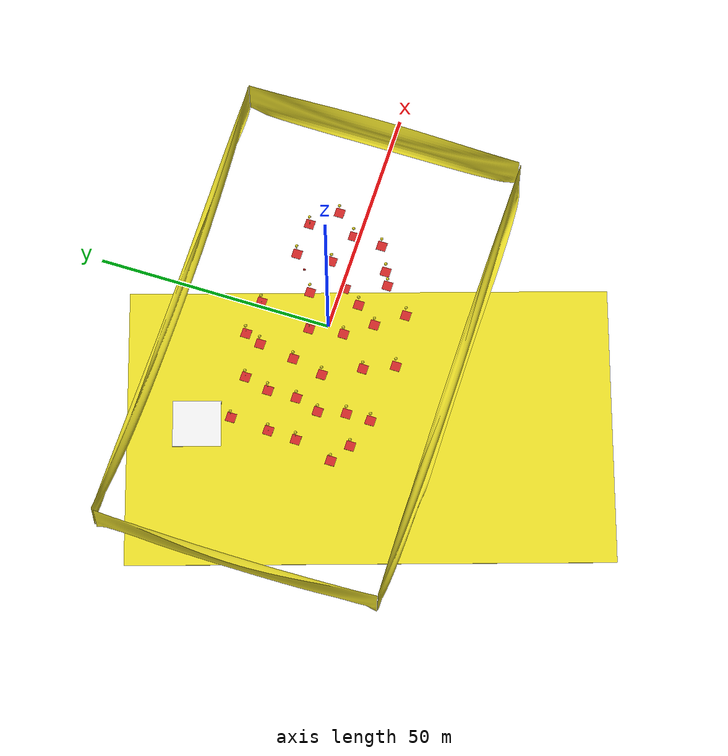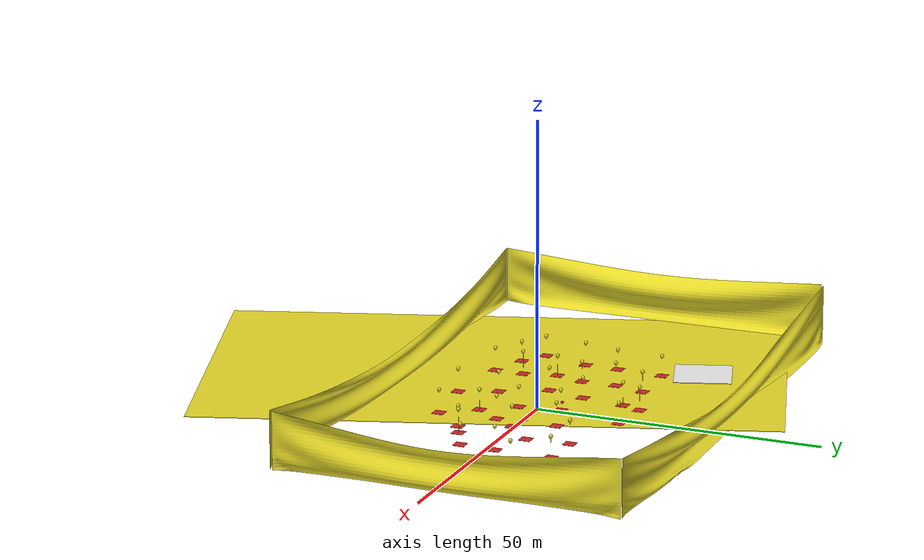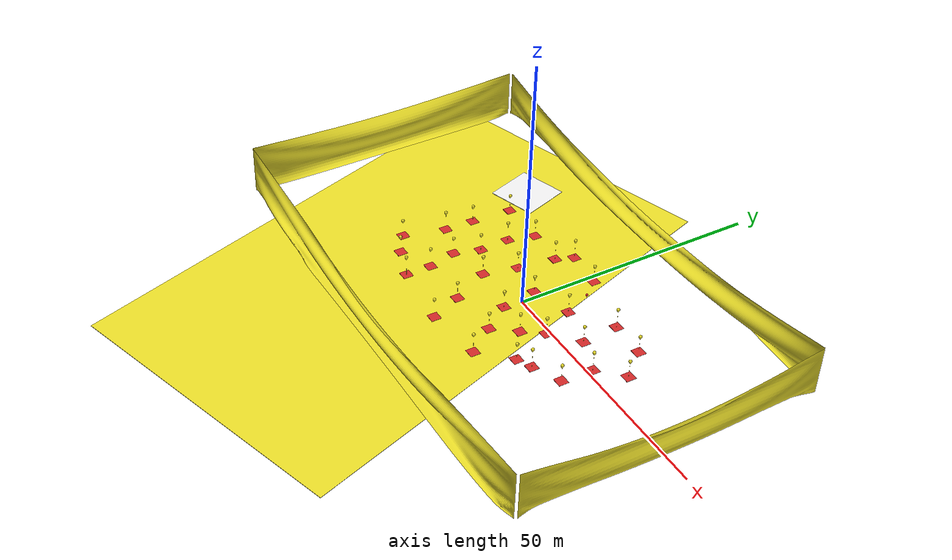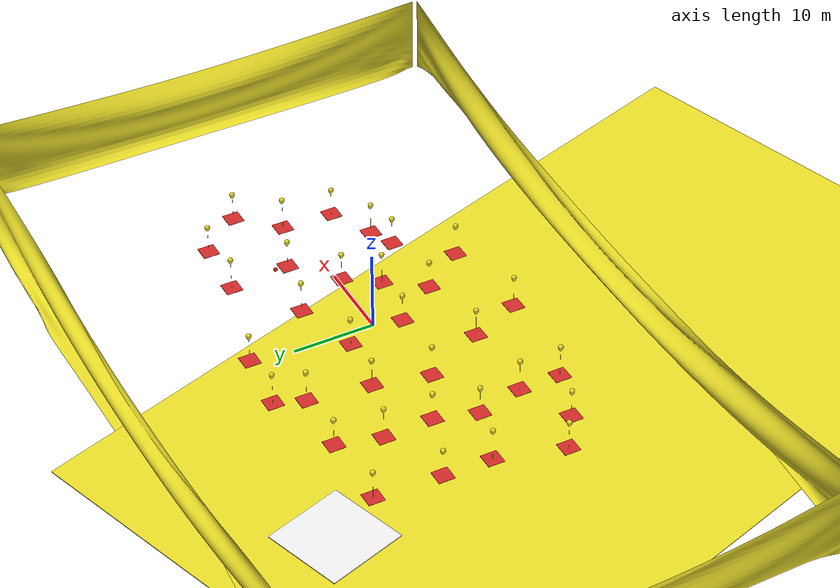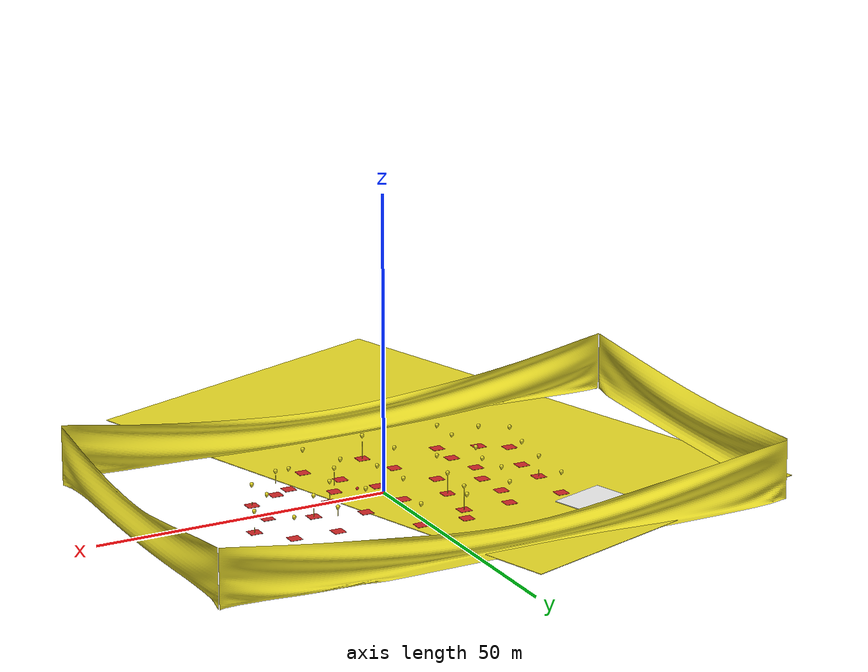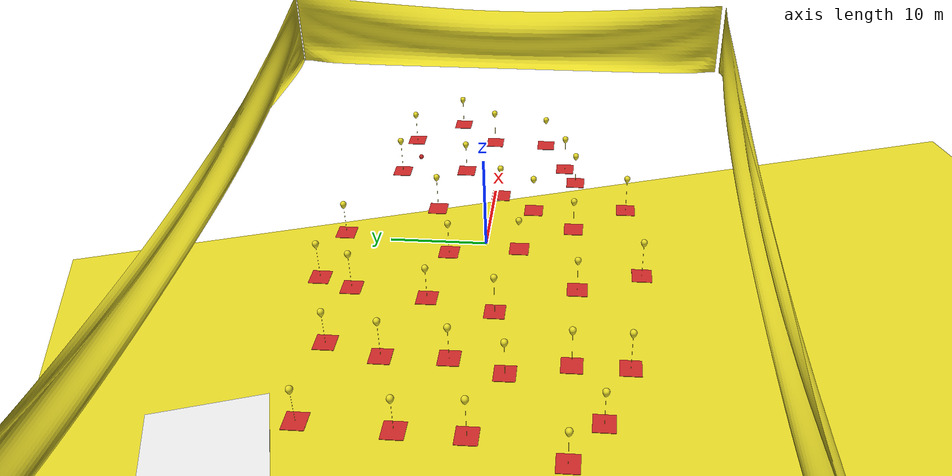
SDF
<sdf version="1.6">
 <world name="default">
  <scene><sky><clouds><speed>12</speed></clouds></sky></scene>
  <light name="sun" type="directional">
   <pose>0 0 10 0 -0 0</pose>
   <diffuse>0.8 0.8 0.8 1</diffuse>
   <specular>0.2 0.2 0.2 1</specular>
   <attenuation>
    <range>1000</range>
    <constant>0.9</constant>
    <linear>0.01</linear>
    <quadratic>0.001</quadratic>
   </attenuation>
   <direction>-0.5 0.1 -0.9</direction>
  </light>
  <gravity>0 0 -9.8</gravity>
  <magnetic_field>6e-06 2.3e-05 -4.2e-05</magnetic_field>
  <atmosphere type="adiabatic"/>
  <physics name="default_physics" default="0" type="ode">
   <max_step_size>0.001</max_step_size>
   <real_time_factor>1</real_time_factor>
   <real_time_update_rate>1000</real_time_update_rate>
  </physics>
  <scene><ambient>0.4 0.4 0.4 1</ambient><background>0.7 0.7 0.7 1</background><shadows>1</shadows></scene>
  <spherical_coordinates>
   <surface_model>EARTH_WGS84</surface_model>
   <latitude_deg>0</latitude_deg>
   <longitude_deg>0</longitude_deg>
   <elevation>0</elevation>
   <heading_deg>0</heading_deg>
  </spherical_coordinates>
  <model name="Balloon4.5m">
   <link name="link_0">
    <pose>0 0 -0.025 0 -0 0</pose>
    <inertial>
     <mass>100</mass>
     <inertia>
      <ixx>0.166667</ixx>
      <ixy>0</ixy>
      <ixz>0</ixz>
      <iyy>0.166667</iyy>
      <iyz>0</iyz>
      <izz>0.166667</izz>
     </inertia>
    </inertial>
    <visual name="visual">
     <geometry><mesh><uri>/home/varun/MBZIRC_Arena/Balloon/Base.dae</uri><scale>1 1 1</scale></mesh></geometry>
     <material>
      <lighting>1</lighting>
      <script><uri>file://media/materials/scripts/gazebo.material</uri><name>Gazebo/Red</name></script>
      <shader type="vertex"><normal_map>__default__</normal_map></shader>
      <ambient>0.3 0.3 0.3 1</ambient>
      <diffuse>1 1 1 1</diffuse>
      <specular>0.1 0.1 0.1 1</specular>
      <emissive>0 0 0 1</emissive>
     </material>
    </visual>
    <collision name="collision">
     <geometry><mesh><uri>/home/varun/MBZIRC_Arena/Balloon/Base.dae</uri><scale>1 1 1</scale></mesh></geometry>
     <surface>
      <friction>
       <ode><mu>1</mu><mu2>1</mu2><fdir1>0 0 0</fdir1><slip1>0</slip1><slip2>0</slip2></ode>
       <torsional>
        <coefficient>1</coefficient>
        <patch_radius>0</patch_radius>
        <surface_radius>0</surface_radius>
        <use_patch_radius>1</use_patch_radius>
        <ode><slip>0</slip></ode>
       </torsional>
      </friction>
      <bounce><restitution_coefficient>0</restitution_coefficient><threshold>1e+06</threshold></bounce>
      <contact>
       <collide_without_contact>0</collide_without_contact>
       <collide_without_contact_bitmask>1</collide_without_contact_bitmask>
       <collide_bitmask>1</collide_bitmask>
       <ode>
        <soft_cfm>0</soft_cfm>
        <soft_erp>0.2</soft_erp>
        <kp>1e+13</kp>
        <kd>1</kd>
        <max_vel>0.01</max_vel>
        <min_depth>0</min_depth>
       </ode>
       <bullet>
        <split_impulse>1</split_impulse>
        <split_impulse_penetration_threshold>-0.01</split_impulse_penetration_threshold>
        <soft_cfm>0</soft_cfm>
        <soft_erp>0.2</soft_erp>
        <kp>1e+13</kp>
        <kd>1</kd>
       </bullet>
      </contact>
     </surface>
    </collision>
   </link>
   <link name="link_1">
    <pose>-0 -0 0.025 0 -0 0</pose>
    <inertial>
     <mass>0.2</mass>
     <inertia>
      <ixx>0.166667</ixx>
      <ixy>0</ixy>
      <ixz>0</ixz>
      <iyy>0.166667</iyy>
      <iyz>0</iyz>
      <izz>0.166667</izz>
     </inertia>
     <pose>0 0 4.5 0 -0 0</pose>
    </inertial>
    <visual name="visual">
     <geometry>
      <mesh><uri>/home/varun/MBZIRC_Arena/Balloon/Balloon4.5m.dae</uri><scale>1 1 1</scale></mesh>
     </geometry>
     <material>
      <lighting>1</lighting>
      <script><uri>file://media/materials/scripts/gazebo.material</uri><name>Gazebo/Yellow</name></script>
      <shader type="pixel"><normal_map>__default__</normal_map></shader>
      <ambient>0.3 0.3 0.3 1</ambient>
      <diffuse>0.7 0.7 0.7 1</diffuse>
      <specular>0.01 0.01 0.01 1</specular>
      <emissive>0 0 0 1</emissive>
     </material>
    </visual>
    <collision name="collision">
     <geometry>
      <mesh><uri>/home/varun/MBZIRC_Arena/Balloon/Balloon4.5m.dae</uri><scale>1 1 1</scale></mesh>
     </geometry>
     <surface>
      <friction>
       <ode><mu>1</mu><mu2>1</mu2><fdir1>0 0 0</fdir1><slip1>0</slip1><slip2>0</slip2></ode>
       <torsional>
        <coefficient>1</coefficient>
        <patch_radius>0</patch_radius>
        <surface_radius>0</surface_radius>
        <use_patch_radius>1</use_patch_radius>
        <ode><slip>0</slip></ode>
       </torsional>
      </friction>
      <bounce><restitution_coefficient>0</restitution_coefficient><threshold>1e+06</threshold></bounce>
      <contact>
       <collide_without_contact>0</collide_without_contact>
       <collide_without_contact_bitmask>1</collide_without_contact_bitmask>
       <collide_bitmask>1</collide_bitmask>
       <ode>
        <soft_cfm>0</soft_cfm>
        <soft_erp>0.2</soft_erp>
        <kp>1e+13</kp>
        <kd>1</kd>
        <max_vel>0.01</max_vel>
        <min_depth>0</min_depth>
       </ode>
       <bullet>
        <split_impulse>1</split_impulse>
        <split_impulse_penetration_threshold>-0.01</split_impulse_penetration_threshold>
        <soft_cfm>0</soft_cfm>
        <soft_erp>0.2</soft_erp>
        <kp>1e+13</kp>
        <kd>1</kd>
       </bullet>
      </contact>
     </surface>
    </collision>
   </link>
   <joint name="ball_joint" type="ball">
    <parent>link_0</parent>
    <child>link_1</child>
    <physics>
     <ode><limit><cfm>0</cfm><erp>0.2</erp></limit><suspension><cfm>0</cfm><erp>0.2</erp></suspension></ode>
    </physics>
   </joint>
   <static>0</static>
   <plugin name="wind_push" filename="libwind_push.so"/>
   <pose>-17.3975 -14.7432 -0.132499 0 -0.000245 0.000348</pose>
  </model>
  <model name="Balloon4.5m_clone">
   <link name="link_0">
    <pose>0 0 -0.025 0 -0 0</pose>
    <inertial>
     <mass>100</mass>
     <inertia>
      <ixx>0.166667</ixx>
      <ixy>0</ixy>
      <ixz>0</ixz>
      <iyy>0.166667</iyy>
      <iyz>0</iyz>
      <izz>0.166667</izz>
     </inertia>
    </inertial>
    <visual name="visual">
     <geometry><mesh><uri>/home/varun/MBZIRC_Arena/Balloon/Base.dae</uri><scale>1 1 1</scale></mesh></geometry>
     <material>
      <lighting>1</lighting>
      <script><uri>file://media/materials/scripts/gazebo.material</uri><name>Gazebo/Red</name></script>
      <shader type="vertex"><normal_map>__default__</normal_map></shader>
      <ambient>0.3 0.3 0.3 1</ambient>
      <diffuse>1 1 1 1</diffuse>
      <specular>0.1 0.1 0.1 1</specular>
      <emissive>0 0 0 1</emissive>
     </material>
    </visual>
    <collision name="collision">
     <geometry><mesh><uri>/home/varun/MBZIRC_Arena/Balloon/Base.dae</uri><scale>1 1 1</scale></mesh></geometry>
     <surface>
      <friction>
       <ode><mu>1</mu><mu2>1</mu2><fdir1>0 0 0</fdir1><slip1>0</slip1><slip2>0</slip2></ode>
       <torsional>
        <coefficient>1</coefficient>
        <patch_radius>0</patch_radius>
        <surface_radius>0</surface_radius>
        <use_patch_radius>1</use_patch_radius>
        <ode><slip>0</slip></ode>
       </torsional>
      </friction>
      <bounce><restitution_coefficient>0</restitution_coefficient><threshold>1e+06</threshold></bounce>
      <contact>
       <collide_without_contact>0</collide_without_contact>
       <collide_without_contact_bitmask>1</collide_without_contact_bitmask>
       <collide_bitmask>1</collide_bitmask>
       <ode>
        <soft_cfm>0</soft_cfm>
        <soft_erp>0.2</soft_erp>
        <kp>1e+13</kp>
        <kd>1</kd>
        <max_vel>0.01</max_vel>
        <min_depth>0</min_depth>
       </ode>
       <bullet>
        <split_impulse>1</split_impulse>
        <split_impulse_penetration_threshold>-0.01</split_impulse_penetration_threshold>
        <soft_cfm>0</soft_cfm>
        <soft_erp>0.2</soft_erp>
        <kp>1e+13</kp>
        <kd>1</kd>
       </bullet>
      </contact>
     </surface>
    </collision>
   </link>
   <link name="link_1">
    <pose>-0 -0 0.025 0 -0 0</pose>
    <inertial>
     <mass>0.2</mass>
     <inertia>
      <ixx>0.166667</ixx>
      <ixy>0</ixy>
      <ixz>0</ixz>
      <iyy>0.166667</iyy>
      <iyz>0</iyz>
      <izz>0.166667</izz>
     </inertia>
     <pose>0 0 4.5 0 -0 0</pose>
    </inertial>
    <visual name="visual">
     <geometry>
      <mesh><uri>/home/varun/MBZIRC_Arena/Balloon/Balloon4.5m.dae</uri><scale>1 1 1</scale></mesh>
     </geometry>
     <material>
      <lighting>1</lighting>
      <script><uri>file://media/materials/scripts/gazebo.material</uri><name>Gazebo/Yellow</name></script>
      <shader type="pixel"><normal_map>__default__</normal_map></shader>
      <ambient>0.3 0.3 0.3 1</ambient>
      <diffuse>0.7 0.7 0.7 1</diffuse>
      <specular>0.01 0.01 0.01 1</specular>
      <emissive>0 0 0 1</emissive>
     </material>
    </visual>
    <collision name="collision">
     <geometry>
      <mesh><uri>/home/varun/MBZIRC_Arena/Balloon/Balloon4.5m.dae</uri><scale>1 1 1</scale></mesh>
     </geometry>
     <surface>
      <friction>
       <ode><mu>1</mu><mu2>1</mu2><fdir1>0 0 0</fdir1><slip1>0</slip1><slip2>0</slip2></ode>
       <torsional>
        <coefficient>1</coefficient>
        <patch_radius>0</patch_radius>
        <surface_radius>0</surface_radius>
        <use_patch_radius>1</use_patch_radius>
        <ode><slip>0</slip></ode>
       </torsional>
      </friction>
      <bounce><restitution_coefficient>0</restitution_coefficient><threshold>1e+06</threshold></bounce>
      <contact>
       <collide_without_contact>0</collide_without_contact>
       <collide_without_contact_bitmask>1</collide_without_contact_bitmask>
       <collide_bitmask>1</collide_bitmask>
       <ode>
        <soft_cfm>0</soft_cfm>
        <soft_erp>0.2</soft_erp>
        <kp>1e+13</kp>
        <kd>1</kd>
        <max_vel>0.01</max_vel>
        <min_depth>0</min_depth>
       </ode>
       <bullet>
        <split_impulse>1</split_impulse>
        <split_impulse_penetration_threshold>-0.01</split_impulse_penetration_threshold>
        <soft_cfm>0</soft_cfm>
        <soft_erp>0.2</soft_erp>
        <kp>1e+13</kp>
        <kd>1</kd>
       </bullet>
      </contact>
     </surface>
    </collision>
   </link>
   <joint name="ball_joint" type="ball">
    <parent>link_0</parent>
    <child>link_1</child>
    <physics>
     <ode><limit><cfm>0</cfm><erp>0.2</erp></limit><suspension><cfm>0</cfm><erp>0.2</erp></suspension></ode>
    </physics>
   </joint>
   <static>0</static>
   <plugin name="wind_push" filename="libwind_push.so"/>
   <pose>-17.397 -9.54962 -0.132553 -0.000299 -0 1e-06</pose>
  </model>
  <model name="Balloon4.5m_clone_0">
   <link name="link_0">
    <pose>0 0 -0.025 0 -0 0</pose>
    <inertial>
     <mass>100</mass>
     <inertia>
      <ixx>0.166667</ixx>
      <ixy>0</ixy>
      <ixz>0</ixz>
      <iyy>0.166667</iyy>
      <iyz>0</iyz>
      <izz>0.166667</izz>
     </inertia>
    </inertial>
    <visual name="visual">
     <geometry><mesh><uri>/home/varun/MBZIRC_Arena/Balloon/Base.dae</uri><scale>1 1 1</scale></mesh></geometry>
     <material>
      <lighting>1</lighting>
      <script><uri>file://media/materials/scripts/gazebo.material</uri><name>Gazebo/Red</name></script>
      <shader type="vertex"><normal_map>__default__</normal_map></shader>
      <ambient>0.3 0.3 0.3 1</ambient>
      <diffuse>1 1 1 1</diffuse>
      <specular>0.1 0.1 0.1 1</specular>
      <emissive>0 0 0 1</emissive>
     </material>
    </visual>
    <collision name="collision">
     <geometry><mesh><uri>/home/varun/MBZIRC_Arena/Balloon/Base.dae</uri><scale>1 1 1</scale></mesh></geometry>
     <surface>
      <friction>
       <ode><mu>1</mu><mu2>1</mu2><fdir1>0 0 0</fdir1><slip1>0</slip1><slip2>0</slip2></ode>
       <torsional>
        <coefficient>1</coefficient>
        <patch_radius>0</patch_radius>
        <surface_radius>0</surface_radius>
        <use_patch_radius>1</use_patch_radius>
        <ode><slip>0</slip></ode>
       </torsional>
      </friction>
      <bounce><restitution_coefficient>0</restitution_coefficient><threshold>1e+06</threshold></bounce>
      <contact>
       <collide_without_contact>0</collide_without_contact>
       <collide_without_contact_bitmask>1</collide_without_contact_bitmask>
       <collide_bitmask>1</collide_bitmask>
       <ode>
        <soft_cfm>0</soft_cfm>
        <soft_erp>0.2</soft_erp>
        <kp>1e+13</kp>
        <kd>1</kd>
        <max_vel>0.01</max_vel>
        <min_depth>0</min_depth>
       </ode>
       <bullet>
        <split_impulse>1</split_impulse>
        <split_impulse_penetration_threshold>-0.01</split_impulse_penetration_threshold>
        <soft_cfm>0</soft_cfm>
        <soft_erp>0.2</soft_erp>
        <kp>1e+13</kp>
        <kd>1</kd>
       </bullet>
      </contact>
     </surface>
    </collision>
   </link>
   <link name="link_1">
    <pose>-0 -0 0.025 0 -0 0</pose>
    <inertial>
     <mass>0.2</mass>
     <inertia>
      <ixx>0.166667</ixx>
      <ixy>0</ixy>
      <ixz>0</ixz>
      <iyy>0.166667</iyy>
      <iyz>0</iyz>
      <izz>0.166667</izz>
     </inertia>
     <pose>0 0 4.5 0 -0 0</pose>
    </inertial>
    <visual name="visual">
     <geometry>
      <mesh><uri>/home/varun/MBZIRC_Arena/Balloon/Balloon4.5m.dae</uri><scale>1 1 1</scale></mesh>
     </geometry>
     <material>
      <lighting>1</lighting>
      <script><uri>file://media/materials/scripts/gazebo.material</uri><name>Gazebo/Yellow</name></script>
      <shader type="pixel"><normal_map>__default__</normal_map></shader>
      <ambient>0.3 0.3 0.3 1</ambient>
      <diffuse>0.7 0.7 0.7 1</diffuse>
      <specular>0.01 0.01 0.01 1</specular>
      <emissive>0 0 0 1</emissive>
     </material>
    </visual>
    <collision name="collision">
     <geometry>
      <mesh><uri>/home/varun/MBZIRC_Arena/Balloon/Balloon4.5m.dae</uri><scale>1 1 1</scale></mesh>
     </geometry>
     <surface>
      <friction>
       <ode><mu>1</mu><mu2>1</mu2><fdir1>0 0 0</fdir1><slip1>0</slip1><slip2>0</slip2></ode>
       <torsional>
        <coefficient>1</coefficient>
        <patch_radius>0</patch_radius>
        <surface_radius>0</surface_radius>
        <use_patch_radius>1</use_patch_radius>
        <ode><slip>0</slip></ode>
       </torsional>
      </friction>
      <bounce><restitution_coefficient>0</restitution_coefficient><threshold>1e+06</threshold></bounce>
      <contact>
       <collide_without_contact>0</collide_without_contact>
       <collide_without_contact_bitmask>1</collide_without_contact_bitmask>
       <collide_bitmask>1</collide_bitmask>
       <ode>
        <soft_cfm>0</soft_cfm>
        <soft_erp>0.2</soft_erp>
        <kp>1e+13</kp>
        <kd>1</kd>
        <max_vel>0.01</max_vel>
        <min_depth>0</min_depth>
       </ode>
       <bullet>
        <split_impulse>1</split_impulse>
        <split_impulse_penetration_threshold>-0.01</split_impulse_penetration_threshold>
        <soft_cfm>0</soft_cfm>
        <soft_erp>0.2</soft_erp>
        <kp>1e+13</kp>
        <kd>1</kd>
       </bullet>
      </contact>
     </surface>
    </collision>
   </link>
   <joint name="ball_joint" type="ball">
    <parent>link_0</parent>
    <child>link_1</child>
    <physics>
     <ode><limit><cfm>0</cfm><erp>0.2</erp></limit><suspension><cfm>0</cfm><erp>0.2</erp></suspension></ode>
    </physics>
   </joint>
   <static>0</static>
   <plugin name="wind_push" filename="libwind_push.so"/>
   <pose>-10.6597 -2.02133 -0.132512 -0.001234 0.000724 -0.000836</pose>
  </model>
  <model name="Balloon4.5m_clone_1">
   <link name="link_0">
    <pose>0 0 -0.025 0 -0 0</pose>
    <inertial>
     <mass>100</mass>
     <inertia>
      <ixx>0.166667</ixx>
      <ixy>0</ixy>
      <ixz>0</ixz>
      <iyy>0.166667</iyy>
      <iyz>0</iyz>
      <izz>0.166667</izz>
     </inertia>
    </inertial>
    <visual name="visual">
     <geometry><mesh><uri>/home/varun/MBZIRC_Arena/Balloon/Base.dae</uri><scale>1 1 1</scale></mesh></geometry>
     <material>
      <lighting>1</lighting>
      <script><uri>file://media/materials/scripts/gazebo.material</uri><name>Gazebo/Red</name></script>
      <shader type="vertex"><normal_map>__default__</normal_map></shader>
      <ambient>0.3 0.3 0.3 1</ambient>
      <diffuse>1 1 1 1</diffuse>
      <specular>0.1 0.1 0.1 1</specular>
      <emissive>0 0 0 1</emissive>
     </material>
    </visual>
    <collision name="collision">
     <geometry><mesh><uri>/home/varun/MBZIRC_Arena/Balloon/Base.dae</uri><scale>1 1 1</scale></mesh></geometry>
     <surface>
      <friction>
       <ode><mu>1</mu><mu2>1</mu2><fdir1>0 0 0</fdir1><slip1>0</slip1><slip2>0</slip2></ode>
       <torsional>
        <coefficient>1</coefficient>
        <patch_radius>0</patch_radius>
        <surface_radius>0</surface_radius>
        <use_patch_radius>1</use_patch_radius>
        <ode><slip>0</slip></ode>
       </torsional>
      </friction>
      <bounce><restitution_coefficient>0</restitution_coefficient><threshold>1e+06</threshold></bounce>
      <contact>
       <collide_without_contact>0</collide_without_contact>
       <collide_without_contact_bitmask>1</collide_without_contact_bitmask>
       <collide_bitmask>1</collide_bitmask>
       <ode>
        <soft_cfm>0</soft_cfm>
        <soft_erp>0.2</soft_erp>
        <kp>1e+13</kp>
        <kd>1</kd>
        <max_vel>0.01</max_vel>
        <min_depth>0</min_depth>
       </ode>
       <bullet>
        <split_impulse>1</split_impulse>
        <split_impulse_penetration_threshold>-0.01</split_impulse_penetration_threshold>
        <soft_cfm>0</soft_cfm>
        <soft_erp>0.2</soft_erp>
        <kp>1e+13</kp>
        <kd>1</kd>
       </bullet>
      </contact>
     </surface>
    </collision>
   </link>
   <link name="link_1">
    <pose>-0 -0 0.025 0 -0 0</pose>
    <inertial>
     <mass>0.2</mass>
     <inertia>
      <ixx>0.166667</ixx>
      <ixy>0</ixy>
      <ixz>0</ixz>
      <iyy>0.166667</iyy>
      <iyz>0</iyz>
      <izz>0.166667</izz>
     </inertia>
     <pose>0 0 4.5 0 -0 0</pose>
    </inertial>
    <visual name="visual">
     <geometry>
      <mesh><uri>/home/varun/MBZIRC_Arena/Balloon/Balloon4.5m.dae</uri><scale>1 1 1</scale></mesh>
     </geometry>
     <material>
      <lighting>1</lighting>
      <script><uri>file://media/materials/scripts/gazebo.material</uri><name>Gazebo/Yellow</name></script>
      <shader type="pixel"><normal_map>__default__</normal_map></shader>
      <ambient>0.3 0.3 0.3 1</ambient>
      <diffuse>0.7 0.7 0.7 1</diffuse>
      <specular>0.01 0.01 0.01 1</specular>
      <emissive>0 0 0 1</emissive>
     </material>
    </visual>
    <collision name="collision">
     <geometry>
      <mesh><uri>/home/varun/MBZIRC_Arena/Balloon/Balloon4.5m.dae</uri><scale>1 1 1</scale></mesh>
     </geometry>
     <surface>
      <friction>
       <ode><mu>1</mu><mu2>1</mu2><fdir1>0 0 0</fdir1><slip1>0</slip1><slip2>0</slip2></ode>
       <torsional>
        <coefficient>1</coefficient>
        <patch_radius>0</patch_radius>
        <surface_radius>0</surface_radius>
        <use_patch_radius>1</use_patch_radius>
        <ode><slip>0</slip></ode>
       </torsional>
      </friction>
      <bounce><restitution_coefficient>0</restitution_coefficient><threshold>1e+06</threshold></bounce>
      <contact>
       <collide_without_contact>0</collide_without_contact>
       <collide_without_contact_bitmask>1</collide_without_contact_bitmask>
       <collide_bitmask>1</collide_bitmask>
       <ode>
        <soft_cfm>0</soft_cfm>
        <soft_erp>0.2</soft_erp>
        <kp>1e+13</kp>
        <kd>1</kd>
        <max_vel>0.01</max_vel>
        <min_depth>0</min_depth>
       </ode>
       <bullet>
        <split_impulse>1</split_impulse>
        <split_impulse_penetration_threshold>-0.01</split_impulse_penetration_threshold>
        <soft_cfm>0</soft_cfm>
        <soft_erp>0.2</soft_erp>
        <kp>1e+13</kp>
        <kd>1</kd>
       </bullet>
      </contact>
     </surface>
    </collision>
   </link>
   <joint name="ball_joint" type="ball">
    <parent>link_0</parent>
    <child>link_1</child>
    <physics>
     <ode><limit><cfm>0</cfm><erp>0.2</erp></limit><suspension><cfm>0</cfm><erp>0.2</erp></suspension></ode>
    </physics>
   </joint>
   <static>0</static>
   <plugin name="wind_push" filename="libwind_push.so"/>
   <pose>-17.3798 7.50598 -0.132557 -0.000303 -0 0.000103</pose>
  </model>
  <model name="Balloon4.5m_clone_2">
   <link name="link_0">
    <pose>0 0 -0.025 0 -0 0</pose>
    <inertial>
     <mass>100</mass>
     <inertia>
      <ixx>0.166667</ixx>
      <ixy>0</ixy>
      <ixz>0</ixz>
      <iyy>0.166667</iyy>
      <iyz>0</iyz>
      <izz>0.166667</izz>
     </inertia>
    </inertial>
    <visual name="visual">
     <geometry><mesh><uri>/home/varun/MBZIRC_Arena/Balloon/Base.dae</uri><scale>1 1 1</scale></mesh></geometry>
     <material>
      <lighting>1</lighting>
      <script><uri>file://media/materials/scripts/gazebo.material</uri><name>Gazebo/Red</name></script>
      <shader type="vertex"><normal_map>__default__</normal_map></shader>
      <ambient>0.3 0.3 0.3 1</ambient>
      <diffuse>1 1 1 1</diffuse>
      <specular>0.1 0.1 0.1 1</specular>
      <emissive>0 0 0 1</emissive>
     </material>
    </visual>
    <collision name="collision">
     <geometry><mesh><uri>/home/varun/MBZIRC_Arena/Balloon/Base.dae</uri><scale>1 1 1</scale></mesh></geometry>
     <surface>
      <friction>
       <ode><mu>1</mu><mu2>1</mu2><fdir1>0 0 0</fdir1><slip1>0</slip1><slip2>0</slip2></ode>
       <torsional>
        <coefficient>1</coefficient>
        <patch_radius>0</patch_radius>
        <surface_radius>0</surface_radius>
        <use_patch_radius>1</use_patch_radius>
        <ode><slip>0</slip></ode>
       </torsional>
      </friction>
      <bounce><restitution_coefficient>0</restitution_coefficient><threshold>1e+06</threshold></bounce>
      <contact>
       <collide_without_contact>0</collide_without_contact>
       <collide_without_contact_bitmask>1</collide_without_contact_bitmask>
       <collide_bitmask>1</collide_bitmask>
       <ode>
        <soft_cfm>0</soft_cfm>
        <soft_erp>0.2</soft_erp>
        <kp>1e+13</kp>
        <kd>1</kd>
        <max_vel>0.01</max_vel>
        <min_depth>0</min_depth>
       </ode>
       <bullet>
        <split_impulse>1</split_impulse>
        <split_impulse_penetration_threshold>-0.01</split_impulse_penetration_threshold>
        <soft_cfm>0</soft_cfm>
        <soft_erp>0.2</soft_erp>
        <kp>1e+13</kp>
        <kd>1</kd>
       </bullet>
      </contact>
     </surface>
    </collision>
   </link>
   <link name="link_1">
    <pose>-0 -0 0.025 0 -0 0</pose>
    <inertial>
     <mass>0.2</mass>
     <inertia>
      <ixx>0.166667</ixx>
      <ixy>0</ixy>
      <ixz>0</ixz>
      <iyy>0.166667</iyy>
      <iyz>0</iyz>
      <izz>0.166667</izz>
     </inertia>
     <pose>0 0 4.5 0 -0 0</pose>
    </inertial>
    <visual name="visual">
     <geometry>
      <mesh><uri>/home/varun/MBZIRC_Arena/Balloon/Balloon4.5m.dae</uri><scale>1 1 1</scale></mesh>
     </geometry>
     <material>
      <lighting>1</lighting>
      <script><uri>file://media/materials/scripts/gazebo.material</uri><name>Gazebo/Yellow</name></script>
      <shader type="pixel"><normal_map>__default__</normal_map></shader>
      <ambient>0.3 0.3 0.3 1</ambient>
      <diffuse>0.7 0.7 0.7 1</diffuse>
      <specular>0.01 0.01 0.01 1</specular>
      <emissive>0 0 0 1</emissive>
     </material>
    </visual>
    <collision name="collision">
     <geometry>
      <mesh><uri>/home/varun/MBZIRC_Arena/Balloon/Balloon4.5m.dae</uri><scale>1 1 1</scale></mesh>
     </geometry>
     <surface>
      <friction>
       <ode><mu>1</mu><mu2>1</mu2><fdir1>0 0 0</fdir1><slip1>0</slip1><slip2>0</slip2></ode>
       <torsional>
        <coefficient>1</coefficient>
        <patch_radius>0</patch_radius>
        <surface_radius>0</surface_radius>
        <use_patch_radius>1</use_patch_radius>
        <ode><slip>0</slip></ode>
       </torsional>
      </friction>
      <bounce><restitution_coefficient>0</restitution_coefficient><threshold>1e+06</threshold></bounce>
      <contact>
       <collide_without_contact>0</collide_without_contact>
       <collide_without_contact_bitmask>1</collide_without_contact_bitmask>
       <collide_bitmask>1</collide_bitmask>
       <ode>
        <soft_cfm>0</soft_cfm>
        <soft_erp>0.2</soft_erp>
        <kp>1e+13</kp>
        <kd>1</kd>
        <max_vel>0.01</max_vel>
        <min_depth>0</min_depth>
       </ode>
       <bullet>
        <split_impulse>1</split_impulse>
        <split_impulse_penetration_threshold>-0.01</split_impulse_penetration_threshold>
        <soft_cfm>0</soft_cfm>
        <soft_erp>0.2</soft_erp>
        <kp>1e+13</kp>
        <kd>1</kd>
       </bullet>
      </contact>
     </surface>
    </collision>
   </link>
   <joint name="ball_joint" type="ball">
    <parent>link_0</parent>
    <child>link_1</child>
    <physics>
     <ode><limit><cfm>0</cfm><erp>0.2</erp></limit><suspension><cfm>0</cfm><erp>0.2</erp></suspension></ode>
    </physics>
   </joint>
   <static>0</static>
   <plugin name="wind_push" filename="libwind_push.so"/>
   <pose>-7.95853 12.357 -0.132713 0 -0.000459 0.00035</pose>
  </model>
  <model name="Balloon4.5m_clone_3">
   <link name="link_0">
    <pose>0 0 -0.025 0 -0 0</pose>
    <inertial>
     <mass>100</mass>
     <inertia>
      <ixx>0.166667</ixx>
      <ixy>0</ixy>
      <ixz>0</ixz>
      <iyy>0.166667</iyy>
      <iyz>0</iyz>
      <izz>0.166667</izz>
     </inertia>
    </inertial>
    <visual name="visual">
     <geometry><mesh><uri>/home/varun/MBZIRC_Arena/Balloon/Base.dae</uri><scale>1 1 1</scale></mesh></geometry>
     <material>
      <lighting>1</lighting>
      <script><uri>file://media/materials/scripts/gazebo.material</uri><name>Gazebo/Red</name></script>
      <shader type="vertex"><normal_map>__default__</normal_map></shader>
      <ambient>0.3 0.3 0.3 1</ambient>
      <diffuse>1 1 1 1</diffuse>
      <specular>0.1 0.1 0.1 1</specular>
      <emissive>0 0 0 1</emissive>
     </material>
    </visual>
    <collision name="collision">
     <geometry><mesh><uri>/home/varun/MBZIRC_Arena/Balloon/Base.dae</uri><scale>1 1 1</scale></mesh></geometry>
     <surface>
      <friction>
       <ode><mu>1</mu><mu2>1</mu2><fdir1>0 0 0</fdir1><slip1>0</slip1><slip2>0</slip2></ode>
       <torsional>
        <coefficient>1</coefficient>
        <patch_radius>0</patch_radius>
        <surface_radius>0</surface_radius>
        <use_patch_radius>1</use_patch_radius>
        <ode><slip>0</slip></ode>
       </torsional>
      </friction>
      <bounce><restitution_coefficient>0</restitution_coefficient><threshold>1e+06</threshold></bounce>
      <contact>
       <collide_without_contact>0</collide_without_contact>
       <collide_without_contact_bitmask>1</collide_without_contact_bitmask>
       <collide_bitmask>1</collide_bitmask>
       <ode>
        <soft_cfm>0</soft_cfm>
        <soft_erp>0.2</soft_erp>
        <kp>1e+13</kp>
        <kd>1</kd>
        <max_vel>0.01</max_vel>
        <min_depth>0</min_depth>
       </ode>
       <bullet>
        <split_impulse>1</split_impulse>
        <split_impulse_penetration_threshold>-0.01</split_impulse_penetration_threshold>
        <soft_cfm>0</soft_cfm>
        <soft_erp>0.2</soft_erp>
        <kp>1e+13</kp>
        <kd>1</kd>
       </bullet>
      </contact>
     </surface>
    </collision>
   </link>
   <link name="link_1">
    <pose>-0 -0 0.025 0 -0 0</pose>
    <inertial>
     <mass>0.2</mass>
     <inertia>
      <ixx>0.166667</ixx>
      <ixy>0</ixy>
      <ixz>0</ixz>
      <iyy>0.166667</iyy>
      <iyz>0</iyz>
      <izz>0.166667</izz>
     </inertia>
     <pose>0 0 4.5 0 -0 0</pose>
    </inertial>
    <visual name="visual">
     <geometry>
      <mesh><uri>/home/varun/MBZIRC_Arena/Balloon/Balloon4.5m.dae</uri><scale>1 1 1</scale></mesh>
     </geometry>
     <material>
      <lighting>1</lighting>
      <script><uri>file://media/materials/scripts/gazebo.material</uri><name>Gazebo/Yellow</name></script>
      <shader type="pixel"><normal_map>__default__</normal_map></shader>
      <ambient>0.3 0.3 0.3 1</ambient>
      <diffuse>0.7 0.7 0.7 1</diffuse>
      <specular>0.01 0.01 0.01 1</specular>
      <emissive>0 0 0 1</emissive>
     </material>
    </visual>
    <collision name="collision">
     <geometry>
      <mesh><uri>/home/varun/MBZIRC_Arena/Balloon/Balloon4.5m.dae</uri><scale>1 1 1</scale></mesh>
     </geometry>
     <surface>
      <friction>
       <ode><mu>1</mu><mu2>1</mu2><fdir1>0 0 0</fdir1><slip1>0</slip1><slip2>0</slip2></ode>
       <torsional>
        <coefficient>1</coefficient>
        <patch_radius>0</patch_radius>
        <surface_radius>0</surface_radius>
        <use_patch_radius>1</use_patch_radius>
        <ode><slip>0</slip></ode>
       </torsional>
      </friction>
      <bounce><restitution_coefficient>0</restitution_coefficient><threshold>1e+06</threshold></bounce>
      <contact>
       <collide_without_contact>0</collide_without_contact>
       <collide_without_contact_bitmask>1</collide_without_contact_bitmask>
       <collide_bitmask>1</collide_bitmask>
       <ode>
        <soft_cfm>0</soft_cfm>
        <soft_erp>0.2</soft_erp>
        <kp>1e+13</kp>
        <kd>1</kd>
        <max_vel>0.01</max_vel>
        <min_depth>0</min_depth>
       </ode>
       <bullet>
        <split_impulse>1</split_impulse>
        <split_impulse_penetration_threshold>-0.01</split_impulse_penetration_threshold>
        <soft_cfm>0</soft_cfm>
        <soft_erp>0.2</soft_erp>
        <kp>1e+13</kp>
        <kd>1</kd>
       </bullet>
      </contact>
     </surface>
    </collision>
   </link>
   <joint name="ball_joint" type="ball">
    <parent>link_0</parent>
    <child>link_1</child>
    <physics>
     <ode><limit><cfm>0</cfm><erp>0.2</erp></limit><suspension><cfm>0</cfm><erp>0.2</erp></suspension></ode>
    </physics>
   </joint>
   <static>0</static>
   <plugin name="wind_push" filename="libwind_push.so"/>
   <pose>6.65395 -4.54582 -0.132456 -0.000202 -0 0.00034</pose>
  </model>
  <model name="Balloon4.5m_clone_4">
   <link name="link_0">
    <pose>0 0 -0.025 0 -0 0</pose>
    <inertial>
     <mass>100</mass>
     <inertia>
      <ixx>0.166667</ixx>
      <ixy>0</ixy>
      <ixz>0</ixz>
      <iyy>0.166667</iyy>
      <iyz>0</iyz>
      <izz>0.166667</izz>
     </inertia>
    </inertial>
    <visual name="visual">
     <geometry><mesh><uri>/home/varun/MBZIRC_Arena/Balloon/Base.dae</uri><scale>1 1 1</scale></mesh></geometry>
     <material>
      <lighting>1</lighting>
      <script><uri>file://media/materials/scripts/gazebo.material</uri><name>Gazebo/Red</name></script>
      <shader type="vertex"><normal_map>__default__</normal_map></shader>
      <ambient>0.3 0.3 0.3 1</ambient>
      <diffuse>1 1 1 1</diffuse>
      <specular>0.1 0.1 0.1 1</specular>
      <emissive>0 0 0 1</emissive>
     </material>
    </visual>
    <collision name="collision">
     <geometry><mesh><uri>/home/varun/MBZIRC_Arena/Balloon/Base.dae</uri><scale>1 1 1</scale></mesh></geometry>
     <surface>
      <friction>
       <ode><mu>1</mu><mu2>1</mu2><fdir1>0 0 0</fdir1><slip1>0</slip1><slip2>0</slip2></ode>
       <torsional>
        <coefficient>1</coefficient>
        <patch_radius>0</patch_radius>
        <surface_radius>0</surface_radius>
        <use_patch_radius>1</use_patch_radius>
        <ode><slip>0</slip></ode>
       </torsional>
      </friction>
      <bounce><restitution_coefficient>0</restitution_coefficient><threshold>1e+06</threshold></bounce>
      <contact>
       <collide_without_contact>0</collide_without_contact>
       <collide_without_contact_bitmask>1</collide_without_contact_bitmask>
       <collide_bitmask>1</collide_bitmask>
       <ode>
        <soft_cfm>0</soft_cfm>
        <soft_erp>0.2</soft_erp>
        <kp>1e+13</kp>
        <kd>1</kd>
        <max_vel>0.01</max_vel>
        <min_depth>0</min_depth>
       </ode>
       <bullet>
        <split_impulse>1</split_impulse>
        <split_impulse_penetration_threshold>-0.01</split_impulse_penetration_threshold>
        <soft_cfm>0</soft_cfm>
        <soft_erp>0.2</soft_erp>
        <kp>1e+13</kp>
        <kd>1</kd>
       </bullet>
      </contact>
     </surface>
    </collision>
   </link>
   <link name="link_1">
    <pose>-0 -0 0.025 0 -0 0</pose>
    <inertial>
     <mass>0.2</mass>
     <inertia>
      <ixx>0.166667</ixx>
      <ixy>0</ixy>
      <ixz>0</ixz>
      <iyy>0.166667</iyy>
      <iyz>0</iyz>
      <izz>0.166667</izz>
     </inertia>
     <pose>0 0 4.5 0 -0 0</pose>
    </inertial>
    <visual name="visual">
     <geometry>
      <mesh><uri>/home/varun/MBZIRC_Arena/Balloon/Balloon4.5m.dae</uri><scale>1 1 1</scale></mesh>
     </geometry>
     <material>
      <lighting>1</lighting>
      <script><uri>file://media/materials/scripts/gazebo.material</uri><name>Gazebo/Yellow</name></script>
      <shader type="pixel"><normal_map>__default__</normal_map></shader>
      <ambient>0.3 0.3 0.3 1</ambient>
      <diffuse>0.7 0.7 0.7 1</diffuse>
      <specular>0.01 0.01 0.01 1</specular>
      <emissive>0 0 0 1</emissive>
     </material>
    </visual>
    <collision name="collision">
     <geometry>
      <mesh><uri>/home/varun/MBZIRC_Arena/Balloon/Balloon4.5m.dae</uri><scale>1 1 1</scale></mesh>
     </geometry>
     <surface>
      <friction>
       <ode><mu>1</mu><mu2>1</mu2><fdir1>0 0 0</fdir1><slip1>0</slip1><slip2>0</slip2></ode>
       <torsional>
        <coefficient>1</coefficient>
        <patch_radius>0</patch_radius>
        <surface_radius>0</surface_radius>
        <use_patch_radius>1</use_patch_radius>
        <ode><slip>0</slip></ode>
       </torsional>
      </friction>
      <bounce><restitution_coefficient>0</restitution_coefficient><threshold>1e+06</threshold></bounce>
      <contact>
       <collide_without_contact>0</collide_without_contact>
       <collide_without_contact_bitmask>1</collide_without_contact_bitmask>
       <collide_bitmask>1</collide_bitmask>
       <ode>
        <soft_cfm>0</soft_cfm>
        <soft_erp>0.2</soft_erp>
        <kp>1e+13</kp>
        <kd>1</kd>
        <max_vel>0.01</max_vel>
        <min_depth>0</min_depth>
       </ode>
       <bullet>
        <split_impulse>1</split_impulse>
        <split_impulse_penetration_threshold>-0.01</split_impulse_penetration_threshold>
        <soft_cfm>0</soft_cfm>
        <soft_erp>0.2</soft_erp>
        <kp>1e+13</kp>
        <kd>1</kd>
       </bullet>
      </contact>
     </surface>
    </collision>
   </link>
   <joint name="ball_joint" type="ball">
    <parent>link_0</parent>
    <child>link_1</child>
    <physics>
     <ode><limit><cfm>0</cfm><erp>0.2</erp></limit><suspension><cfm>0</cfm><erp>0.2</erp></suspension></ode>
    </physics>
   </joint>
   <static>0</static>
   <plugin name="wind_push" filename="libwind_push.so"/>
   <pose>7.34692 -14.6625 -0.132462 -0 0.000208 0.000306</pose>
  </model>
  <model name="Balloon4.5m_clone_5">
   <link name="link_0">
    <pose>0 0 -0.025 0 -0 0</pose>
    <inertial>
     <mass>100</mass>
     <inertia>
      <ixx>0.166667</ixx>
      <ixy>0</ixy>
      <ixz>0</ixz>
      <iyy>0.166667</iyy>
      <iyz>0</iyz>
      <izz>0.166667</izz>
     </inertia>
    </inertial>
    <visual name="visual">
     <geometry><mesh><uri>/home/varun/MBZIRC_Arena/Balloon/Base.dae</uri><scale>1 1 1</scale></mesh></geometry>
     <material>
      <lighting>1</lighting>
      <script><uri>file://media/materials/scripts/gazebo.material</uri><name>Gazebo/Red</name></script>
      <shader type="vertex"><normal_map>__default__</normal_map></shader>
      <ambient>0.3 0.3 0.3 1</ambient>
      <diffuse>1 1 1 1</diffuse>
      <specular>0.1 0.1 0.1 1</specular>
      <emissive>0 0 0 1</emissive>
     </material>
    </visual>
    <collision name="collision">
     <geometry><mesh><uri>/home/varun/MBZIRC_Arena/Balloon/Base.dae</uri><scale>1 1 1</scale></mesh></geometry>
     <surface>
      <friction>
       <ode><mu>1</mu><mu2>1</mu2><fdir1>0 0 0</fdir1><slip1>0</slip1><slip2>0</slip2></ode>
       <torsional>
        <coefficient>1</coefficient>
        <patch_radius>0</patch_radius>
        <surface_radius>0</surface_radius>
        <use_patch_radius>1</use_patch_radius>
        <ode><slip>0</slip></ode>
       </torsional>
      </friction>
      <bounce><restitution_coefficient>0</restitution_coefficient><threshold>1e+06</threshold></bounce>
      <contact>
       <collide_without_contact>0</collide_without_contact>
       <collide_without_contact_bitmask>1</collide_without_contact_bitmask>
       <collide_bitmask>1</collide_bitmask>
       <ode>
        <soft_cfm>0</soft_cfm>
        <soft_erp>0.2</soft_erp>
        <kp>1e+13</kp>
        <kd>1</kd>
        <max_vel>0.01</max_vel>
        <min_depth>0</min_depth>
       </ode>
       <bullet>
        <split_impulse>1</split_impulse>
        <split_impulse_penetration_threshold>-0.01</split_impulse_penetration_threshold>
        <soft_cfm>0</soft_cfm>
        <soft_erp>0.2</soft_erp>
        <kp>1e+13</kp>
        <kd>1</kd>
       </bullet>
      </contact>
     </surface>
    </collision>
   </link>
   <link name="link_1">
    <pose>-0 -0 0.025 0 -0 0</pose>
    <inertial>
     <mass>0.2</mass>
     <inertia>
      <ixx>0.166667</ixx>
      <ixy>0</ixy>
      <ixz>0</ixz>
      <iyy>0.166667</iyy>
      <iyz>0</iyz>
      <izz>0.166667</izz>
     </inertia>
     <pose>0 0 4.5 0 -0 0</pose>
    </inertial>
    <visual name="visual">
     <geometry>
      <mesh><uri>/home/varun/MBZIRC_Arena/Balloon/Balloon4.5m.dae</uri><scale>1 1 1</scale></mesh>
     </geometry>
     <material>
      <lighting>1</lighting>
      <script><uri>file://media/materials/scripts/gazebo.material</uri><name>Gazebo/Yellow</name></script>
      <shader type="pixel"><normal_map>__default__</normal_map></shader>
      <ambient>0.3 0.3 0.3 1</ambient>
      <diffuse>0.7 0.7 0.7 1</diffuse>
      <specular>0.01 0.01 0.01 1</specular>
      <emissive>0 0 0 1</emissive>
     </material>
    </visual>
    <collision name="collision">
     <geometry>
      <mesh><uri>/home/varun/MBZIRC_Arena/Balloon/Balloon4.5m.dae</uri><scale>1 1 1</scale></mesh>
     </geometry>
     <surface>
      <friction>
       <ode><mu>1</mu><mu2>1</mu2><fdir1>0 0 0</fdir1><slip1>0</slip1><slip2>0</slip2></ode>
       <torsional>
        <coefficient>1</coefficient>
        <patch_radius>0</patch_radius>
        <surface_radius>0</surface_radius>
        <use_patch_radius>1</use_patch_radius>
        <ode><slip>0</slip></ode>
       </torsional>
      </friction>
      <bounce><restitution_coefficient>0</restitution_coefficient><threshold>1e+06</threshold></bounce>
      <contact>
       <collide_without_contact>0</collide_without_contact>
       <collide_without_contact_bitmask>1</collide_without_contact_bitmask>
       <collide_bitmask>1</collide_bitmask>
       <ode>
        <soft_cfm>0</soft_cfm>
        <soft_erp>0.2</soft_erp>
        <kp>1e+13</kp>
        <kd>1</kd>
        <max_vel>0.01</max_vel>
        <min_depth>0</min_depth>
       </ode>
       <bullet>
        <split_impulse>1</split_impulse>
        <split_impulse_penetration_threshold>-0.01</split_impulse_penetration_threshold>
        <soft_cfm>0</soft_cfm>
        <soft_erp>0.2</soft_erp>
        <kp>1e+13</kp>
        <kd>1</kd>
       </bullet>
      </contact>
     </surface>
    </collision>
   </link>
   <joint name="ball_joint" type="ball">
    <parent>link_0</parent>
    <child>link_1</child>
    <physics>
     <ode><limit><cfm>0</cfm><erp>0.2</erp></limit><suspension><cfm>0</cfm><erp>0.2</erp></suspension></ode>
    </physics>
   </joint>
   <static>0</static>
   <plugin name="wind_push" filename="libwind_push.so"/>
   <pose>-4.21984 -16.0957 -0.13256 0 -0.000306 0.000338</pose>
  </model>
  <model name="Balloon4.5m_clone_6">
   <link name="link_0">
    <pose>0 0 -0.025 0 -0 0</pose>
    <inertial>
     <mass>100</mass>
     <inertia>
      <ixx>0.166667</ixx>
      <ixy>0</ixy>
      <ixz>0</ixz>
      <iyy>0.166667</iyy>
      <iyz>0</iyz>
      <izz>0.166667</izz>
     </inertia>
    </inertial>
    <visual name="visual">
     <geometry><mesh><uri>/home/varun/MBZIRC_Arena/Balloon/Base.dae</uri><scale>1 1 1</scale></mesh></geometry>
     <material>
      <lighting>1</lighting>
      <script><uri>file://media/materials/scripts/gazebo.material</uri><name>Gazebo/Red</name></script>
      <shader type="vertex"><normal_map>__default__</normal_map></shader>
      <ambient>0.3 0.3 0.3 1</ambient>
      <diffuse>1 1 1 1</diffuse>
      <specular>0.1 0.1 0.1 1</specular>
      <emissive>0 0 0 1</emissive>
     </material>
    </visual>
    <collision name="collision">
     <geometry><mesh><uri>/home/varun/MBZIRC_Arena/Balloon/Base.dae</uri><scale>1 1 1</scale></mesh></geometry>
     <surface>
      <friction>
       <ode><mu>1</mu><mu2>1</mu2><fdir1>0 0 0</fdir1><slip1>0</slip1><slip2>0</slip2></ode>
       <torsional>
        <coefficient>1</coefficient>
        <patch_radius>0</patch_radius>
        <surface_radius>0</surface_radius>
        <use_patch_radius>1</use_patch_radius>
        <ode><slip>0</slip></ode>
       </torsional>
      </friction>
      <bounce><restitution_coefficient>0</restitution_coefficient><threshold>1e+06</threshold></bounce>
      <contact>
       <collide_without_contact>0</collide_without_contact>
       <collide_without_contact_bitmask>1</collide_without_contact_bitmask>
       <collide_bitmask>1</collide_bitmask>
       <ode>
        <soft_cfm>0</soft_cfm>
        <soft_erp>0.2</soft_erp>
        <kp>1e+13</kp>
        <kd>1</kd>
        <max_vel>0.01</max_vel>
        <min_depth>0</min_depth>
       </ode>
       <bullet>
        <split_impulse>1</split_impulse>
        <split_impulse_penetration_threshold>-0.01</split_impulse_penetration_threshold>
        <soft_cfm>0</soft_cfm>
        <soft_erp>0.2</soft_erp>
        <kp>1e+13</kp>
        <kd>1</kd>
       </bullet>
      </contact>
     </surface>
    </collision>
   </link>
   <link name="link_1">
    <pose>-0 -0 0.025 0 -0 0</pose>
    <inertial>
     <mass>0.2</mass>
     <inertia>
      <ixx>0.166667</ixx>
      <ixy>0</ixy>
      <ixz>0</ixz>
      <iyy>0.166667</iyy>
      <iyz>0</iyz>
      <izz>0.166667</izz>
     </inertia>
     <pose>0 0 4.5 0 -0 0</pose>
    </inertial>
    <visual name="visual">
     <geometry>
      <mesh><uri>/home/varun/MBZIRC_Arena/Balloon/Balloon4.5m.dae</uri><scale>1 1 1</scale></mesh>
     </geometry>
     <material>
      <lighting>1</lighting>
      <script><uri>file://media/materials/scripts/gazebo.material</uri><name>Gazebo/Yellow</name></script>
      <shader type="pixel"><normal_map>__default__</normal_map></shader>
      <ambient>0.3 0.3 0.3 1</ambient>
      <diffuse>0.7 0.7 0.7 1</diffuse>
      <specular>0.01 0.01 0.01 1</specular>
      <emissive>0 0 0 1</emissive>
     </material>
    </visual>
    <collision name="collision">
     <geometry>
      <mesh><uri>/home/varun/MBZIRC_Arena/Balloon/Balloon4.5m.dae</uri><scale>1 1 1</scale></mesh>
     </geometry>
     <surface>
      <friction>
       <ode><mu>1</mu><mu2>1</mu2><fdir1>0 0 0</fdir1><slip1>0</slip1><slip2>0</slip2></ode>
       <torsional>
        <coefficient>1</coefficient>
        <patch_radius>0</patch_radius>
        <surface_radius>0</surface_radius>
        <use_patch_radius>1</use_patch_radius>
        <ode><slip>0</slip></ode>
       </torsional>
      </friction>
      <bounce><restitution_coefficient>0</restitution_coefficient><threshold>1e+06</threshold></bounce>
      <contact>
       <collide_without_contact>0</collide_without_contact>
       <collide_without_contact_bitmask>1</collide_without_contact_bitmask>
       <collide_bitmask>1</collide_bitmask>
       <ode>
        <soft_cfm>0</soft_cfm>
        <soft_erp>0.2</soft_erp>
        <kp>1e+13</kp>
        <kd>1</kd>
        <max_vel>0.01</max_vel>
        <min_depth>0</min_depth>
       </ode>
       <bullet>
        <split_impulse>1</split_impulse>
        <split_impulse_penetration_threshold>-0.01</split_impulse_penetration_threshold>
        <soft_cfm>0</soft_cfm>
        <soft_erp>0.2</soft_erp>
        <kp>1e+13</kp>
        <kd>1</kd>
       </bullet>
      </contact>
     </surface>
    </collision>
   </link>
   <joint name="ball_joint" type="ball">
    <parent>link_0</parent>
    <child>link_1</child>
    <physics>
     <ode><limit><cfm>0</cfm><erp>0.2</erp></limit><suspension><cfm>0</cfm><erp>0.2</erp></suspension></ode>
    </physics>
   </joint>
   <static>0</static>
   <plugin name="wind_push" filename="libwind_push.so"/>
   <pose>6.31726 6.03151 -0.132547 0 0.000548 0.000148</pose>
  </model>
  <model name="Balloon4.5m_clone_7">
   <link name="link_0">
    <pose>0 0 -0.025 0 -0 0</pose>
    <inertial>
     <mass>100</mass>
     <inertia>
      <ixx>0.166667</ixx>
      <ixy>0</ixy>
      <ixz>0</ixz>
      <iyy>0.166667</iyy>
      <iyz>0</iyz>
      <izz>0.166667</izz>
     </inertia>
    </inertial>
    <visual name="visual">
     <geometry><mesh><uri>/home/varun/MBZIRC_Arena/Balloon/Base.dae</uri><scale>1 1 1</scale></mesh></geometry>
     <material>
      <lighting>1</lighting>
      <script><uri>file://media/materials/scripts/gazebo.material</uri><name>Gazebo/Red</name></script>
      <shader type="vertex"><normal_map>__default__</normal_map></shader>
      <ambient>0.3 0.3 0.3 1</ambient>
      <diffuse>1 1 1 1</diffuse>
      <specular>0.1 0.1 0.1 1</specular>
      <emissive>0 0 0 1</emissive>
     </material>
    </visual>
    <collision name="collision">
     <geometry><mesh><uri>/home/varun/MBZIRC_Arena/Balloon/Base.dae</uri><scale>1 1 1</scale></mesh></geometry>
     <surface>
      <friction>
       <ode><mu>1</mu><mu2>1</mu2><fdir1>0 0 0</fdir1><slip1>0</slip1><slip2>0</slip2></ode>
       <torsional>
        <coefficient>1</coefficient>
        <patch_radius>0</patch_radius>
        <surface_radius>0</surface_radius>
        <use_patch_radius>1</use_patch_radius>
        <ode><slip>0</slip></ode>
       </torsional>
      </friction>
      <bounce><restitution_coefficient>0</restitution_coefficient><threshold>1e+06</threshold></bounce>
      <contact>
       <collide_without_contact>0</collide_without_contact>
       <collide_without_contact_bitmask>1</collide_without_contact_bitmask>
       <collide_bitmask>1</collide_bitmask>
       <ode>
        <soft_cfm>0</soft_cfm>
        <soft_erp>0.2</soft_erp>
        <kp>1e+13</kp>
        <kd>1</kd>
        <max_vel>0.01</max_vel>
        <min_depth>0</min_depth>
       </ode>
       <bullet>
        <split_impulse>1</split_impulse>
        <split_impulse_penetration_threshold>-0.01</split_impulse_penetration_threshold>
        <soft_cfm>0</soft_cfm>
        <soft_erp>0.2</soft_erp>
        <kp>1e+13</kp>
        <kd>1</kd>
       </bullet>
      </contact>
     </surface>
    </collision>
   </link>
   <link name="link_1">
    <pose>-0 -0 0.025 0 -0 0</pose>
    <inertial>
     <mass>0.2</mass>
     <inertia>
      <ixx>0.166667</ixx>
      <ixy>0</ixy>
      <ixz>0</ixz>
      <iyy>0.166667</iyy>
      <iyz>0</iyz>
      <izz>0.166667</izz>
     </inertia>
     <pose>0 0 4.5 0 -0 0</pose>
    </inertial>
    <visual name="visual">
     <geometry>
      <mesh><uri>/home/varun/MBZIRC_Arena/Balloon/Balloon4.5m.dae</uri><scale>1 1 1</scale></mesh>
     </geometry>
     <material>
      <lighting>1</lighting>
      <script><uri>file://media/materials/scripts/gazebo.material</uri><name>Gazebo/Yellow</name></script>
      <shader type="pixel"><normal_map>__default__</normal_map></shader>
      <ambient>0.3 0.3 0.3 1</ambient>
      <diffuse>0.7 0.7 0.7 1</diffuse>
      <specular>0.01 0.01 0.01 1</specular>
      <emissive>0 0 0 1</emissive>
     </material>
    </visual>
    <collision name="collision">
     <geometry>
      <mesh><uri>/home/varun/MBZIRC_Arena/Balloon/Balloon4.5m.dae</uri><scale>1 1 1</scale></mesh>
     </geometry>
     <surface>
      <friction>
       <ode><mu>1</mu><mu2>1</mu2><fdir1>0 0 0</fdir1><slip1>0</slip1><slip2>0</slip2></ode>
       <torsional>
        <coefficient>1</coefficient>
        <patch_radius>0</patch_radius>
        <surface_radius>0</surface_radius>
        <use_patch_radius>1</use_patch_radius>
        <ode><slip>0</slip></ode>
       </torsional>
      </friction>
      <bounce><restitution_coefficient>0</restitution_coefficient><threshold>1e+06</threshold></bounce>
      <contact>
       <collide_without_contact>0</collide_without_contact>
       <collide_without_contact_bitmask>1</collide_without_contact_bitmask>
       <collide_bitmask>1</collide_bitmask>
       <ode>
        <soft_cfm>0</soft_cfm>
        <soft_erp>0.2</soft_erp>
        <kp>1e+13</kp>
        <kd>1</kd>
        <max_vel>0.01</max_vel>
        <min_depth>0</min_depth>
       </ode>
       <bullet>
        <split_impulse>1</split_impulse>
        <split_impulse_penetration_threshold>-0.01</split_impulse_penetration_threshold>
        <soft_cfm>0</soft_cfm>
        <soft_erp>0.2</soft_erp>
        <kp>1e+13</kp>
        <kd>1</kd>
       </bullet>
      </contact>
     </surface>
    </collision>
   </link>
   <joint name="ball_joint" type="ball">
    <parent>link_0</parent>
    <child>link_1</child>
    <physics>
     <ode><limit><cfm>0</cfm><erp>0.2</erp></limit><suspension><cfm>0</cfm><erp>0.2</erp></suspension></ode>
    </physics>
   </joint>
   <static>0</static>
   <plugin name="wind_push" filename="libwind_push.so"/>
   <pose>13.9024 11.4126 -0.132468 0 0.000214 0.000281</pose>
  </model>
  <model name="Balloon4.5m_clone_8">
   <link name="link_0">
    <pose>0 0 -0.025 0 -0 0</pose>
    <inertial>
     <mass>100</mass>
     <inertia>
      <ixx>0.166667</ixx>
      <ixy>0</ixy>
      <ixz>0</ixz>
      <iyy>0.166667</iyy>
      <iyz>0</iyz>
      <izz>0.166667</izz>
     </inertia>
    </inertial>
    <visual name="visual">
     <geometry><mesh><uri>/home/varun/MBZIRC_Arena/Balloon/Base.dae</uri><scale>1 1 1</scale></mesh></geometry>
     <material>
      <lighting>1</lighting>
      <script><uri>file://media/materials/scripts/gazebo.material</uri><name>Gazebo/Red</name></script>
      <shader type="vertex"><normal_map>__default__</normal_map></shader>
      <ambient>0.3 0.3 0.3 1</ambient>
      <diffuse>1 1 1 1</diffuse>
      <specular>0.1 0.1 0.1 1</specular>
      <emissive>0 0 0 1</emissive>
     </material>
    </visual>
    <collision name="collision">
     <geometry><mesh><uri>/home/varun/MBZIRC_Arena/Balloon/Base.dae</uri><scale>1 1 1</scale></mesh></geometry>
     <surface>
      <friction>
       <ode><mu>1</mu><mu2>1</mu2><fdir1>0 0 0</fdir1><slip1>0</slip1><slip2>0</slip2></ode>
       <torsional>
        <coefficient>1</coefficient>
        <patch_radius>0</patch_radius>
        <surface_radius>0</surface_radius>
        <use_patch_radius>1</use_patch_radius>
        <ode><slip>0</slip></ode>
       </torsional>
      </friction>
      <bounce><restitution_coefficient>0</restitution_coefficient><threshold>1e+06</threshold></bounce>
      <contact>
       <collide_without_contact>0</collide_without_contact>
       <collide_without_contact_bitmask>1</collide_without_contact_bitmask>
       <collide_bitmask>1</collide_bitmask>
       <ode>
        <soft_cfm>0</soft_cfm>
        <soft_erp>0.2</soft_erp>
        <kp>1e+13</kp>
        <kd>1</kd>
        <max_vel>0.01</max_vel>
        <min_depth>0</min_depth>
       </ode>
       <bullet>
        <split_impulse>1</split_impulse>
        <split_impulse_penetration_threshold>-0.01</split_impulse_penetration_threshold>
        <soft_cfm>0</soft_cfm>
        <soft_erp>0.2</soft_erp>
        <kp>1e+13</kp>
        <kd>1</kd>
       </bullet>
      </contact>
     </surface>
    </collision>
   </link>
   <link name="link_1">
    <pose>-0 -0 0.025 0 -0 0</pose>
    <inertial>
     <mass>0.2</mass>
     <inertia>
      <ixx>0.166667</ixx>
      <ixy>0</ixy>
      <ixz>0</ixz>
      <iyy>0.166667</iyy>
      <iyz>0</iyz>
      <izz>0.166667</izz>
     </inertia>
     <pose>0 0 4.5 0 -0 0</pose>
    </inertial>
    <visual name="visual">
     <geometry>
      <mesh><uri>/home/varun/MBZIRC_Arena/Balloon/Balloon4.5m.dae</uri><scale>1 1 1</scale></mesh>
     </geometry>
     <material>
      <lighting>1</lighting>
      <script><uri>file://media/materials/scripts/gazebo.material</uri><name>Gazebo/Yellow</name></script>
      <shader type="pixel"><normal_map>__default__</normal_map></shader>
      <ambient>0.3 0.3 0.3 1</ambient>
      <diffuse>0.7 0.7 0.7 1</diffuse>
      <specular>0.01 0.01 0.01 1</specular>
      <emissive>0 0 0 1</emissive>
     </material>
    </visual>
    <collision name="collision">
     <geometry>
      <mesh><uri>/home/varun/MBZIRC_Arena/Balloon/Balloon4.5m.dae</uri><scale>1 1 1</scale></mesh>
     </geometry>
     <surface>
      <friction>
       <ode><mu>1</mu><mu2>1</mu2><fdir1>0 0 0</fdir1><slip1>0</slip1><slip2>0</slip2></ode>
       <torsional>
        <coefficient>1</coefficient>
        <patch_radius>0</patch_radius>
        <surface_radius>0</surface_radius>
        <use_patch_radius>1</use_patch_radius>
        <ode><slip>0</slip></ode>
       </torsional>
      </friction>
      <bounce><restitution_coefficient>0</restitution_coefficient><threshold>1e+06</threshold></bounce>
      <contact>
       <collide_without_contact>0</collide_without_contact>
       <collide_without_contact_bitmask>1</collide_without_contact_bitmask>
       <collide_bitmask>1</collide_bitmask>
       <ode>
        <soft_cfm>0</soft_cfm>
        <soft_erp>0.2</soft_erp>
        <kp>1e+13</kp>
        <kd>1</kd>
        <max_vel>0.01</max_vel>
        <min_depth>0</min_depth>
       </ode>
       <bullet>
        <split_impulse>1</split_impulse>
        <split_impulse_penetration_threshold>-0.01</split_impulse_penetration_threshold>
        <soft_cfm>0</soft_cfm>
        <soft_erp>0.2</soft_erp>
        <kp>1e+13</kp>
        <kd>1</kd>
       </bullet>
      </contact>
     </surface>
    </collision>
   </link>
   <joint name="ball_joint" type="ball">
    <parent>link_0</parent>
    <child>link_1</child>
    <physics>
     <ode><limit><cfm>0</cfm><erp>0.2</erp></limit><suspension><cfm>0</cfm><erp>0.2</erp></suspension></ode>
    </physics>
   </joint>
   <static>0</static>
   <plugin name="wind_push" filename="libwind_push.so"/>
   <pose>21.358 1.23371 -0.132464 -0.00021 -0 0.000307</pose>
  </model>
  <model name="Balloon4.5m_clone_9">
   <link name="link_0">
    <pose>0 0 -0.025 0 -0 0</pose>
    <inertial>
     <mass>100</mass>
     <inertia>
      <ixx>0.166667</ixx>
      <ixy>0</ixy>
      <ixz>0</ixz>
      <iyy>0.166667</iyy>
      <iyz>0</iyz>
      <izz>0.166667</izz>
     </inertia>
    </inertial>
    <visual name="visual">
     <geometry><mesh><uri>/home/varun/MBZIRC_Arena/Balloon/Base.dae</uri><scale>1 1 1</scale></mesh></geometry>
     <material>
      <lighting>1</lighting>
      <script><uri>file://media/materials/scripts/gazebo.material</uri><name>Gazebo/Red</name></script>
      <shader type="vertex"><normal_map>__default__</normal_map></shader>
      <ambient>0.3 0.3 0.3 1</ambient>
      <diffuse>1 1 1 1</diffuse>
      <specular>0.1 0.1 0.1 1</specular>
      <emissive>0 0 0 1</emissive>
     </material>
    </visual>
    <collision name="collision">
     <geometry><mesh><uri>/home/varun/MBZIRC_Arena/Balloon/Base.dae</uri><scale>1 1 1</scale></mesh></geometry>
     <surface>
      <friction>
       <ode><mu>1</mu><mu2>1</mu2><fdir1>0 0 0</fdir1><slip1>0</slip1><slip2>0</slip2></ode>
       <torsional>
        <coefficient>1</coefficient>
        <patch_radius>0</patch_radius>
        <surface_radius>0</surface_radius>
        <use_patch_radius>1</use_patch_radius>
        <ode><slip>0</slip></ode>
       </torsional>
      </friction>
      <bounce><restitution_coefficient>0</restitution_coefficient><threshold>1e+06</threshold></bounce>
      <contact>
       <collide_without_contact>0</collide_without_contact>
       <collide_without_contact_bitmask>1</collide_without_contact_bitmask>
       <collide_bitmask>1</collide_bitmask>
       <ode>
        <soft_cfm>0</soft_cfm>
        <soft_erp>0.2</soft_erp>
        <kp>1e+13</kp>
        <kd>1</kd>
        <max_vel>0.01</max_vel>
        <min_depth>0</min_depth>
       </ode>
       <bullet>
        <split_impulse>1</split_impulse>
        <split_impulse_penetration_threshold>-0.01</split_impulse_penetration_threshold>
        <soft_cfm>0</soft_cfm>
        <soft_erp>0.2</soft_erp>
        <kp>1e+13</kp>
        <kd>1</kd>
       </bullet>
      </contact>
     </surface>
    </collision>
   </link>
   <link name="link_1">
    <pose>-0 -0 0.025 0 -0 0</pose>
    <inertial>
     <mass>0.2</mass>
     <inertia>
      <ixx>0.166667</ixx>
      <ixy>0</ixy>
      <ixz>0</ixz>
      <iyy>0.166667</iyy>
      <iyz>0</iyz>
      <izz>0.166667</izz>
     </inertia>
     <pose>0 0 4.5 0 -0 0</pose>
    </inertial>
    <visual name="visual">
     <geometry>
      <mesh><uri>/home/varun/MBZIRC_Arena/Balloon/Balloon4.5m.dae</uri><scale>1 1 1</scale></mesh>
     </geometry>
     <material>
      <lighting>1</lighting>
      <script><uri>file://media/materials/scripts/gazebo.material</uri><name>Gazebo/Yellow</name></script>
      <shader type="pixel"><normal_map>__default__</normal_map></shader>
      <ambient>0.3 0.3 0.3 1</ambient>
      <diffuse>0.7 0.7 0.7 1</diffuse>
      <specular>0.01 0.01 0.01 1</specular>
      <emissive>0 0 0 1</emissive>
     </material>
    </visual>
    <collision name="collision">
     <geometry>
      <mesh><uri>/home/varun/MBZIRC_Arena/Balloon/Balloon4.5m.dae</uri><scale>1 1 1</scale></mesh>
     </geometry>
     <surface>
      <friction>
       <ode><mu>1</mu><mu2>1</mu2><fdir1>0 0 0</fdir1><slip1>0</slip1><slip2>0</slip2></ode>
       <torsional>
        <coefficient>1</coefficient>
        <patch_radius>0</patch_radius>
        <surface_radius>0</surface_radius>
        <use_patch_radius>1</use_patch_radius>
        <ode><slip>0</slip></ode>
       </torsional>
      </friction>
      <bounce><restitution_coefficient>0</restitution_coefficient><threshold>1e+06</threshold></bounce>
      <contact>
       <collide_without_contact>0</collide_without_contact>
       <collide_without_contact_bitmask>1</collide_without_contact_bitmask>
       <collide_bitmask>1</collide_bitmask>
       <ode>
        <soft_cfm>0</soft_cfm>
        <soft_erp>0.2</soft_erp>
        <kp>1e+13</kp>
        <kd>1</kd>
        <max_vel>0.01</max_vel>
        <min_depth>0</min_depth>
       </ode>
       <bullet>
        <split_impulse>1</split_impulse>
        <split_impulse_penetration_threshold>-0.01</split_impulse_penetration_threshold>
        <soft_cfm>0</soft_cfm>
        <soft_erp>0.2</soft_erp>
        <kp>1e+13</kp>
        <kd>1</kd>
       </bullet>
      </contact>
     </surface>
    </collision>
   </link>
   <joint name="ball_joint" type="ball">
    <parent>link_0</parent>
    <child>link_1</child>
    <physics>
     <ode><limit><cfm>0</cfm><erp>0.2</erp></limit><suspension><cfm>0</cfm><erp>0.2</erp></suspension></ode>
    </physics>
   </joint>
   <static>0</static>
   <plugin name="wind_push" filename="libwind_push.so"/>
   <pose>15.5951 -7.63559 -0.13254 0.000286 -0 0.000305</pose>
  </model>
  <model name="Balloon4.5m_clone_10">
   <link name="link_0">
    <pose>0 0 -0.025 0 -0 0</pose>
    <inertial>
     <mass>100</mass>
     <inertia>
      <ixx>0.166667</ixx>
      <ixy>0</ixy>
      <ixz>0</ixz>
      <iyy>0.166667</iyy>
      <iyz>0</iyz>
      <izz>0.166667</izz>
     </inertia>
    </inertial>
    <visual name="visual">
     <geometry><mesh><uri>/home/varun/MBZIRC_Arena/Balloon/Base.dae</uri><scale>1 1 1</scale></mesh></geometry>
     <material>
      <lighting>1</lighting>
      <script><uri>file://media/materials/scripts/gazebo.material</uri><name>Gazebo/Red</name></script>
      <shader type="vertex"><normal_map>__default__</normal_map></shader>
      <ambient>0.3 0.3 0.3 1</ambient>
      <diffuse>1 1 1 1</diffuse>
      <specular>0.1 0.1 0.1 1</specular>
      <emissive>0 0 0 1</emissive>
     </material>
    </visual>
    <collision name="collision">
     <geometry><mesh><uri>/home/varun/MBZIRC_Arena/Balloon/Base.dae</uri><scale>1 1 1</scale></mesh></geometry>
     <surface>
      <friction>
       <ode><mu>1</mu><mu2>1</mu2><fdir1>0 0 0</fdir1><slip1>0</slip1><slip2>0</slip2></ode>
       <torsional>
        <coefficient>1</coefficient>
        <patch_radius>0</patch_radius>
        <surface_radius>0</surface_radius>
        <use_patch_radius>1</use_patch_radius>
        <ode><slip>0</slip></ode>
       </torsional>
      </friction>
      <bounce><restitution_coefficient>0</restitution_coefficient><threshold>1e+06</threshold></bounce>
      <contact>
       <collide_without_contact>0</collide_without_contact>
       <collide_without_contact_bitmask>1</collide_without_contact_bitmask>
       <collide_bitmask>1</collide_bitmask>
       <ode>
        <soft_cfm>0</soft_cfm>
        <soft_erp>0.2</soft_erp>
        <kp>1e+13</kp>
        <kd>1</kd>
        <max_vel>0.01</max_vel>
        <min_depth>0</min_depth>
       </ode>
       <bullet>
        <split_impulse>1</split_impulse>
        <split_impulse_penetration_threshold>-0.01</split_impulse_penetration_threshold>
        <soft_cfm>0</soft_cfm>
        <soft_erp>0.2</soft_erp>
        <kp>1e+13</kp>
        <kd>1</kd>
       </bullet>
      </contact>
     </surface>
    </collision>
   </link>
   <link name="link_1">
    <pose>-0 -0 0.025 0 -0 0</pose>
    <inertial>
     <mass>0.2</mass>
     <inertia>
      <ixx>0.166667</ixx>
      <ixy>0</ixy>
      <ixz>0</ixz>
      <iyy>0.166667</iyy>
      <iyz>0</iyz>
      <izz>0.166667</izz>
     </inertia>
     <pose>0 0 4.5 0 -0 0</pose>
    </inertial>
    <visual name="visual">
     <geometry>
      <mesh><uri>/home/varun/MBZIRC_Arena/Balloon/Balloon4.5m.dae</uri><scale>1 1 1</scale></mesh>
     </geometry>
     <material>
      <lighting>1</lighting>
      <script><uri>file://media/materials/scripts/gazebo.material</uri><name>Gazebo/Yellow</name></script>
      <shader type="pixel"><normal_map>__default__</normal_map></shader>
      <ambient>0.3 0.3 0.3 1</ambient>
      <diffuse>0.7 0.7 0.7 1</diffuse>
      <specular>0.01 0.01 0.01 1</specular>
      <emissive>0 0 0 1</emissive>
     </material>
    </visual>
    <collision name="collision">
     <geometry>
      <mesh><uri>/home/varun/MBZIRC_Arena/Balloon/Balloon4.5m.dae</uri><scale>1 1 1</scale></mesh>
     </geometry>
     <surface>
      <friction>
       <ode><mu>1</mu><mu2>1</mu2><fdir1>0 0 0</fdir1><slip1>0</slip1><slip2>0</slip2></ode>
       <torsional>
        <coefficient>1</coefficient>
        <patch_radius>0</patch_radius>
        <surface_radius>0</surface_radius>
        <use_patch_radius>1</use_patch_radius>
        <ode><slip>0</slip></ode>
       </torsional>
      </friction>
      <bounce><restitution_coefficient>0</restitution_coefficient><threshold>1e+06</threshold></bounce>
      <contact>
       <collide_without_contact>0</collide_without_contact>
       <collide_without_contact_bitmask>1</collide_without_contact_bitmask>
       <collide_bitmask>1</collide_bitmask>
       <ode>
        <soft_cfm>0</soft_cfm>
        <soft_erp>0.2</soft_erp>
        <kp>1e+13</kp>
        <kd>1</kd>
        <max_vel>0.01</max_vel>
        <min_depth>0</min_depth>
       </ode>
       <bullet>
        <split_impulse>1</split_impulse>
        <split_impulse_penetration_threshold>-0.01</split_impulse_penetration_threshold>
        <soft_cfm>0</soft_cfm>
        <soft_erp>0.2</soft_erp>
        <kp>1e+13</kp>
        <kd>1</kd>
       </bullet>
      </contact>
     </surface>
    </collision>
   </link>
   <joint name="ball_joint" type="ball">
    <parent>link_0</parent>
    <child>link_1</child>
    <physics>
     <ode><limit><cfm>0</cfm><erp>0.2</erp></limit><suspension><cfm>0</cfm><erp>0.2</erp></suspension></ode>
    </physics>
   </joint>
   <static>0</static>
   <plugin name="wind_push" filename="libwind_push.so"/>
   <pose>-6.585 15.8606 -0.132381 0 0.000236 0.00047</pose>
  </model>
  <model name="Balloon4.5m_clone_11">
   <link name="link_0">
    <pose>0 0 -0.025 0 -0 0</pose>
    <inertial>
     <mass>100</mass>
     <inertia>
      <ixx>0.166667</ixx>
      <ixy>0</ixy>
      <ixz>0</ixz>
      <iyy>0.166667</iyy>
      <iyz>0</iyz>
      <izz>0.166667</izz>
     </inertia>
    </inertial>
    <visual name="visual">
     <geometry><mesh><uri>/home/varun/MBZIRC_Arena/Balloon/Base.dae</uri><scale>1 1 1</scale></mesh></geometry>
     <material>
      <lighting>1</lighting>
      <script><uri>file://media/materials/scripts/gazebo.material</uri><name>Gazebo/Red</name></script>
      <shader type="vertex"><normal_map>__default__</normal_map></shader>
      <ambient>0.3 0.3 0.3 1</ambient>
      <diffuse>1 1 1 1</diffuse>
      <specular>0.1 0.1 0.1 1</specular>
      <emissive>0 0 0 1</emissive>
     </material>
    </visual>
    <collision name="collision">
     <geometry><mesh><uri>/home/varun/MBZIRC_Arena/Balloon/Base.dae</uri><scale>1 1 1</scale></mesh></geometry>
     <surface>
      <friction>
       <ode><mu>1</mu><mu2>1</mu2><fdir1>0 0 0</fdir1><slip1>0</slip1><slip2>0</slip2></ode>
       <torsional>
        <coefficient>1</coefficient>
        <patch_radius>0</patch_radius>
        <surface_radius>0</surface_radius>
        <use_patch_radius>1</use_patch_radius>
        <ode><slip>0</slip></ode>
       </torsional>
      </friction>
      <bounce><restitution_coefficient>0</restitution_coefficient><threshold>1e+06</threshold></bounce>
      <contact>
       <collide_without_contact>0</collide_without_contact>
       <collide_without_contact_bitmask>1</collide_without_contact_bitmask>
       <collide_bitmask>1</collide_bitmask>
       <ode>
        <soft_cfm>0</soft_cfm>
        <soft_erp>0.2</soft_erp>
        <kp>1e+13</kp>
        <kd>1</kd>
        <max_vel>0.01</max_vel>
        <min_depth>0</min_depth>
       </ode>
       <bullet>
        <split_impulse>1</split_impulse>
        <split_impulse_penetration_threshold>-0.01</split_impulse_penetration_threshold>
        <soft_cfm>0</soft_cfm>
        <soft_erp>0.2</soft_erp>
        <kp>1e+13</kp>
        <kd>1</kd>
       </bullet>
      </contact>
     </surface>
    </collision>
   </link>
   <link name="link_1">
    <pose>-0 -0 0.025 0 -0 0</pose>
    <inertial>
     <mass>0.2</mass>
     <inertia>
      <ixx>0.166667</ixx>
      <ixy>0</ixy>
      <ixz>0</ixz>
      <iyy>0.166667</iyy>
      <iyz>0</iyz>
      <izz>0.166667</izz>
     </inertia>
     <pose>0 0 4.5 0 -0 0</pose>
    </inertial>
    <visual name="visual">
     <geometry>
      <mesh><uri>/home/varun/MBZIRC_Arena/Balloon/Balloon4.5m.dae</uri><scale>1 1 1</scale></mesh>
     </geometry>
     <material>
      <lighting>1</lighting>
      <script><uri>file://media/materials/scripts/gazebo.material</uri><name>Gazebo/Yellow</name></script>
      <shader type="pixel"><normal_map>__default__</normal_map></shader>
      <ambient>0.3 0.3 0.3 1</ambient>
      <diffuse>0.7 0.7 0.7 1</diffuse>
      <specular>0.01 0.01 0.01 1</specular>
      <emissive>0 0 0 1</emissive>
     </material>
    </visual>
    <collision name="collision">
     <geometry>
      <mesh><uri>/home/varun/MBZIRC_Arena/Balloon/Balloon4.5m.dae</uri><scale>1 1 1</scale></mesh>
     </geometry>
     <surface>
      <friction>
       <ode><mu>1</mu><mu2>1</mu2><fdir1>0 0 0</fdir1><slip1>0</slip1><slip2>0</slip2></ode>
       <torsional>
        <coefficient>1</coefficient>
        <patch_radius>0</patch_radius>
        <surface_radius>0</surface_radius>
        <use_patch_radius>1</use_patch_radius>
        <ode><slip>0</slip></ode>
       </torsional>
      </friction>
      <bounce><restitution_coefficient>0</restitution_coefficient><threshold>1e+06</threshold></bounce>
      <contact>
       <collide_without_contact>0</collide_without_contact>
       <collide_without_contact_bitmask>1</collide_without_contact_bitmask>
       <collide_bitmask>1</collide_bitmask>
       <ode>
        <soft_cfm>0</soft_cfm>
        <soft_erp>0.2</soft_erp>
        <kp>1e+13</kp>
        <kd>1</kd>
        <max_vel>0.01</max_vel>
        <min_depth>0</min_depth>
       </ode>
       <bullet>
        <split_impulse>1</split_impulse>
        <split_impulse_penetration_threshold>-0.01</split_impulse_penetration_threshold>
        <soft_cfm>0</soft_cfm>
        <soft_erp>0.2</soft_erp>
        <kp>1e+13</kp>
        <kd>1</kd>
       </bullet>
      </contact>
     </surface>
    </collision>
   </link>
   <joint name="ball_joint" type="ball">
    <parent>link_0</parent>
    <child>link_1</child>
    <physics>
     <ode><limit><cfm>0</cfm><erp>0.2</erp></limit><suspension><cfm>0</cfm><erp>0.2</erp></suspension></ode>
    </physics>
   </joint>
   <static>0</static>
   <plugin name="wind_push" filename="libwind_push.so"/>
   <pose>-26.0207 -1.36331 -0.132411 0.000157 -0 0.000229</pose>
  </model>
  <model name="Balloon4m">
   <link name="link_0">
    <pose>0 0 -0.025 0 -0 0</pose>
    <inertial>
     <mass>100</mass>
     <inertia>
      <ixx>0.166667</ixx>
      <ixy>0</ixy>
      <ixz>0</ixz>
      <iyy>0.166667</iyy>
      <iyz>0</iyz>
      <izz>0.166667</izz>
     </inertia>
    </inertial>
    <visual name="visual">
     <geometry><mesh><uri>/home/varun/MBZIRC_Arena/Balloon/Base.dae</uri><scale>1 1 1</scale></mesh></geometry>
     <material>
      <lighting>1</lighting>
      <script><uri>file://media/materials/scripts/gazebo.material</uri><name>Gazebo/Red</name></script>
      <shader type="vertex"><normal_map>__default__</normal_map></shader>
      <ambient>0.3 0.3 0.3 1</ambient>
      <diffuse>1 1 1 1</diffuse>
      <specular>0.1 0.1 0.1 1</specular>
      <emissive>0 0 0 1</emissive>
     </material>
    </visual>
    <collision name="collision">
     <geometry><mesh><uri>/home/varun/MBZIRC_Arena/Balloon/Base.dae</uri><scale>1 1 1</scale></mesh></geometry>
     <surface>
      <friction>
       <ode><mu>1</mu><mu2>1</mu2><fdir1>0 0 0</fdir1><slip1>0</slip1><slip2>0</slip2></ode>
       <torsional>
        <coefficient>1</coefficient>
        <patch_radius>0</patch_radius>
        <surface_radius>0</surface_radius>
        <use_patch_radius>1</use_patch_radius>
        <ode><slip>0</slip></ode>
       </torsional>
      </friction>
      <bounce><restitution_coefficient>0</restitution_coefficient><threshold>1e+06</threshold></bounce>
      <contact>
       <collide_without_contact>0</collide_without_contact>
       <collide_without_contact_bitmask>1</collide_without_contact_bitmask>
       <collide_bitmask>1</collide_bitmask>
       <ode>
        <soft_cfm>0</soft_cfm>
        <soft_erp>0.2</soft_erp>
        <kp>1e+13</kp>
        <kd>1</kd>
        <max_vel>0.01</max_vel>
        <min_depth>0</min_depth>
       </ode>
       <bullet>
        <split_impulse>1</split_impulse>
        <split_impulse_penetration_threshold>-0.01</split_impulse_penetration_threshold>
        <soft_cfm>0</soft_cfm>
        <soft_erp>0.2</soft_erp>
        <kp>1e+13</kp>
        <kd>1</kd>
       </bullet>
      </contact>
     </surface>
    </collision>
   </link>
   <link name="link_1">
    <pose>-0 -0 0.025 0 -0 0</pose>
    <inertial>
     <mass>0.2</mass>
     <inertia>
      <ixx>0.166667</ixx>
      <ixy>0</ixy>
      <ixz>0</ixz>
      <iyy>0.166667</iyy>
      <iyz>0</iyz>
      <izz>0.166667</izz>
     </inertia>
     <pose>0 0 4 0 -0 0</pose>
    </inertial>
    <visual name="visual">
     <geometry>
      <mesh><uri>/home/varun/MBZIRC_Arena/Balloon/Balloon4m.dae</uri><scale>1 1 1</scale></mesh>
     </geometry>
     <material>
      <lighting>1</lighting>
      <script><uri>file://media/materials/scripts/gazebo.material</uri><name>Gazebo/Yellow</name></script>
      <shader type="pixel"><normal_map>__default__</normal_map></shader>
      <ambient>0.3 0.3 0.3 1</ambient>
      <diffuse>0.7 0.7 0.7 1</diffuse>
      <specular>0.01 0.01 0.01 1</specular>
      <emissive>0 0 0 1</emissive>
     </material>
    </visual>
    <collision name="collision">
     <geometry>
      <mesh><uri>/home/varun/MBZIRC_Arena/Balloon/Balloon4m.dae</uri><scale>1 1 1</scale></mesh>
     </geometry>
     <surface>
      <friction>
       <ode><mu>1</mu><mu2>1</mu2><fdir1>0 0 0</fdir1><slip1>0</slip1><slip2>0</slip2></ode>
       <torsional>
        <coefficient>1</coefficient>
        <patch_radius>0</patch_radius>
        <surface_radius>0</surface_radius>
        <use_patch_radius>1</use_patch_radius>
        <ode><slip>0</slip></ode>
       </torsional>
      </friction>
      <bounce><restitution_coefficient>0</restitution_coefficient><threshold>1e+06</threshold></bounce>
      <contact>
       <collide_without_contact>0</collide_without_contact>
       <collide_without_contact_bitmask>1</collide_without_contact_bitmask>
       <collide_bitmask>1</collide_bitmask>
       <ode>
        <soft_cfm>0</soft_cfm>
        <soft_erp>0.2</soft_erp>
        <kp>1e+13</kp>
        <kd>1</kd>
        <max_vel>0.01</max_vel>
        <min_depth>0</min_depth>
       </ode>
       <bullet>
        <split_impulse>1</split_impulse>
        <split_impulse_penetration_threshold>-0.01</split_impulse_penetration_threshold>
        <soft_cfm>0</soft_cfm>
        <soft_erp>0.2</soft_erp>
        <kp>1e+13</kp>
        <kd>1</kd>
       </bullet>
      </contact>
     </surface>
    </collision>
   </link>
   <joint name="ball_joint" type="ball">
    <parent>link_0</parent>
    <child>link_1</child>
    <physics>
     <ode><limit><cfm>0</cfm><erp>0.2</erp></limit><suspension><cfm>0</cfm><erp>0.2</erp></suspension></ode>
    </physics>
   </joint>
   <static>0</static>
   <plugin name="wind_push" filename="libwind_push.so"/>
   <pose>-18.7718 -3.7543 -0.132545 0 -0.000291 5.8e-05</pose>
  </model>
  <model name="Balloon4m_clone">
   <link name="link_0">
    <pose>0 0 -0.025 0 -0 0</pose>
    <inertial>
     <mass>100</mass>
     <inertia>
      <ixx>0.166667</ixx>
      <ixy>0</ixy>
      <ixz>0</ixz>
      <iyy>0.166667</iyy>
      <iyz>0</iyz>
      <izz>0.166667</izz>
     </inertia>
    </inertial>
    <visual name="visual">
     <geometry><mesh><uri>/home/varun/MBZIRC_Arena/Balloon/Base.dae</uri><scale>1 1 1</scale></mesh></geometry>
     <material>
      <lighting>1</lighting>
      <script><uri>file://media/materials/scripts/gazebo.material</uri><name>Gazebo/Red</name></script>
      <shader type="vertex"><normal_map>__default__</normal_map></shader>
      <ambient>0.3 0.3 0.3 1</ambient>
      <diffuse>1 1 1 1</diffuse>
      <specular>0.1 0.1 0.1 1</specular>
      <emissive>0 0 0 1</emissive>
     </material>
    </visual>
    <collision name="collision">
     <geometry><mesh><uri>/home/varun/MBZIRC_Arena/Balloon/Base.dae</uri><scale>1 1 1</scale></mesh></geometry>
     <surface>
      <friction>
       <ode><mu>1</mu><mu2>1</mu2><fdir1>0 0 0</fdir1><slip1>0</slip1><slip2>0</slip2></ode>
       <torsional>
        <coefficient>1</coefficient>
        <patch_radius>0</patch_radius>
        <surface_radius>0</surface_radius>
        <use_patch_radius>1</use_patch_radius>
        <ode><slip>0</slip></ode>
       </torsional>
      </friction>
      <bounce><restitution_coefficient>0</restitution_coefficient><threshold>1e+06</threshold></bounce>
      <contact>
       <collide_without_contact>0</collide_without_contact>
       <collide_without_contact_bitmask>1</collide_without_contact_bitmask>
       <collide_bitmask>1</collide_bitmask>
       <ode>
        <soft_cfm>0</soft_cfm>
        <soft_erp>0.2</soft_erp>
        <kp>1e+13</kp>
        <kd>1</kd>
        <max_vel>0.01</max_vel>
        <min_depth>0</min_depth>
       </ode>
       <bullet>
        <split_impulse>1</split_impulse>
        <split_impulse_penetration_threshold>-0.01</split_impulse_penetration_threshold>
        <soft_cfm>0</soft_cfm>
        <soft_erp>0.2</soft_erp>
        <kp>1e+13</kp>
        <kd>1</kd>
       </bullet>
      </contact>
     </surface>
    </collision>
   </link>
   <link name="link_1">
    <pose>-0 -0 0.025 0 -0 0</pose>
    <inertial>
     <mass>0.2</mass>
     <inertia>
      <ixx>0.166667</ixx>
      <ixy>0</ixy>
      <ixz>0</ixz>
      <iyy>0.166667</iyy>
      <iyz>0</iyz>
      <izz>0.166667</izz>
     </inertia>
     <pose>0 0 4 0 -0 0</pose>
    </inertial>
    <visual name="visual">
     <geometry>
      <mesh><uri>/home/varun/MBZIRC_Arena/Balloon/Balloon4m.dae</uri><scale>1 1 1</scale></mesh>
     </geometry>
     <material>
      <lighting>1</lighting>
      <script><uri>file://media/materials/scripts/gazebo.material</uri><name>Gazebo/Yellow</name></script>
      <shader type="pixel"><normal_map>__default__</normal_map></shader>
      <ambient>0.3 0.3 0.3 1</ambient>
      <diffuse>0.7 0.7 0.7 1</diffuse>
      <specular>0.01 0.01 0.01 1</specular>
      <emissive>0 0 0 1</emissive>
     </material>
    </visual>
    <collision name="collision">
     <geometry>
      <mesh><uri>/home/varun/MBZIRC_Arena/Balloon/Balloon4m.dae</uri><scale>1 1 1</scale></mesh>
     </geometry>
     <surface>
      <friction>
       <ode><mu>1</mu><mu2>1</mu2><fdir1>0 0 0</fdir1><slip1>0</slip1><slip2>0</slip2></ode>
       <torsional>
        <coefficient>1</coefficient>
        <patch_radius>0</patch_radius>
        <surface_radius>0</surface_radius>
        <use_patch_radius>1</use_patch_radius>
        <ode><slip>0</slip></ode>
       </torsional>
      </friction>
      <bounce><restitution_coefficient>0</restitution_coefficient><threshold>1e+06</threshold></bounce>
      <contact>
       <collide_without_contact>0</collide_without_contact>
       <collide_without_contact_bitmask>1</collide_without_contact_bitmask>
       <collide_bitmask>1</collide_bitmask>
       <ode>
        <soft_cfm>0</soft_cfm>
        <soft_erp>0.2</soft_erp>
        <kp>1e+13</kp>
        <kd>1</kd>
        <max_vel>0.01</max_vel>
        <min_depth>0</min_depth>
       </ode>
       <bullet>
        <split_impulse>1</split_impulse>
        <split_impulse_penetration_threshold>-0.01</split_impulse_penetration_threshold>
        <soft_cfm>0</soft_cfm>
        <soft_erp>0.2</soft_erp>
        <kp>1e+13</kp>
        <kd>1</kd>
       </bullet>
      </contact>
     </surface>
    </collision>
   </link>
   <joint name="ball_joint" type="ball">
    <parent>link_0</parent>
    <child>link_1</child>
    <physics>
     <ode><limit><cfm>0</cfm><erp>0.2</erp></limit><suspension><cfm>0</cfm><erp>0.2</erp></suspension></ode>
    </physics>
   </joint>
   <static>0</static>
   <plugin name="wind_push" filename="libwind_push.so"/>
   <pose>-25.8445 4.64631 -0.132468 0 0.000214 -6.1e-05</pose>
  </model>
  <model name="Balloon4m_clone_0">
   <link name="link_0">
    <pose>0 0 -0.025 0 -0 0</pose>
    <inertial>
     <mass>100</mass>
     <inertia>
      <ixx>0.166667</ixx>
      <ixy>0</ixy>
      <ixz>0</ixz>
      <iyy>0.166667</iyy>
      <iyz>0</iyz>
      <izz>0.166667</izz>
     </inertia>
    </inertial>
    <visual name="visual">
     <geometry><mesh><uri>/home/varun/MBZIRC_Arena/Balloon/Base.dae</uri><scale>1 1 1</scale></mesh></geometry>
     <material>
      <lighting>1</lighting>
      <script><uri>file://media/materials/scripts/gazebo.material</uri><name>Gazebo/Red</name></script>
      <shader type="vertex"><normal_map>__default__</normal_map></shader>
      <ambient>0.3 0.3 0.3 1</ambient>
      <diffuse>1 1 1 1</diffuse>
      <specular>0.1 0.1 0.1 1</specular>
      <emissive>0 0 0 1</emissive>
     </material>
    </visual>
    <collision name="collision">
     <geometry><mesh><uri>/home/varun/MBZIRC_Arena/Balloon/Base.dae</uri><scale>1 1 1</scale></mesh></geometry>
     <surface>
      <friction>
       <ode><mu>1</mu><mu2>1</mu2><fdir1>0 0 0</fdir1><slip1>0</slip1><slip2>0</slip2></ode>
       <torsional>
        <coefficient>1</coefficient>
        <patch_radius>0</patch_radius>
        <surface_radius>0</surface_radius>
        <use_patch_radius>1</use_patch_radius>
        <ode><slip>0</slip></ode>
       </torsional>
      </friction>
      <bounce><restitution_coefficient>0</restitution_coefficient><threshold>1e+06</threshold></bounce>
      <contact>
       <collide_without_contact>0</collide_without_contact>
       <collide_without_contact_bitmask>1</collide_without_contact_bitmask>
       <collide_bitmask>1</collide_bitmask>
       <ode>
        <soft_cfm>0</soft_cfm>
        <soft_erp>0.2</soft_erp>
        <kp>1e+13</kp>
        <kd>1</kd>
        <max_vel>0.01</max_vel>
        <min_depth>0</min_depth>
       </ode>
       <bullet>
        <split_impulse>1</split_impulse>
        <split_impulse_penetration_threshold>-0.01</split_impulse_penetration_threshold>
        <soft_cfm>0</soft_cfm>
        <soft_erp>0.2</soft_erp>
        <kp>1e+13</kp>
        <kd>1</kd>
       </bullet>
      </contact>
     </surface>
    </collision>
   </link>
   <link name="link_1">
    <pose>-0 -0 0.025 0 -0 0</pose>
    <inertial>
     <mass>0.2</mass>
     <inertia>
      <ixx>0.166667</ixx>
      <ixy>0</ixy>
      <ixz>0</ixz>
      <iyy>0.166667</iyy>
      <iyz>0</iyz>
      <izz>0.166667</izz>
     </inertia>
     <pose>0 0 4 0 -0 0</pose>
    </inertial>
    <visual name="visual">
     <geometry>
      <mesh><uri>/home/varun/MBZIRC_Arena/Balloon/Balloon4m.dae</uri><scale>1 1 1</scale></mesh>
     </geometry>
     <material>
      <lighting>1</lighting>
      <script><uri>file://media/materials/scripts/gazebo.material</uri><name>Gazebo/Yellow</name></script>
      <shader type="pixel"><normal_map>__default__</normal_map></shader>
      <ambient>0.3 0.3 0.3 1</ambient>
      <diffuse>0.7 0.7 0.7 1</diffuse>
      <specular>0.01 0.01 0.01 1</specular>
      <emissive>0 0 0 1</emissive>
     </material>
    </visual>
    <collision name="collision">
     <geometry>
      <mesh><uri>/home/varun/MBZIRC_Arena/Balloon/Balloon4m.dae</uri><scale>1 1 1</scale></mesh>
     </geometry>
     <surface>
      <friction>
       <ode><mu>1</mu><mu2>1</mu2><fdir1>0 0 0</fdir1><slip1>0</slip1><slip2>0</slip2></ode>
       <torsional>
        <coefficient>1</coefficient>
        <patch_radius>0</patch_radius>
        <surface_radius>0</surface_radius>
        <use_patch_radius>1</use_patch_radius>
        <ode><slip>0</slip></ode>
       </torsional>
      </friction>
      <bounce><restitution_coefficient>0</restitution_coefficient><threshold>1e+06</threshold></bounce>
      <contact>
       <collide_without_contact>0</collide_without_contact>
       <collide_without_contact_bitmask>1</collide_without_contact_bitmask>
       <collide_bitmask>1</collide_bitmask>
       <ode>
        <soft_cfm>0</soft_cfm>
        <soft_erp>0.2</soft_erp>
        <kp>1e+13</kp>
        <kd>1</kd>
        <max_vel>0.01</max_vel>
        <min_depth>0</min_depth>
       </ode>
       <bullet>
        <split_impulse>1</split_impulse>
        <split_impulse_penetration_threshold>-0.01</split_impulse_penetration_threshold>
        <soft_cfm>0</soft_cfm>
        <soft_erp>0.2</soft_erp>
        <kp>1e+13</kp>
        <kd>1</kd>
       </bullet>
      </contact>
     </surface>
    </collision>
   </link>
   <joint name="ball_joint" type="ball">
    <parent>link_0</parent>
    <child>link_1</child>
    <physics>
     <ode><limit><cfm>0</cfm><erp>0.2</erp></limit><suspension><cfm>0</cfm><erp>0.2</erp></suspension></ode>
    </physics>
   </joint>
   <static>0</static>
   <plugin name="wind_push" filename="libwind_push.so"/>
   <pose>-28.2778 -9.63063 -0.132624 0 -0.00037 -8.3e-05</pose>
  </model>
  <model name="Balloon4m_clone_1">
   <link name="link_0">
    <pose>0 0 -0.025 0 -0 0</pose>
    <inertial>
     <mass>100</mass>
     <inertia>
      <ixx>0.166667</ixx>
      <ixy>0</ixy>
      <ixz>0</ixz>
      <iyy>0.166667</iyy>
      <iyz>0</iyz>
      <izz>0.166667</izz>
     </inertia>
    </inertial>
    <visual name="visual">
     <geometry><mesh><uri>/home/varun/MBZIRC_Arena/Balloon/Base.dae</uri><scale>1 1 1</scale></mesh></geometry>
     <material>
      <lighting>1</lighting>
      <script><uri>file://media/materials/scripts/gazebo.material</uri><name>Gazebo/Red</name></script>
      <shader type="vertex"><normal_map>__default__</normal_map></shader>
      <ambient>0.3 0.3 0.3 1</ambient>
      <diffuse>1 1 1 1</diffuse>
      <specular>0.1 0.1 0.1 1</specular>
      <emissive>0 0 0 1</emissive>
     </material>
    </visual>
    <collision name="collision">
     <geometry><mesh><uri>/home/varun/MBZIRC_Arena/Balloon/Base.dae</uri><scale>1 1 1</scale></mesh></geometry>
     <surface>
      <friction>
       <ode><mu>1</mu><mu2>1</mu2><fdir1>0 0 0</fdir1><slip1>0</slip1><slip2>0</slip2></ode>
       <torsional>
        <coefficient>1</coefficient>
        <patch_radius>0</patch_radius>
        <surface_radius>0</surface_radius>
        <use_patch_radius>1</use_patch_radius>
        <ode><slip>0</slip></ode>
       </torsional>
      </friction>
      <bounce><restitution_coefficient>0</restitution_coefficient><threshold>1e+06</threshold></bounce>
      <contact>
       <collide_without_contact>0</collide_without_contact>
       <collide_without_contact_bitmask>1</collide_without_contact_bitmask>
       <collide_bitmask>1</collide_bitmask>
       <ode>
        <soft_cfm>0</soft_cfm>
        <soft_erp>0.2</soft_erp>
        <kp>1e+13</kp>
        <kd>1</kd>
        <max_vel>0.01</max_vel>
        <min_depth>0</min_depth>
       </ode>
       <bullet>
        <split_impulse>1</split_impulse>
        <split_impulse_penetration_threshold>-0.01</split_impulse_penetration_threshold>
        <soft_cfm>0</soft_cfm>
        <soft_erp>0.2</soft_erp>
        <kp>1e+13</kp>
        <kd>1</kd>
       </bullet>
      </contact>
     </surface>
    </collision>
   </link>
   <link name="link_1">
    <pose>-0 -0 0.025 0 -0 0</pose>
    <inertial>
     <mass>0.2</mass>
     <inertia>
      <ixx>0.166667</ixx>
      <ixy>0</ixy>
      <ixz>0</ixz>
      <iyy>0.166667</iyy>
      <iyz>0</iyz>
      <izz>0.166667</izz>
     </inertia>
     <pose>0 0 4 0 -0 0</pose>
    </inertial>
    <visual name="visual">
     <geometry>
      <mesh><uri>/home/varun/MBZIRC_Arena/Balloon/Balloon4m.dae</uri><scale>1 1 1</scale></mesh>
     </geometry>
     <material>
      <lighting>1</lighting>
      <script><uri>file://media/materials/scripts/gazebo.material</uri><name>Gazebo/Yellow</name></script>
      <shader type="pixel"><normal_map>__default__</normal_map></shader>
      <ambient>0.3 0.3 0.3 1</ambient>
      <diffuse>0.7 0.7 0.7 1</diffuse>
      <specular>0.01 0.01 0.01 1</specular>
      <emissive>0 0 0 1</emissive>
     </material>
    </visual>
    <collision name="collision">
     <geometry>
      <mesh><uri>/home/varun/MBZIRC_Arena/Balloon/Balloon4m.dae</uri><scale>1 1 1</scale></mesh>
     </geometry>
     <surface>
      <friction>
       <ode><mu>1</mu><mu2>1</mu2><fdir1>0 0 0</fdir1><slip1>0</slip1><slip2>0</slip2></ode>
       <torsional>
        <coefficient>1</coefficient>
        <patch_radius>0</patch_radius>
        <surface_radius>0</surface_radius>
        <use_patch_radius>1</use_patch_radius>
        <ode><slip>0</slip></ode>
       </torsional>
      </friction>
      <bounce><restitution_coefficient>0</restitution_coefficient><threshold>1e+06</threshold></bounce>
      <contact>
       <collide_without_contact>0</collide_without_contact>
       <collide_without_contact_bitmask>1</collide_without_contact_bitmask>
       <collide_bitmask>1</collide_bitmask>
       <ode>
        <soft_cfm>0</soft_cfm>
        <soft_erp>0.2</soft_erp>
        <kp>1e+13</kp>
        <kd>1</kd>
        <max_vel>0.01</max_vel>
        <min_depth>0</min_depth>
       </ode>
       <bullet>
        <split_impulse>1</split_impulse>
        <split_impulse_penetration_threshold>-0.01</split_impulse_penetration_threshold>
        <soft_cfm>0</soft_cfm>
        <soft_erp>0.2</soft_erp>
        <kp>1e+13</kp>
        <kd>1</kd>
       </bullet>
      </contact>
     </surface>
    </collision>
   </link>
   <joint name="ball_joint" type="ball">
    <parent>link_0</parent>
    <child>link_1</child>
    <physics>
     <ode><limit><cfm>0</cfm><erp>0.2</erp></limit><suspension><cfm>0</cfm><erp>0.2</erp></suspension></ode>
    </physics>
   </joint>
   <static>0</static>
   <plugin name="wind_push" filename="libwind_push.so"/>
   <pose>-6.84779 -9.72997 -0.132437 0 0.000183 -8.2e-05</pose>
  </model>
  <model name="Balloon4m_clone_2">
   <link name="link_0">
    <pose>0 0 -0.025 0 -0 0</pose>
    <inertial>
     <mass>100</mass>
     <inertia>
      <ixx>0.166667</ixx>
      <ixy>0</ixy>
      <ixz>0</ixz>
      <iyy>0.166667</iyy>
      <iyz>0</iyz>
      <izz>0.166667</izz>
     </inertia>
    </inertial>
    <visual name="visual">
     <geometry><mesh><uri>/home/varun/MBZIRC_Arena/Balloon/Base.dae</uri><scale>1 1 1</scale></mesh></geometry>
     <material>
      <lighting>1</lighting>
      <script><uri>file://media/materials/scripts/gazebo.material</uri><name>Gazebo/Red</name></script>
      <shader type="vertex"><normal_map>__default__</normal_map></shader>
      <ambient>0.3 0.3 0.3 1</ambient>
      <diffuse>1 1 1 1</diffuse>
      <specular>0.1 0.1 0.1 1</specular>
      <emissive>0 0 0 1</emissive>
     </material>
    </visual>
    <collision name="collision">
     <geometry><mesh><uri>/home/varun/MBZIRC_Arena/Balloon/Base.dae</uri><scale>1 1 1</scale></mesh></geometry>
     <surface>
      <friction>
       <ode><mu>1</mu><mu2>1</mu2><fdir1>0 0 0</fdir1><slip1>0</slip1><slip2>0</slip2></ode>
       <torsional>
        <coefficient>1</coefficient>
        <patch_radius>0</patch_radius>
        <surface_radius>0</surface_radius>
        <use_patch_radius>1</use_patch_radius>
        <ode><slip>0</slip></ode>
       </torsional>
      </friction>
      <bounce><restitution_coefficient>0</restitution_coefficient><threshold>1e+06</threshold></bounce>
      <contact>
       <collide_without_contact>0</collide_without_contact>
       <collide_without_contact_bitmask>1</collide_without_contact_bitmask>
       <collide_bitmask>1</collide_bitmask>
       <ode>
        <soft_cfm>0</soft_cfm>
        <soft_erp>0.2</soft_erp>
        <kp>1e+13</kp>
        <kd>1</kd>
        <max_vel>0.01</max_vel>
        <min_depth>0</min_depth>
       </ode>
       <bullet>
        <split_impulse>1</split_impulse>
        <split_impulse_penetration_threshold>-0.01</split_impulse_penetration_threshold>
        <soft_cfm>0</soft_cfm>
        <soft_erp>0.2</soft_erp>
        <kp>1e+13</kp>
        <kd>1</kd>
       </bullet>
      </contact>
     </surface>
    </collision>
   </link>
   <link name="link_1">
    <pose>-0 -0 0.025 0 -0 0</pose>
    <inertial>
     <mass>0.2</mass>
     <inertia>
      <ixx>0.166667</ixx>
      <ixy>0</ixy>
      <ixz>0</ixz>
      <iyy>0.166667</iyy>
      <iyz>0</iyz>
      <izz>0.166667</izz>
     </inertia>
     <pose>0 0 4 0 -0 0</pose>
    </inertial>
    <visual name="visual">
     <geometry>
      <mesh><uri>/home/varun/MBZIRC_Arena/Balloon/Balloon4m.dae</uri><scale>1 1 1</scale></mesh>
     </geometry>
     <material>
      <lighting>1</lighting>
      <script><uri>file://media/materials/scripts/gazebo.material</uri><name>Gazebo/Yellow</name></script>
      <shader type="pixel"><normal_map>__default__</normal_map></shader>
      <ambient>0.3 0.3 0.3 1</ambient>
      <diffuse>0.7 0.7 0.7 1</diffuse>
      <specular>0.01 0.01 0.01 1</specular>
      <emissive>0 0 0 1</emissive>
     </material>
    </visual>
    <collision name="collision">
     <geometry>
      <mesh><uri>/home/varun/MBZIRC_Arena/Balloon/Balloon4m.dae</uri><scale>1 1 1</scale></mesh>
     </geometry>
     <surface>
      <friction>
       <ode><mu>1</mu><mu2>1</mu2><fdir1>0 0 0</fdir1><slip1>0</slip1><slip2>0</slip2></ode>
       <torsional>
        <coefficient>1</coefficient>
        <patch_radius>0</patch_radius>
        <surface_radius>0</surface_radius>
        <use_patch_radius>1</use_patch_radius>
        <ode><slip>0</slip></ode>
       </torsional>
      </friction>
      <bounce><restitution_coefficient>0</restitution_coefficient><threshold>1e+06</threshold></bounce>
      <contact>
       <collide_without_contact>0</collide_without_contact>
       <collide_without_contact_bitmask>1</collide_without_contact_bitmask>
       <collide_bitmask>1</collide_bitmask>
       <ode>
        <soft_cfm>0</soft_cfm>
        <soft_erp>0.2</soft_erp>
        <kp>1e+13</kp>
        <kd>1</kd>
        <max_vel>0.01</max_vel>
        <min_depth>0</min_depth>
       </ode>
       <bullet>
        <split_impulse>1</split_impulse>
        <split_impulse_penetration_threshold>-0.01</split_impulse_penetration_threshold>
        <soft_cfm>0</soft_cfm>
        <soft_erp>0.2</soft_erp>
        <kp>1e+13</kp>
        <kd>1</kd>
       </bullet>
      </contact>
     </surface>
    </collision>
   </link>
   <joint name="ball_joint" type="ball">
    <parent>link_0</parent>
    <child>link_1</child>
    <physics>
     <ode><limit><cfm>0</cfm><erp>0.2</erp></limit><suspension><cfm>0</cfm><erp>0.2</erp></suspension></ode>
    </physics>
   </joint>
   <static>0</static>
   <plugin name="wind_push" filename="libwind_push.so"/>
   <pose>-0.565626 -3.51806 -0.132387 -0.000249 -0 5.8e-05</pose>
  </model>
  <model name="Balloon4m_clone_3">
   <link name="link_0">
    <pose>0 0 -0.025 0 -0 0</pose>
    <inertial>
     <mass>100</mass>
     <inertia>
      <ixx>0.166667</ixx>
      <ixy>0</ixy>
      <ixz>0</ixz>
      <iyy>0.166667</iyy>
      <iyz>0</iyz>
      <izz>0.166667</izz>
     </inertia>
    </inertial>
    <visual name="visual">
     <geometry><mesh><uri>/home/varun/MBZIRC_Arena/Balloon/Base.dae</uri><scale>1 1 1</scale></mesh></geometry>
     <material>
      <lighting>1</lighting>
      <script><uri>file://media/materials/scripts/gazebo.material</uri><name>Gazebo/Red</name></script>
      <shader type="vertex"><normal_map>__default__</normal_map></shader>
      <ambient>0.3 0.3 0.3 1</ambient>
      <diffuse>1 1 1 1</diffuse>
      <specular>0.1 0.1 0.1 1</specular>
      <emissive>0 0 0 1</emissive>
     </material>
    </visual>
    <collision name="collision">
     <geometry><mesh><uri>/home/varun/MBZIRC_Arena/Balloon/Base.dae</uri><scale>1 1 1</scale></mesh></geometry>
     <surface>
      <friction>
       <ode><mu>1</mu><mu2>1</mu2><fdir1>0 0 0</fdir1><slip1>0</slip1><slip2>0</slip2></ode>
       <torsional>
        <coefficient>1</coefficient>
        <patch_radius>0</patch_radius>
        <surface_radius>0</surface_radius>
        <use_patch_radius>1</use_patch_radius>
        <ode><slip>0</slip></ode>
       </torsional>
      </friction>
      <bounce><restitution_coefficient>0</restitution_coefficient><threshold>1e+06</threshold></bounce>
      <contact>
       <collide_without_contact>0</collide_without_contact>
       <collide_without_contact_bitmask>1</collide_without_contact_bitmask>
       <collide_bitmask>1</collide_bitmask>
       <ode>
        <soft_cfm>0</soft_cfm>
        <soft_erp>0.2</soft_erp>
        <kp>1e+13</kp>
        <kd>1</kd>
        <max_vel>0.01</max_vel>
        <min_depth>0</min_depth>
       </ode>
       <bullet>
        <split_impulse>1</split_impulse>
        <split_impulse_penetration_threshold>-0.01</split_impulse_penetration_threshold>
        <soft_cfm>0</soft_cfm>
        <soft_erp>0.2</soft_erp>
        <kp>1e+13</kp>
        <kd>1</kd>
       </bullet>
      </contact>
     </surface>
    </collision>
   </link>
   <link name="link_1">
    <pose>-0 -0 0.025 0 -0 0</pose>
    <inertial>
     <mass>0.2</mass>
     <inertia>
      <ixx>0.166667</ixx>
      <ixy>0</ixy>
      <ixz>0</ixz>
      <iyy>0.166667</iyy>
      <iyz>0</iyz>
      <izz>0.166667</izz>
     </inertia>
     <pose>0 0 4 0 -0 0</pose>
    </inertial>
    <visual name="visual">
     <geometry>
      <mesh><uri>/home/varun/MBZIRC_Arena/Balloon/Balloon4m.dae</uri><scale>1 1 1</scale></mesh>
     </geometry>
     <material>
      <lighting>1</lighting>
      <script><uri>file://media/materials/scripts/gazebo.material</uri><name>Gazebo/Yellow</name></script>
      <shader type="pixel"><normal_map>__default__</normal_map></shader>
      <ambient>0.3 0.3 0.3 1</ambient>
      <diffuse>0.7 0.7 0.7 1</diffuse>
      <specular>0.01 0.01 0.01 1</specular>
      <emissive>0 0 0 1</emissive>
     </material>
    </visual>
    <collision name="collision">
     <geometry>
      <mesh><uri>/home/varun/MBZIRC_Arena/Balloon/Balloon4m.dae</uri><scale>1 1 1</scale></mesh>
     </geometry>
     <surface>
      <friction>
       <ode><mu>1</mu><mu2>1</mu2><fdir1>0 0 0</fdir1><slip1>0</slip1><slip2>0</slip2></ode>
       <torsional>
        <coefficient>1</coefficient>
        <patch_radius>0</patch_radius>
        <surface_radius>0</surface_radius>
        <use_patch_radius>1</use_patch_radius>
        <ode><slip>0</slip></ode>
       </torsional>
      </friction>
      <bounce><restitution_coefficient>0</restitution_coefficient><threshold>1e+06</threshold></bounce>
      <contact>
       <collide_without_contact>0</collide_without_contact>
       <collide_without_contact_bitmask>1</collide_without_contact_bitmask>
       <collide_bitmask>1</collide_bitmask>
       <ode>
        <soft_cfm>0</soft_cfm>
        <soft_erp>0.2</soft_erp>
        <kp>1e+13</kp>
        <kd>1</kd>
        <max_vel>0.01</max_vel>
        <min_depth>0</min_depth>
       </ode>
       <bullet>
        <split_impulse>1</split_impulse>
        <split_impulse_penetration_threshold>-0.01</split_impulse_penetration_threshold>
        <soft_cfm>0</soft_cfm>
        <soft_erp>0.2</soft_erp>
        <kp>1e+13</kp>
        <kd>1</kd>
       </bullet>
      </contact>
     </surface>
    </collision>
   </link>
   <joint name="ball_joint" type="ball">
    <parent>link_0</parent>
    <child>link_1</child>
    <physics>
     <ode><limit><cfm>0</cfm><erp>0.2</erp></limit><suspension><cfm>0</cfm><erp>0.2</erp></suspension></ode>
    </physics>
   </joint>
   <static>0</static>
   <plugin name="wind_push" filename="libwind_push.so"/>
   <pose>-1.60231 3.66705 -0.132538 -0.000406 0.000122 -0.001002</pose>
  </model>
  <model name="Balloon4m_clone_4">
   <link name="link_0">
    <pose>0 0 -0.025 0 -0 0</pose>
    <inertial>
     <mass>100</mass>
     <inertia>
      <ixx>0.166667</ixx>
      <ixy>0</ixy>
      <ixz>0</ixz>
      <iyy>0.166667</iyy>
      <iyz>0</iyz>
      <izz>0.166667</izz>
     </inertia>
    </inertial>
    <visual name="visual">
     <geometry><mesh><uri>/home/varun/MBZIRC_Arena/Balloon/Base.dae</uri><scale>1 1 1</scale></mesh></geometry>
     <material>
      <lighting>1</lighting>
      <script><uri>file://media/materials/scripts/gazebo.material</uri><name>Gazebo/Red</name></script>
      <shader type="vertex"><normal_map>__default__</normal_map></shader>
      <ambient>0.3 0.3 0.3 1</ambient>
      <diffuse>1 1 1 1</diffuse>
      <specular>0.1 0.1 0.1 1</specular>
      <emissive>0 0 0 1</emissive>
     </material>
    </visual>
    <collision name="collision">
     <geometry><mesh><uri>/home/varun/MBZIRC_Arena/Balloon/Base.dae</uri><scale>1 1 1</scale></mesh></geometry>
     <surface>
      <friction>
       <ode><mu>1</mu><mu2>1</mu2><fdir1>0 0 0</fdir1><slip1>0</slip1><slip2>0</slip2></ode>
       <torsional>
        <coefficient>1</coefficient>
        <patch_radius>0</patch_radius>
        <surface_radius>0</surface_radius>
        <use_patch_radius>1</use_patch_radius>
        <ode><slip>0</slip></ode>
       </torsional>
      </friction>
      <bounce><restitution_coefficient>0</restitution_coefficient><threshold>1e+06</threshold></bounce>
      <contact>
       <collide_without_contact>0</collide_without_contact>
       <collide_without_contact_bitmask>1</collide_without_contact_bitmask>
       <collide_bitmask>1</collide_bitmask>
       <ode>
        <soft_cfm>0</soft_cfm>
        <soft_erp>0.2</soft_erp>
        <kp>1e+13</kp>
        <kd>1</kd>
        <max_vel>0.01</max_vel>
        <min_depth>0</min_depth>
       </ode>
       <bullet>
        <split_impulse>1</split_impulse>
        <split_impulse_penetration_threshold>-0.01</split_impulse_penetration_threshold>
        <soft_cfm>0</soft_cfm>
        <soft_erp>0.2</soft_erp>
        <kp>1e+13</kp>
        <kd>1</kd>
       </bullet>
      </contact>
     </surface>
    </collision>
   </link>
   <link name="link_1">
    <pose>-0 -0 0.025 0 -0 0</pose>
    <inertial>
     <mass>0.2</mass>
     <inertia>
      <ixx>0.166667</ixx>
      <ixy>0</ixy>
      <ixz>0</ixz>
      <iyy>0.166667</iyy>
      <iyz>0</iyz>
      <izz>0.166667</izz>
     </inertia>
     <pose>0 0 4 0 -0 0</pose>
    </inertial>
    <visual name="visual">
     <geometry>
      <mesh><uri>/home/varun/MBZIRC_Arena/Balloon/Balloon4m.dae</uri><scale>1 1 1</scale></mesh>
     </geometry>
     <material>
      <lighting>1</lighting>
      <script><uri>file://media/materials/scripts/gazebo.material</uri><name>Gazebo/Yellow</name></script>
      <shader type="pixel"><normal_map>__default__</normal_map></shader>
      <ambient>0.3 0.3 0.3 1</ambient>
      <diffuse>0.7 0.7 0.7 1</diffuse>
      <specular>0.01 0.01 0.01 1</specular>
      <emissive>0 0 0 1</emissive>
     </material>
    </visual>
    <collision name="collision">
     <geometry>
      <mesh><uri>/home/varun/MBZIRC_Arena/Balloon/Balloon4m.dae</uri><scale>1 1 1</scale></mesh>
     </geometry>
     <surface>
      <friction>
       <ode><mu>1</mu><mu2>1</mu2><fdir1>0 0 0</fdir1><slip1>0</slip1><slip2>0</slip2></ode>
       <torsional>
        <coefficient>1</coefficient>
        <patch_radius>0</patch_radius>
        <surface_radius>0</surface_radius>
        <use_patch_radius>1</use_patch_radius>
        <ode><slip>0</slip></ode>
       </torsional>
      </friction>
      <bounce><restitution_coefficient>0</restitution_coefficient><threshold>1e+06</threshold></bounce>
      <contact>
       <collide_without_contact>0</collide_without_contact>
       <collide_without_contact_bitmask>1</collide_without_contact_bitmask>
       <collide_bitmask>1</collide_bitmask>
       <ode>
        <soft_cfm>0</soft_cfm>
        <soft_erp>0.2</soft_erp>
        <kp>1e+13</kp>
        <kd>1</kd>
        <max_vel>0.01</max_vel>
        <min_depth>0</min_depth>
       </ode>
       <bullet>
        <split_impulse>1</split_impulse>
        <split_impulse_penetration_threshold>-0.01</split_impulse_penetration_threshold>
        <soft_cfm>0</soft_cfm>
        <soft_erp>0.2</soft_erp>
        <kp>1e+13</kp>
        <kd>1</kd>
       </bullet>
      </contact>
     </surface>
    </collision>
   </link>
   <joint name="ball_joint" type="ball">
    <parent>link_0</parent>
    <child>link_1</child>
    <physics>
     <ode><limit><cfm>0</cfm><erp>0.2</erp></limit><suspension><cfm>0</cfm><erp>0.2</erp></suspension></ode>
    </physics>
   </joint>
   <static>0</static>
   <plugin name="wind_push" filename="libwind_push.so"/>
   <pose>3.32319 -9.03403 -0.13236 -0 0.000198 -0.000115</pose>
  </model>
  <model name="Balloon4m_clone_5">
   <link name="link_0">
    <pose>0 0 -0.025 0 -0 0</pose>
    <inertial>
     <mass>100</mass>
     <inertia>
      <ixx>0.166667</ixx>
      <ixy>0</ixy>
      <ixz>0</ixz>
      <iyy>0.166667</iyy>
      <iyz>0</iyz>
      <izz>0.166667</izz>
     </inertia>
    </inertial>
    <visual name="visual">
     <geometry><mesh><uri>/home/varun/MBZIRC_Arena/Balloon/Base.dae</uri><scale>1 1 1</scale></mesh></geometry>
     <material>
      <lighting>1</lighting>
      <script><uri>file://media/materials/scripts/gazebo.material</uri><name>Gazebo/Red</name></script>
      <shader type="vertex"><normal_map>__default__</normal_map></shader>
      <ambient>0.3 0.3 0.3 1</ambient>
      <diffuse>1 1 1 1</diffuse>
      <specular>0.1 0.1 0.1 1</specular>
      <emissive>0 0 0 1</emissive>
     </material>
    </visual>
    <collision name="collision">
     <geometry><mesh><uri>/home/varun/MBZIRC_Arena/Balloon/Base.dae</uri><scale>1 1 1</scale></mesh></geometry>
     <surface>
      <friction>
       <ode><mu>1</mu><mu2>1</mu2><fdir1>0 0 0</fdir1><slip1>0</slip1><slip2>0</slip2></ode>
       <torsional>
        <coefficient>1</coefficient>
        <patch_radius>0</patch_radius>
        <surface_radius>0</surface_radius>
        <use_patch_radius>1</use_patch_radius>
        <ode><slip>0</slip></ode>
       </torsional>
      </friction>
      <bounce><restitution_coefficient>0</restitution_coefficient><threshold>1e+06</threshold></bounce>
      <contact>
       <collide_without_contact>0</collide_without_contact>
       <collide_without_contact_bitmask>1</collide_without_contact_bitmask>
       <collide_bitmask>1</collide_bitmask>
       <ode>
        <soft_cfm>0</soft_cfm>
        <soft_erp>0.2</soft_erp>
        <kp>1e+13</kp>
        <kd>1</kd>
        <max_vel>0.01</max_vel>
        <min_depth>0</min_depth>
       </ode>
       <bullet>
        <split_impulse>1</split_impulse>
        <split_impulse_penetration_threshold>-0.01</split_impulse_penetration_threshold>
        <soft_cfm>0</soft_cfm>
        <soft_erp>0.2</soft_erp>
        <kp>1e+13</kp>
        <kd>1</kd>
       </bullet>
      </contact>
     </surface>
    </collision>
   </link>
   <link name="link_1">
    <pose>-0 -0 0.025 0 -0 0</pose>
    <inertial>
     <mass>0.2</mass>
     <inertia>
      <ixx>0.166667</ixx>
      <ixy>0</ixy>
      <ixz>0</ixz>
      <iyy>0.166667</iyy>
      <iyz>0</iyz>
      <izz>0.166667</izz>
     </inertia>
     <pose>0 0 4 0 -0 0</pose>
    </inertial>
    <visual name="visual">
     <geometry>
      <mesh><uri>/home/varun/MBZIRC_Arena/Balloon/Balloon4m.dae</uri><scale>1 1 1</scale></mesh>
     </geometry>
     <material>
      <lighting>1</lighting>
      <script><uri>file://media/materials/scripts/gazebo.material</uri><name>Gazebo/Yellow</name></script>
      <shader type="pixel"><normal_map>__default__</normal_map></shader>
      <ambient>0.3 0.3 0.3 1</ambient>
      <diffuse>0.7 0.7 0.7 1</diffuse>
      <specular>0.01 0.01 0.01 1</specular>
      <emissive>0 0 0 1</emissive>
     </material>
    </visual>
    <collision name="collision">
     <geometry>
      <mesh><uri>/home/varun/MBZIRC_Arena/Balloon/Balloon4m.dae</uri><scale>1 1 1</scale></mesh>
     </geometry>
     <surface>
      <friction>
       <ode><mu>1</mu><mu2>1</mu2><fdir1>0 0 0</fdir1><slip1>0</slip1><slip2>0</slip2></ode>
       <torsional>
        <coefficient>1</coefficient>
        <patch_radius>0</patch_radius>
        <surface_radius>0</surface_radius>
        <use_patch_radius>1</use_patch_radius>
        <ode><slip>0</slip></ode>
       </torsional>
      </friction>
      <bounce><restitution_coefficient>0</restitution_coefficient><threshold>1e+06</threshold></bounce>
      <contact>
       <collide_without_contact>0</collide_without_contact>
       <collide_without_contact_bitmask>1</collide_without_contact_bitmask>
       <collide_bitmask>1</collide_bitmask>
       <ode>
        <soft_cfm>0</soft_cfm>
        <soft_erp>0.2</soft_erp>
        <kp>1e+13</kp>
        <kd>1</kd>
        <max_vel>0.01</max_vel>
        <min_depth>0</min_depth>
       </ode>
       <bullet>
        <split_impulse>1</split_impulse>
        <split_impulse_penetration_threshold>-0.01</split_impulse_penetration_threshold>
        <soft_cfm>0</soft_cfm>
        <soft_erp>0.2</soft_erp>
        <kp>1e+13</kp>
        <kd>1</kd>
       </bullet>
      </contact>
     </surface>
    </collision>
   </link>
   <joint name="ball_joint" type="ball">
    <parent>link_0</parent>
    <child>link_1</child>
    <physics>
     <ode><limit><cfm>0</cfm><erp>0.2</erp></limit><suspension><cfm>0</cfm><erp>0.2</erp></suspension></ode>
    </physics>
   </joint>
   <static>0</static>
   <plugin name="wind_push" filename="libwind_push.so"/>
   <pose>9.39394 -0.662869 -0.132482 0 0.000425 -0.000193</pose>
  </model>
  <model name="Balloon4m_clone_6">
   <link name="link_0">
    <pose>0 0 -0.025 0 -0 0</pose>
    <inertial>
     <mass>100</mass>
     <inertia>
      <ixx>0.166667</ixx>
      <ixy>0</ixy>
      <ixz>0</ixz>
      <iyy>0.166667</iyy>
      <iyz>0</iyz>
      <izz>0.166667</izz>
     </inertia>
    </inertial>
    <visual name="visual">
     <geometry><mesh><uri>/home/varun/MBZIRC_Arena/Balloon/Base.dae</uri><scale>1 1 1</scale></mesh></geometry>
     <material>
      <lighting>1</lighting>
      <script><uri>file://media/materials/scripts/gazebo.material</uri><name>Gazebo/Red</name></script>
      <shader type="vertex"><normal_map>__default__</normal_map></shader>
      <ambient>0.3 0.3 0.3 1</ambient>
      <diffuse>1 1 1 1</diffuse>
      <specular>0.1 0.1 0.1 1</specular>
      <emissive>0 0 0 1</emissive>
     </material>
    </visual>
    <collision name="collision">
     <geometry><mesh><uri>/home/varun/MBZIRC_Arena/Balloon/Base.dae</uri><scale>1 1 1</scale></mesh></geometry>
     <surface>
      <friction>
       <ode><mu>1</mu><mu2>1</mu2><fdir1>0 0 0</fdir1><slip1>0</slip1><slip2>0</slip2></ode>
       <torsional>
        <coefficient>1</coefficient>
        <patch_radius>0</patch_radius>
        <surface_radius>0</surface_radius>
        <use_patch_radius>1</use_patch_radius>
        <ode><slip>0</slip></ode>
       </torsional>
      </friction>
      <bounce><restitution_coefficient>0</restitution_coefficient><threshold>1e+06</threshold></bounce>
      <contact>
       <collide_without_contact>0</collide_without_contact>
       <collide_without_contact_bitmask>1</collide_without_contact_bitmask>
       <collide_bitmask>1</collide_bitmask>
       <ode>
        <soft_cfm>0</soft_cfm>
        <soft_erp>0.2</soft_erp>
        <kp>1e+13</kp>
        <kd>1</kd>
        <max_vel>0.01</max_vel>
        <min_depth>0</min_depth>
       </ode>
       <bullet>
        <split_impulse>1</split_impulse>
        <split_impulse_penetration_threshold>-0.01</split_impulse_penetration_threshold>
        <soft_cfm>0</soft_cfm>
        <soft_erp>0.2</soft_erp>
        <kp>1e+13</kp>
        <kd>1</kd>
       </bullet>
      </contact>
     </surface>
    </collision>
   </link>
   <link name="link_1">
    <pose>-0 -0 0.025 0 -0 0</pose>
    <inertial>
     <mass>0.2</mass>
     <inertia>
      <ixx>0.166667</ixx>
      <ixy>0</ixy>
      <ixz>0</ixz>
      <iyy>0.166667</iyy>
      <iyz>0</iyz>
      <izz>0.166667</izz>
     </inertia>
     <pose>0 0 4 0 -0 0</pose>
    </inertial>
    <visual name="visual">
     <geometry>
      <mesh><uri>/home/varun/MBZIRC_Arena/Balloon/Balloon4m.dae</uri><scale>1 1 1</scale></mesh>
     </geometry>
     <material>
      <lighting>1</lighting>
      <script><uri>file://media/materials/scripts/gazebo.material</uri><name>Gazebo/Yellow</name></script>
      <shader type="pixel"><normal_map>__default__</normal_map></shader>
      <ambient>0.3 0.3 0.3 1</ambient>
      <diffuse>0.7 0.7 0.7 1</diffuse>
      <specular>0.01 0.01 0.01 1</specular>
      <emissive>0 0 0 1</emissive>
     </material>
    </visual>
    <collision name="collision">
     <geometry>
      <mesh><uri>/home/varun/MBZIRC_Arena/Balloon/Balloon4m.dae</uri><scale>1 1 1</scale></mesh>
     </geometry>
     <surface>
      <friction>
       <ode><mu>1</mu><mu2>1</mu2><fdir1>0 0 0</fdir1><slip1>0</slip1><slip2>0</slip2></ode>
       <torsional>
        <coefficient>1</coefficient>
        <patch_radius>0</patch_radius>
        <surface_radius>0</surface_radius>
        <use_patch_radius>1</use_patch_radius>
        <ode><slip>0</slip></ode>
       </torsional>
      </friction>
      <bounce><restitution_coefficient>0</restitution_coefficient><threshold>1e+06</threshold></bounce>
      <contact>
       <collide_without_contact>0</collide_without_contact>
       <collide_without_contact_bitmask>1</collide_without_contact_bitmask>
       <collide_bitmask>1</collide_bitmask>
       <ode>
        <soft_cfm>0</soft_cfm>
        <soft_erp>0.2</soft_erp>
        <kp>1e+13</kp>
        <kd>1</kd>
        <max_vel>0.01</max_vel>
        <min_depth>0</min_depth>
       </ode>
       <bullet>
        <split_impulse>1</split_impulse>
        <split_impulse_penetration_threshold>-0.01</split_impulse_penetration_threshold>
        <soft_cfm>0</soft_cfm>
        <soft_erp>0.2</soft_erp>
        <kp>1e+13</kp>
        <kd>1</kd>
       </bullet>
      </contact>
     </surface>
    </collision>
   </link>
   <joint name="ball_joint" type="ball">
    <parent>link_0</parent>
    <child>link_1</child>
    <physics>
     <ode><limit><cfm>0</cfm><erp>0.2</erp></limit><suspension><cfm>0</cfm><erp>0.2</erp></suspension></ode>
    </physics>
   </joint>
   <static>0</static>
   <plugin name="wind_push" filename="libwind_push.so"/>
   <pose>14.4703 3.90726 -0.132386 -0.000246 -0 -0.00023</pose>
  </model>
  <model name="Balloon4m_clone_7">
   <link name="link_0">
    <pose>0 0 -0.025 0 -0 0</pose>
    <inertial>
     <mass>100</mass>
     <inertia>
      <ixx>0.166667</ixx>
      <ixy>0</ixy>
      <ixz>0</ixz>
      <iyy>0.166667</iyy>
      <iyz>0</iyz>
      <izz>0.166667</izz>
     </inertia>
    </inertial>
    <visual name="visual">
     <geometry><mesh><uri>/home/varun/MBZIRC_Arena/Balloon/Base.dae</uri><scale>1 1 1</scale></mesh></geometry>
     <material>
      <lighting>1</lighting>
      <script><uri>file://media/materials/scripts/gazebo.material</uri><name>Gazebo/Red</name></script>
      <shader type="vertex"><normal_map>__default__</normal_map></shader>
      <ambient>0.3 0.3 0.3 1</ambient>
      <diffuse>1 1 1 1</diffuse>
      <specular>0.1 0.1 0.1 1</specular>
      <emissive>0 0 0 1</emissive>
     </material>
    </visual>
    <collision name="collision">
     <geometry><mesh><uri>/home/varun/MBZIRC_Arena/Balloon/Base.dae</uri><scale>1 1 1</scale></mesh></geometry>
     <surface>
      <friction>
       <ode><mu>1</mu><mu2>1</mu2><fdir1>0 0 0</fdir1><slip1>0</slip1><slip2>0</slip2></ode>
       <torsional>
        <coefficient>1</coefficient>
        <patch_radius>0</patch_radius>
        <surface_radius>0</surface_radius>
        <use_patch_radius>1</use_patch_radius>
        <ode><slip>0</slip></ode>
       </torsional>
      </friction>
      <bounce><restitution_coefficient>0</restitution_coefficient><threshold>1e+06</threshold></bounce>
      <contact>
       <collide_without_contact>0</collide_without_contact>
       <collide_without_contact_bitmask>1</collide_without_contact_bitmask>
       <collide_bitmask>1</collide_bitmask>
       <ode>
        <soft_cfm>0</soft_cfm>
        <soft_erp>0.2</soft_erp>
        <kp>1e+13</kp>
        <kd>1</kd>
        <max_vel>0.01</max_vel>
        <min_depth>0</min_depth>
       </ode>
       <bullet>
        <split_impulse>1</split_impulse>
        <split_impulse_penetration_threshold>-0.01</split_impulse_penetration_threshold>
        <soft_cfm>0</soft_cfm>
        <soft_erp>0.2</soft_erp>
        <kp>1e+13</kp>
        <kd>1</kd>
       </bullet>
      </contact>
     </surface>
    </collision>
   </link>
   <link name="link_1">
    <pose>-0 -0 0.025 0 -0 0</pose>
    <inertial>
     <mass>0.2</mass>
     <inertia>
      <ixx>0.166667</ixx>
      <ixy>0</ixy>
      <ixz>0</ixz>
      <iyy>0.166667</iyy>
      <iyz>0</iyz>
      <izz>0.166667</izz>
     </inertia>
     <pose>0 0 4 0 -0 0</pose>
    </inertial>
    <visual name="visual">
     <geometry>
      <mesh><uri>/home/varun/MBZIRC_Arena/Balloon/Balloon4m.dae</uri><scale>1 1 1</scale></mesh>
     </geometry>
     <material>
      <lighting>1</lighting>
      <script><uri>file://media/materials/scripts/gazebo.material</uri><name>Gazebo/Yellow</name></script>
      <shader type="pixel"><normal_map>__default__</normal_map></shader>
      <ambient>0.3 0.3 0.3 1</ambient>
      <diffuse>0.7 0.7 0.7 1</diffuse>
      <specular>0.01 0.01 0.01 1</specular>
      <emissive>0 0 0 1</emissive>
     </material>
    </visual>
    <collision name="collision">
     <geometry>
      <mesh><uri>/home/varun/MBZIRC_Arena/Balloon/Balloon4m.dae</uri><scale>1 1 1</scale></mesh>
     </geometry>
     <surface>
      <friction>
       <ode><mu>1</mu><mu2>1</mu2><fdir1>0 0 0</fdir1><slip1>0</slip1><slip2>0</slip2></ode>
       <torsional>
        <coefficient>1</coefficient>
        <patch_radius>0</patch_radius>
        <surface_radius>0</surface_radius>
        <use_patch_radius>1</use_patch_radius>
        <ode><slip>0</slip></ode>
       </torsional>
      </friction>
      <bounce><restitution_coefficient>0</restitution_coefficient><threshold>1e+06</threshold></bounce>
      <contact>
       <collide_without_contact>0</collide_without_contact>
       <collide_without_contact_bitmask>1</collide_without_contact_bitmask>
       <collide_bitmask>1</collide_bitmask>
       <ode>
        <soft_cfm>0</soft_cfm>
        <soft_erp>0.2</soft_erp>
        <kp>1e+13</kp>
        <kd>1</kd>
        <max_vel>0.01</max_vel>
        <min_depth>0</min_depth>
       </ode>
       <bullet>
        <split_impulse>1</split_impulse>
        <split_impulse_penetration_threshold>-0.01</split_impulse_penetration_threshold>
        <soft_cfm>0</soft_cfm>
        <soft_erp>0.2</soft_erp>
        <kp>1e+13</kp>
        <kd>1</kd>
       </bullet>
      </contact>
     </surface>
    </collision>
   </link>
   <joint name="ball_joint" type="ball">
    <parent>link_0</parent>
    <child>link_1</child>
    <physics>
     <ode><limit><cfm>0</cfm><erp>0.2</erp></limit><suspension><cfm>0</cfm><erp>0.2</erp></suspension></ode>
    </physics>
   </joint>
   <static>0</static>
   <plugin name="wind_push" filename="libwind_push.so"/>
   <pose>21.0275 -5.07002 -0.132468 -0 -0.000214 1.2e-05</pose>
  </model>
  <model name="Balloon5m">
   <link name="link_0">
    <pose>0 0 -0.025 0 -0 0</pose>
    <inertial>
     <mass>100</mass>
     <inertia>
      <ixx>0.166667</ixx>
      <ixy>0</ixy>
      <ixz>0</ixz>
      <iyy>0.166667</iyy>
      <iyz>0</iyz>
      <izz>0.166667</izz>
     </inertia>
    </inertial>
    <visual name="visual">
     <geometry><mesh><uri>/home/varun/MBZIRC_Arena/Balloon/Base.dae</uri><scale>1 1 1</scale></mesh></geometry>
     <material>
      <lighting>1</lighting>
      <script><uri>file://media/materials/scripts/gazebo.material</uri><name>Gazebo/Red</name></script>
      <shader type="vertex"><normal_map>__default__</normal_map></shader>
      <ambient>0.3 0.3 0.3 1</ambient>
      <diffuse>1 1 1 1</diffuse>
      <specular>0.1 0.1 0.1 1</specular>
      <emissive>0 0 0 1</emissive>
     </material>
    </visual>
    <collision name="collision">
     <geometry><mesh><uri>/home/varun/MBZIRC_Arena/Balloon/Base.dae</uri><scale>1 1 1</scale></mesh></geometry>
     <surface>
      <friction>
       <ode><mu>1</mu><mu2>1</mu2><fdir1>0 0 0</fdir1><slip1>0</slip1><slip2>0</slip2></ode>
       <torsional>
        <coefficient>1</coefficient>
        <patch_radius>0</patch_radius>
        <surface_radius>0</surface_radius>
        <use_patch_radius>1</use_patch_radius>
        <ode><slip>0</slip></ode>
       </torsional>
      </friction>
      <bounce><restitution_coefficient>0</restitution_coefficient><threshold>1e+06</threshold></bounce>
      <contact>
       <collide_without_contact>0</collide_without_contact>
       <collide_without_contact_bitmask>1</collide_without_contact_bitmask>
       <collide_bitmask>1</collide_bitmask>
       <ode>
        <soft_cfm>0</soft_cfm>
        <soft_erp>0.2</soft_erp>
        <kp>1e+13</kp>
        <kd>1</kd>
        <max_vel>0.01</max_vel>
        <min_depth>0</min_depth>
       </ode>
       <bullet>
        <split_impulse>1</split_impulse>
        <split_impulse_penetration_threshold>-0.01</split_impulse_penetration_threshold>
        <soft_cfm>0</soft_cfm>
        <soft_erp>0.2</soft_erp>
        <kp>1e+13</kp>
        <kd>1</kd>
       </bullet>
      </contact>
     </surface>
    </collision>
   </link>
   <link name="link_1">
    <pose>-0 -0 0.025 0 -0 0</pose>
    <inertial>
     <mass>0.2</mass>
     <inertia>
      <ixx>0.166667</ixx>
      <ixy>0</ixy>
      <ixz>0</ixz>
      <iyy>0.166667</iyy>
      <iyz>0</iyz>
      <izz>0.166667</izz>
     </inertia>
     <pose>0 0 5 0 -0 0</pose>
    </inertial>
    <visual name="visual">
     <geometry>
      <mesh><uri>/home/varun/MBZIRC_Arena/Balloon/Balloon5m.dae</uri><scale>1 1 1</scale></mesh>
     </geometry>
     <material>
      <lighting>1</lighting>
      <script><uri>file://media/materials/scripts/gazebo.material</uri><name>Gazebo/Yellow</name></script>
      <shader type="pixel"><normal_map>__default__</normal_map></shader>
      <ambient>0.3 0.3 0.3 1</ambient>
      <diffuse>0.7 0.7 0.7 1</diffuse>
      <specular>0.01 0.01 0.01 1</specular>
      <emissive>0 0 0 1</emissive>
     </material>
    </visual>
    <collision name="collision">
     <geometry>
      <mesh><uri>/home/varun/MBZIRC_Arena/Balloon/Balloon5m.dae</uri><scale>1 1 1</scale></mesh>
     </geometry>
     <surface>
      <friction>
       <ode><mu>1</mu><mu2>1</mu2><fdir1>0 0 0</fdir1><slip1>0</slip1><slip2>0</slip2></ode>
       <torsional>
        <coefficient>1</coefficient>
        <patch_radius>0</patch_radius>
        <surface_radius>0</surface_radius>
        <use_patch_radius>1</use_patch_radius>
        <ode><slip>0</slip></ode>
       </torsional>
      </friction>
      <bounce><restitution_coefficient>0</restitution_coefficient><threshold>1e+06</threshold></bounce>
      <contact>
       <collide_without_contact>0</collide_without_contact>
       <collide_without_contact_bitmask>1</collide_without_contact_bitmask>
       <collide_bitmask>1</collide_bitmask>
       <ode>
        <soft_cfm>0</soft_cfm>
        <soft_erp>0.2</soft_erp>
        <kp>1e+13</kp>
        <kd>1</kd>
        <max_vel>0.01</max_vel>
        <min_depth>0</min_depth>
       </ode>
       <bullet>
        <split_impulse>1</split_impulse>
        <split_impulse_penetration_threshold>-0.01</split_impulse_penetration_threshold>
        <soft_cfm>0</soft_cfm>
        <soft_erp>0.2</soft_erp>
        <kp>1e+13</kp>
        <kd>1</kd>
       </bullet>
      </contact>
     </surface>
    </collision>
   </link>
   <joint name="ball_joint" type="ball">
    <parent>link_0</parent>
    <child>link_1</child>
    <physics>
     <ode><limit><cfm>0</cfm><erp>0.2</erp></limit><suspension><cfm>0</cfm><erp>0.2</erp></suspension></ode>
    </physics>
   </joint>
   <static>0</static>
   <plugin name="wind_push" filename="libwind_push.so"/>
   <pose>-15.931 12.8942 -0.1324 0.000146 0 -2.3e-05</pose>
  </model>
  <model name="Balloon5m_clone">
   <link name="link_0">
    <pose>0 0 -0.025 0 -0 0</pose>
    <inertial>
     <mass>100</mass>
     <inertia>
      <ixx>0.166667</ixx>
      <ixy>0</ixy>
      <ixz>0</ixz>
      <iyy>0.166667</iyy>
      <iyz>0</iyz>
      <izz>0.166667</izz>
     </inertia>
    </inertial>
    <visual name="visual">
     <geometry><mesh><uri>/home/varun/MBZIRC_Arena/Balloon/Base.dae</uri><scale>1 1 1</scale></mesh></geometry>
     <material>
      <lighting>1</lighting>
      <script><uri>file://media/materials/scripts/gazebo.material</uri><name>Gazebo/Red</name></script>
      <shader type="vertex"><normal_map>__default__</normal_map></shader>
      <ambient>0.3 0.3 0.3 1</ambient>
      <diffuse>1 1 1 1</diffuse>
      <specular>0.1 0.1 0.1 1</specular>
      <emissive>0 0 0 1</emissive>
     </material>
    </visual>
    <collision name="collision">
     <geometry><mesh><uri>/home/varun/MBZIRC_Arena/Balloon/Base.dae</uri><scale>1 1 1</scale></mesh></geometry>
     <surface>
      <friction>
       <ode><mu>1</mu><mu2>1</mu2><fdir1>0 0 0</fdir1><slip1>0</slip1><slip2>0</slip2></ode>
       <torsional>
        <coefficient>1</coefficient>
        <patch_radius>0</patch_radius>
        <surface_radius>0</surface_radius>
        <use_patch_radius>1</use_patch_radius>
        <ode><slip>0</slip></ode>
       </torsional>
      </friction>
      <bounce><restitution_coefficient>0</restitution_coefficient><threshold>1e+06</threshold></bounce>
      <contact>
       <collide_without_contact>0</collide_without_contact>
       <collide_without_contact_bitmask>1</collide_without_contact_bitmask>
       <collide_bitmask>1</collide_bitmask>
       <ode>
        <soft_cfm>0</soft_cfm>
        <soft_erp>0.2</soft_erp>
        <kp>1e+13</kp>
        <kd>1</kd>
        <max_vel>0.01</max_vel>
        <min_depth>0</min_depth>
       </ode>
       <bullet>
        <split_impulse>1</split_impulse>
        <split_impulse_penetration_threshold>-0.01</split_impulse_penetration_threshold>
        <soft_cfm>0</soft_cfm>
        <soft_erp>0.2</soft_erp>
        <kp>1e+13</kp>
        <kd>1</kd>
       </bullet>
      </contact>
     </surface>
    </collision>
   </link>
   <link name="link_1">
    <pose>-0 -0 0.025 0 -0 0</pose>
    <inertial>
     <mass>0.2</mass>
     <inertia>
      <ixx>0.166667</ixx>
      <ixy>0</ixy>
      <ixz>0</ixz>
      <iyy>0.166667</iyy>
      <iyz>0</iyz>
      <izz>0.166667</izz>
     </inertia>
     <pose>0 0 5 0 -0 0</pose>
    </inertial>
    <visual name="visual">
     <geometry>
      <mesh><uri>/home/varun/MBZIRC_Arena/Balloon/Balloon5m.dae</uri><scale>1 1 1</scale></mesh>
     </geometry>
     <material>
      <lighting>1</lighting>
      <script><uri>file://media/materials/scripts/gazebo.material</uri><name>Gazebo/Yellow</name></script>
      <shader type="pixel"><normal_map>__default__</normal_map></shader>
      <ambient>0.3 0.3 0.3 1</ambient>
      <diffuse>0.7 0.7 0.7 1</diffuse>
      <specular>0.01 0.01 0.01 1</specular>
      <emissive>0 0 0 1</emissive>
     </material>
    </visual>
    <collision name="collision">
     <geometry>
      <mesh><uri>/home/varun/MBZIRC_Arena/Balloon/Balloon5m.dae</uri><scale>1 1 1</scale></mesh>
     </geometry>
     <surface>
      <friction>
       <ode><mu>1</mu><mu2>1</mu2><fdir1>0 0 0</fdir1><slip1>0</slip1><slip2>0</slip2></ode>
       <torsional>
        <coefficient>1</coefficient>
        <patch_radius>0</patch_radius>
        <surface_radius>0</surface_radius>
        <use_patch_radius>1</use_patch_radius>
        <ode><slip>0</slip></ode>
       </torsional>
      </friction>
      <bounce><restitution_coefficient>0</restitution_coefficient><threshold>1e+06</threshold></bounce>
      <contact>
       <collide_without_contact>0</collide_without_contact>
       <collide_without_contact_bitmask>1</collide_without_contact_bitmask>
       <collide_bitmask>1</collide_bitmask>
       <ode>
        <soft_cfm>0</soft_cfm>
        <soft_erp>0.2</soft_erp>
        <kp>1e+13</kp>
        <kd>1</kd>
        <max_vel>0.01</max_vel>
        <min_depth>0</min_depth>
       </ode>
       <bullet>
        <split_impulse>1</split_impulse>
        <split_impulse_penetration_threshold>-0.01</split_impulse_penetration_threshold>
        <soft_cfm>0</soft_cfm>
        <soft_erp>0.2</soft_erp>
        <kp>1e+13</kp>
        <kd>1</kd>
       </bullet>
      </contact>
     </surface>
    </collision>
   </link>
   <joint name="ball_joint" type="ball">
    <parent>link_0</parent>
    <child>link_1</child>
    <physics>
     <ode><limit><cfm>0</cfm><erp>0.2</erp></limit><suspension><cfm>0</cfm><erp>0.2</erp></suspension></ode>
    </physics>
   </joint>
   <static>0</static>
   <plugin name="wind_push" filename="libwind_push.so"/>
   <pose>-17.1961 1.3711 -0.132778 0 -0.000524 -0.000107</pose>
  </model>
  <model name="Balloon5m_clone_0">
   <link name="link_0">
    <pose>0 0 -0.025 0 -0 0</pose>
    <inertial>
     <mass>100</mass>
     <inertia>
      <ixx>0.166667</ixx>
      <ixy>0</ixy>
      <ixz>0</ixz>
      <iyy>0.166667</iyy>
      <iyz>0</iyz>
      <izz>0.166667</izz>
     </inertia>
    </inertial>
    <visual name="visual">
     <geometry><mesh><uri>/home/varun/MBZIRC_Arena/Balloon/Base.dae</uri><scale>1 1 1</scale></mesh></geometry>
     <material>
      <lighting>1</lighting>
      <script><uri>file://media/materials/scripts/gazebo.material</uri><name>Gazebo/Red</name></script>
      <shader type="vertex"><normal_map>__default__</normal_map></shader>
      <ambient>0.3 0.3 0.3 1</ambient>
      <diffuse>1 1 1 1</diffuse>
      <specular>0.1 0.1 0.1 1</specular>
      <emissive>0 0 0 1</emissive>
     </material>
    </visual>
    <collision name="collision">
     <geometry><mesh><uri>/home/varun/MBZIRC_Arena/Balloon/Base.dae</uri><scale>1 1 1</scale></mesh></geometry>
     <surface>
      <friction>
       <ode><mu>1</mu><mu2>1</mu2><fdir1>0 0 0</fdir1><slip1>0</slip1><slip2>0</slip2></ode>
       <torsional>
        <coefficient>1</coefficient>
        <patch_radius>0</patch_radius>
        <surface_radius>0</surface_radius>
        <use_patch_radius>1</use_patch_radius>
        <ode><slip>0</slip></ode>
       </torsional>
      </friction>
      <bounce><restitution_coefficient>0</restitution_coefficient><threshold>1e+06</threshold></bounce>
      <contact>
       <collide_without_contact>0</collide_without_contact>
       <collide_without_contact_bitmask>1</collide_without_contact_bitmask>
       <collide_bitmask>1</collide_bitmask>
       <ode>
        <soft_cfm>0</soft_cfm>
        <soft_erp>0.2</soft_erp>
        <kp>1e+13</kp>
        <kd>1</kd>
        <max_vel>0.01</max_vel>
        <min_depth>0</min_depth>
       </ode>
       <bullet>
        <split_impulse>1</split_impulse>
        <split_impulse_penetration_threshold>-0.01</split_impulse_penetration_threshold>
        <soft_cfm>0</soft_cfm>
        <soft_erp>0.2</soft_erp>
        <kp>1e+13</kp>
        <kd>1</kd>
       </bullet>
      </contact>
     </surface>
    </collision>
   </link>
   <link name="link_1">
    <pose>-0 -0 0.025 0 -0 0</pose>
    <inertial>
     <mass>0.2</mass>
     <inertia>
      <ixx>0.166667</ixx>
      <ixy>0</ixy>
      <ixz>0</ixz>
      <iyy>0.166667</iyy>
      <iyz>0</iyz>
      <izz>0.166667</izz>
     </inertia>
     <pose>0 0 5 0 -0 0</pose>
    </inertial>
    <visual name="visual">
     <geometry>
      <mesh><uri>/home/varun/MBZIRC_Arena/Balloon/Balloon5m.dae</uri><scale>1 1 1</scale></mesh>
     </geometry>
     <material>
      <lighting>1</lighting>
      <script><uri>file://media/materials/scripts/gazebo.material</uri><name>Gazebo/Yellow</name></script>
      <shader type="pixel"><normal_map>__default__</normal_map></shader>
      <ambient>0.3 0.3 0.3 1</ambient>
      <diffuse>0.7 0.7 0.7 1</diffuse>
      <specular>0.01 0.01 0.01 1</specular>
      <emissive>0 0 0 1</emissive>
     </material>
    </visual>
    <collision name="collision">
     <geometry>
      <mesh><uri>/home/varun/MBZIRC_Arena/Balloon/Balloon5m.dae</uri><scale>1 1 1</scale></mesh>
     </geometry>
     <surface>
      <friction>
       <ode><mu>1</mu><mu2>1</mu2><fdir1>0 0 0</fdir1><slip1>0</slip1><slip2>0</slip2></ode>
       <torsional>
        <coefficient>1</coefficient>
        <patch_radius>0</patch_radius>
        <surface_radius>0</surface_radius>
        <use_patch_radius>1</use_patch_radius>
        <ode><slip>0</slip></ode>
       </torsional>
      </friction>
      <bounce><restitution_coefficient>0</restitution_coefficient><threshold>1e+06</threshold></bounce>
      <contact>
       <collide_without_contact>0</collide_without_contact>
       <collide_without_contact_bitmask>1</collide_without_contact_bitmask>
       <collide_bitmask>1</collide_bitmask>
       <ode>
        <soft_cfm>0</soft_cfm>
        <soft_erp>0.2</soft_erp>
        <kp>1e+13</kp>
        <kd>1</kd>
        <max_vel>0.01</max_vel>
        <min_depth>0</min_depth>
       </ode>
       <bullet>
        <split_impulse>1</split_impulse>
        <split_impulse_penetration_threshold>-0.01</split_impulse_penetration_threshold>
        <soft_cfm>0</soft_cfm>
        <soft_erp>0.2</soft_erp>
        <kp>1e+13</kp>
        <kd>1</kd>
       </bullet>
      </contact>
     </surface>
    </collision>
   </link>
   <joint name="ball_joint" type="ball">
    <parent>link_0</parent>
    <child>link_1</child>
    <physics>
     <ode><limit><cfm>0</cfm><erp>0.2</erp></limit><suspension><cfm>0</cfm><erp>0.2</erp></suspension></ode>
    </physics>
   </joint>
   <static>0</static>
   <plugin name="wind_push" filename="libwind_push.so"/>
   <pose>-23.9591 -12.4475 -0.132412 -0.000295 -0 -0.000134</pose>
  </model>
  <model name="Balloon5m_clone_1">
   <link name="link_0">
    <pose>0 0 -0.025 0 -0 0</pose>
    <inertial>
     <mass>100</mass>
     <inertia>
      <ixx>0.166667</ixx>
      <ixy>0</ixy>
      <ixz>0</ixz>
      <iyy>0.166667</iyy>
      <iyz>0</iyz>
      <izz>0.166667</izz>
     </inertia>
    </inertial>
    <visual name="visual">
     <geometry><mesh><uri>/home/varun/MBZIRC_Arena/Balloon/Base.dae</uri><scale>1 1 1</scale></mesh></geometry>
     <material>
      <lighting>1</lighting>
      <script><uri>file://media/materials/scripts/gazebo.material</uri><name>Gazebo/Red</name></script>
      <shader type="vertex"><normal_map>__default__</normal_map></shader>
      <ambient>0.3 0.3 0.3 1</ambient>
      <diffuse>1 1 1 1</diffuse>
      <specular>0.1 0.1 0.1 1</specular>
      <emissive>0 0 0 1</emissive>
     </material>
    </visual>
    <collision name="collision">
     <geometry><mesh><uri>/home/varun/MBZIRC_Arena/Balloon/Base.dae</uri><scale>1 1 1</scale></mesh></geometry>
     <surface>
      <friction>
       <ode><mu>1</mu><mu2>1</mu2><fdir1>0 0 0</fdir1><slip1>0</slip1><slip2>0</slip2></ode>
       <torsional>
        <coefficient>1</coefficient>
        <patch_radius>0</patch_radius>
        <surface_radius>0</surface_radius>
        <use_patch_radius>1</use_patch_radius>
        <ode><slip>0</slip></ode>
       </torsional>
      </friction>
      <bounce><restitution_coefficient>0</restitution_coefficient><threshold>1e+06</threshold></bounce>
      <contact>
       <collide_without_contact>0</collide_without_contact>
       <collide_without_contact_bitmask>1</collide_without_contact_bitmask>
       <collide_bitmask>1</collide_bitmask>
       <ode>
        <soft_cfm>0</soft_cfm>
        <soft_erp>0.2</soft_erp>
        <kp>1e+13</kp>
        <kd>1</kd>
        <max_vel>0.01</max_vel>
        <min_depth>0</min_depth>
       </ode>
       <bullet>
        <split_impulse>1</split_impulse>
        <split_impulse_penetration_threshold>-0.01</split_impulse_penetration_threshold>
        <soft_cfm>0</soft_cfm>
        <soft_erp>0.2</soft_erp>
        <kp>1e+13</kp>
        <kd>1</kd>
       </bullet>
      </contact>
     </surface>
    </collision>
   </link>
   <link name="link_1">
    <pose>-0 -0 0.025 0 -0 0</pose>
    <inertial>
     <mass>0.2</mass>
     <inertia>
      <ixx>0.166667</ixx>
      <ixy>0</ixy>
      <ixz>0</ixz>
      <iyy>0.166667</iyy>
      <iyz>0</iyz>
      <izz>0.166667</izz>
     </inertia>
     <pose>0 0 5 0 -0 0</pose>
    </inertial>
    <visual name="visual">
     <geometry>
      <mesh><uri>/home/varun/MBZIRC_Arena/Balloon/Balloon5m.dae</uri><scale>1 1 1</scale></mesh>
     </geometry>
     <material>
      <lighting>1</lighting>
      <script><uri>file://media/materials/scripts/gazebo.material</uri><name>Gazebo/Yellow</name></script>
      <shader type="pixel"><normal_map>__default__</normal_map></shader>
      <ambient>0.3 0.3 0.3 1</ambient>
      <diffuse>0.7 0.7 0.7 1</diffuse>
      <specular>0.01 0.01 0.01 1</specular>
      <emissive>0 0 0 1</emissive>
     </material>
    </visual>
    <collision name="collision">
     <geometry>
      <mesh><uri>/home/varun/MBZIRC_Arena/Balloon/Balloon5m.dae</uri><scale>1 1 1</scale></mesh>
     </geometry>
     <surface>
      <friction>
       <ode><mu>1</mu><mu2>1</mu2><fdir1>0 0 0</fdir1><slip1>0</slip1><slip2>0</slip2></ode>
       <torsional>
        <coefficient>1</coefficient>
        <patch_radius>0</patch_radius>
        <surface_radius>0</surface_radius>
        <use_patch_radius>1</use_patch_radius>
        <ode><slip>0</slip></ode>
       </torsional>
      </friction>
      <bounce><restitution_coefficient>0</restitution_coefficient><threshold>1e+06</threshold></bounce>
      <contact>
       <collide_without_contact>0</collide_without_contact>
       <collide_without_contact_bitmask>1</collide_without_contact_bitmask>
       <collide_bitmask>1</collide_bitmask>
       <ode>
        <soft_cfm>0</soft_cfm>
        <soft_erp>0.2</soft_erp>
        <kp>1e+13</kp>
        <kd>1</kd>
        <max_vel>0.01</max_vel>
        <min_depth>0</min_depth>
       </ode>
       <bullet>
        <split_impulse>1</split_impulse>
        <split_impulse_penetration_threshold>-0.01</split_impulse_penetration_threshold>
        <soft_cfm>0</soft_cfm>
        <soft_erp>0.2</soft_erp>
        <kp>1e+13</kp>
        <kd>1</kd>
       </bullet>
      </contact>
     </surface>
    </collision>
   </link>
   <joint name="ball_joint" type="ball">
    <parent>link_0</parent>
    <child>link_1</child>
    <physics>
     <ode><limit><cfm>0</cfm><erp>0.2</erp></limit><suspension><cfm>0</cfm><erp>0.2</erp></suspension></ode>
    </physics>
   </joint>
   <static>0</static>
   <plugin name="wind_push" filename="libwind_push.so"/>
   <pose>21.3064 11.0006 -0.132427 0 -0.000173 -0.000116</pose>
  </model>
  <model name="Balloon5m_clone_2">
   <link name="link_0">
    <pose>0 0 -0.025 0 -0 0</pose>
    <inertial>
     <mass>100</mass>
     <inertia>
      <ixx>0.166667</ixx>
      <ixy>0</ixy>
      <ixz>0</ixz>
      <iyy>0.166667</iyy>
      <iyz>0</iyz>
      <izz>0.166667</izz>
     </inertia>
    </inertial>
    <visual name="visual">
     <geometry><mesh><uri>/home/varun/MBZIRC_Arena/Balloon/Base.dae</uri><scale>1 1 1</scale></mesh></geometry>
     <material>
      <lighting>1</lighting>
      <script><uri>file://media/materials/scripts/gazebo.material</uri><name>Gazebo/Red</name></script>
      <shader type="vertex"><normal_map>__default__</normal_map></shader>
      <ambient>0.3 0.3 0.3 1</ambient>
      <diffuse>1 1 1 1</diffuse>
      <specular>0.1 0.1 0.1 1</specular>
      <emissive>0 0 0 1</emissive>
     </material>
    </visual>
    <collision name="collision">
     <geometry><mesh><uri>/home/varun/MBZIRC_Arena/Balloon/Base.dae</uri><scale>1 1 1</scale></mesh></geometry>
     <surface>
      <friction>
       <ode><mu>1</mu><mu2>1</mu2><fdir1>0 0 0</fdir1><slip1>0</slip1><slip2>0</slip2></ode>
       <torsional>
        <coefficient>1</coefficient>
        <patch_radius>0</patch_radius>
        <surface_radius>0</surface_radius>
        <use_patch_radius>1</use_patch_radius>
        <ode><slip>0</slip></ode>
       </torsional>
      </friction>
      <bounce><restitution_coefficient>0</restitution_coefficient><threshold>1e+06</threshold></bounce>
      <contact>
       <collide_without_contact>0</collide_without_contact>
       <collide_without_contact_bitmask>1</collide_without_contact_bitmask>
       <collide_bitmask>1</collide_bitmask>
       <ode>
        <soft_cfm>0</soft_cfm>
        <soft_erp>0.2</soft_erp>
        <kp>1e+13</kp>
        <kd>1</kd>
        <max_vel>0.01</max_vel>
        <min_depth>0</min_depth>
       </ode>
       <bullet>
        <split_impulse>1</split_impulse>
        <split_impulse_penetration_threshold>-0.01</split_impulse_penetration_threshold>
        <soft_cfm>0</soft_cfm>
        <soft_erp>0.2</soft_erp>
        <kp>1e+13</kp>
        <kd>1</kd>
       </bullet>
      </contact>
     </surface>
    </collision>
   </link>
   <link name="link_1">
    <pose>-0 -0 0.025 0 -0 0</pose>
    <inertial>
     <mass>0.2</mass>
     <inertia>
      <ixx>0.166667</ixx>
      <ixy>0</ixy>
      <ixz>0</ixz>
      <iyy>0.166667</iyy>
      <iyz>0</iyz>
      <izz>0.166667</izz>
     </inertia>
     <pose>0 0 5 0 -0 0</pose>
    </inertial>
    <visual name="visual">
     <geometry>
      <mesh><uri>/home/varun/MBZIRC_Arena/Balloon/Balloon5m.dae</uri><scale>1 1 1</scale></mesh>
     </geometry>
     <material>
      <lighting>1</lighting>
      <script><uri>file://media/materials/scripts/gazebo.material</uri><name>Gazebo/Yellow</name></script>
      <shader type="pixel"><normal_map>__default__</normal_map></shader>
      <ambient>0.3 0.3 0.3 1</ambient>
      <diffuse>0.7 0.7 0.7 1</diffuse>
      <specular>0.01 0.01 0.01 1</specular>
      <emissive>0 0 0 1</emissive>
     </material>
    </visual>
    <collision name="collision">
     <geometry>
      <mesh><uri>/home/varun/MBZIRC_Arena/Balloon/Balloon5m.dae</uri><scale>1 1 1</scale></mesh>
     </geometry>
     <surface>
      <friction>
       <ode><mu>1</mu><mu2>1</mu2><fdir1>0 0 0</fdir1><slip1>0</slip1><slip2>0</slip2></ode>
       <torsional>
        <coefficient>1</coefficient>
        <patch_radius>0</patch_radius>
        <surface_radius>0</surface_radius>
        <use_patch_radius>1</use_patch_radius>
        <ode><slip>0</slip></ode>
       </torsional>
      </friction>
      <bounce><restitution_coefficient>0</restitution_coefficient><threshold>1e+06</threshold></bounce>
      <contact>
       <collide_without_contact>0</collide_without_contact>
       <collide_without_contact_bitmask>1</collide_without_contact_bitmask>
       <collide_bitmask>1</collide_bitmask>
       <ode>
        <soft_cfm>0</soft_cfm>
        <soft_erp>0.2</soft_erp>
        <kp>1e+13</kp>
        <kd>1</kd>
        <max_vel>0.01</max_vel>
        <min_depth>0</min_depth>
       </ode>
       <bullet>
        <split_impulse>1</split_impulse>
        <split_impulse_penetration_threshold>-0.01</split_impulse_penetration_threshold>
        <soft_cfm>0</soft_cfm>
        <soft_erp>0.2</soft_erp>
        <kp>1e+13</kp>
        <kd>1</kd>
       </bullet>
      </contact>
     </surface>
    </collision>
   </link>
   <joint name="ball_joint" type="ball">
    <parent>link_0</parent>
    <child>link_1</child>
    <physics>
     <ode><limit><cfm>0</cfm><erp>0.2</erp></limit><suspension><cfm>0</cfm><erp>0.2</erp></suspension></ode>
    </physics>
   </joint>
   <static>0</static>
   <plugin name="wind_push" filename="libwind_push.so"/>
   <pose>-9.04306 4.72952 -0.13271 0 0.000456 0.000143</pose>
  </model>
  <model name="Balloon5m_clone_3">
   <link name="link_0">
    <pose>0 0 -0.025 0 -0 0</pose>
    <inertial>
     <mass>100</mass>
     <inertia>
      <ixx>0.166667</ixx>
      <ixy>0</ixy>
      <ixz>0</ixz>
      <iyy>0.166667</iyy>
      <iyz>0</iyz>
      <izz>0.166667</izz>
     </inertia>
    </inertial>
    <visual name="visual">
     <geometry><mesh><uri>/home/varun/MBZIRC_Arena/Balloon/Base.dae</uri><scale>1 1 1</scale></mesh></geometry>
     <material>
      <lighting>1</lighting>
      <script><uri>file://media/materials/scripts/gazebo.material</uri><name>Gazebo/Red</name></script>
      <shader type="vertex"><normal_map>__default__</normal_map></shader>
      <ambient>0.3 0.3 0.3 1</ambient>
      <diffuse>1 1 1 1</diffuse>
      <specular>0.1 0.1 0.1 1</specular>
      <emissive>0 0 0 1</emissive>
     </material>
    </visual>
    <collision name="collision">
     <geometry><mesh><uri>/home/varun/MBZIRC_Arena/Balloon/Base.dae</uri><scale>1 1 1</scale></mesh></geometry>
     <surface>
      <friction>
       <ode><mu>1</mu><mu2>1</mu2><fdir1>0 0 0</fdir1><slip1>0</slip1><slip2>0</slip2></ode>
       <torsional>
        <coefficient>1</coefficient>
        <patch_radius>0</patch_radius>
        <surface_radius>0</surface_radius>
        <use_patch_radius>1</use_patch_radius>
        <ode><slip>0</slip></ode>
       </torsional>
      </friction>
      <bounce><restitution_coefficient>0</restitution_coefficient><threshold>1e+06</threshold></bounce>
      <contact>
       <collide_without_contact>0</collide_without_contact>
       <collide_without_contact_bitmask>1</collide_without_contact_bitmask>
       <collide_bitmask>1</collide_bitmask>
       <ode>
        <soft_cfm>0</soft_cfm>
        <soft_erp>0.2</soft_erp>
        <kp>1e+13</kp>
        <kd>1</kd>
        <max_vel>0.01</max_vel>
        <min_depth>0</min_depth>
       </ode>
       <bullet>
        <split_impulse>1</split_impulse>
        <split_impulse_penetration_threshold>-0.01</split_impulse_penetration_threshold>
        <soft_cfm>0</soft_cfm>
        <soft_erp>0.2</soft_erp>
        <kp>1e+13</kp>
        <kd>1</kd>
       </bullet>
      </contact>
     </surface>
    </collision>
   </link>
   <link name="link_1">
    <pose>-0 -0 0.025 0 -0 0</pose>
    <inertial>
     <mass>0.2</mass>
     <inertia>
      <ixx>0.166667</ixx>
      <ixy>0</ixy>
      <ixz>0</ixz>
      <iyy>0.166667</iyy>
      <iyz>0</iyz>
      <izz>0.166667</izz>
     </inertia>
     <pose>0 0 5 0 -0 0</pose>
    </inertial>
    <visual name="visual">
     <geometry>
      <mesh><uri>/home/varun/MBZIRC_Arena/Balloon/Balloon5m.dae</uri><scale>1 1 1</scale></mesh>
     </geometry>
     <material>
      <lighting>1</lighting>
      <script><uri>file://media/materials/scripts/gazebo.material</uri><name>Gazebo/Yellow</name></script>
      <shader type="pixel"><normal_map>__default__</normal_map></shader>
      <ambient>0.3 0.3 0.3 1</ambient>
      <diffuse>0.7 0.7 0.7 1</diffuse>
      <specular>0.01 0.01 0.01 1</specular>
      <emissive>0 0 0 1</emissive>
     </material>
    </visual>
    <collision name="collision">
     <geometry>
      <mesh><uri>/home/varun/MBZIRC_Arena/Balloon/Balloon5m.dae</uri><scale>1 1 1</scale></mesh>
     </geometry>
     <surface>
      <friction>
       <ode><mu>1</mu><mu2>1</mu2><fdir1>0 0 0</fdir1><slip1>0</slip1><slip2>0</slip2></ode>
       <torsional>
        <coefficient>1</coefficient>
        <patch_radius>0</patch_radius>
        <surface_radius>0</surface_radius>
        <use_patch_radius>1</use_patch_radius>
        <ode><slip>0</slip></ode>
       </torsional>
      </friction>
      <bounce><restitution_coefficient>0</restitution_coefficient><threshold>1e+06</threshold></bounce>
      <contact>
       <collide_without_contact>0</collide_without_contact>
       <collide_without_contact_bitmask>1</collide_without_contact_bitmask>
       <collide_bitmask>1</collide_bitmask>
       <ode>
        <soft_cfm>0</soft_cfm>
        <soft_erp>0.2</soft_erp>
        <kp>1e+13</kp>
        <kd>1</kd>
        <max_vel>0.01</max_vel>
        <min_depth>0</min_depth>
       </ode>
       <bullet>
        <split_impulse>1</split_impulse>
        <split_impulse_penetration_threshold>-0.01</split_impulse_penetration_threshold>
        <soft_cfm>0</soft_cfm>
        <soft_erp>0.2</soft_erp>
        <kp>1e+13</kp>
        <kd>1</kd>
       </bullet>
      </contact>
     </surface>
    </collision>
   </link>
   <joint name="ball_joint" type="ball">
    <parent>link_0</parent>
    <child>link_1</child>
    <physics>
     <ode><limit><cfm>0</cfm><erp>0.2</erp></limit><suspension><cfm>0</cfm><erp>0.2</erp></suspension></ode>
    </physics>
   </joint>
   <static>0</static>
   <plugin name="wind_push" filename="libwind_push.so"/>
   <pose>-25.3926 12.9106 -0.132567 0.000313 -0 -0.000105</pose>
  </model>
  <model name="Balloon5m_clone_4">
   <link name="link_0">
    <pose>0 0 -0.025 0 -0 0</pose>
    <inertial>
     <mass>100</mass>
     <inertia>
      <ixx>0.166667</ixx>
      <ixy>0</ixy>
      <ixz>0</ixz>
      <iyy>0.166667</iyy>
      <iyz>0</iyz>
      <izz>0.166667</izz>
     </inertia>
    </inertial>
    <visual name="visual">
     <geometry><mesh><uri>/home/varun/MBZIRC_Arena/Balloon/Base.dae</uri><scale>1 1 1</scale></mesh></geometry>
     <material>
      <lighting>1</lighting>
      <script><uri>file://media/materials/scripts/gazebo.material</uri><name>Gazebo/Red</name></script>
      <shader type="vertex"><normal_map>__default__</normal_map></shader>
      <ambient>0.3 0.3 0.3 1</ambient>
      <diffuse>1 1 1 1</diffuse>
      <specular>0.1 0.1 0.1 1</specular>
      <emissive>0 0 0 1</emissive>
     </material>
    </visual>
    <collision name="collision">
     <geometry><mesh><uri>/home/varun/MBZIRC_Arena/Balloon/Base.dae</uri><scale>1 1 1</scale></mesh></geometry>
     <surface>
      <friction>
       <ode><mu>1</mu><mu2>1</mu2><fdir1>0 0 0</fdir1><slip1>0</slip1><slip2>0</slip2></ode>
       <torsional>
        <coefficient>1</coefficient>
        <patch_radius>0</patch_radius>
        <surface_radius>0</surface_radius>
        <use_patch_radius>1</use_patch_radius>
        <ode><slip>0</slip></ode>
       </torsional>
      </friction>
      <bounce><restitution_coefficient>0</restitution_coefficient><threshold>1e+06</threshold></bounce>
      <contact>
       <collide_without_contact>0</collide_without_contact>
       <collide_without_contact_bitmask>1</collide_without_contact_bitmask>
       <collide_bitmask>1</collide_bitmask>
       <ode>
        <soft_cfm>0</soft_cfm>
        <soft_erp>0.2</soft_erp>
        <kp>1e+13</kp>
        <kd>1</kd>
        <max_vel>0.01</max_vel>
        <min_depth>0</min_depth>
       </ode>
       <bullet>
        <split_impulse>1</split_impulse>
        <split_impulse_penetration_threshold>-0.01</split_impulse_penetration_threshold>
        <soft_cfm>0</soft_cfm>
        <soft_erp>0.2</soft_erp>
        <kp>1e+13</kp>
        <kd>1</kd>
       </bullet>
      </contact>
     </surface>
    </collision>
   </link>
   <link name="link_1">
    <pose>-0 -0 0.025 0 -0 0</pose>
    <inertial>
     <mass>0.2</mass>
     <inertia>
      <ixx>0.166667</ixx>
      <ixy>0</ixy>
      <ixz>0</ixz>
      <iyy>0.166667</iyy>
      <iyz>0</iyz>
      <izz>0.166667</izz>
     </inertia>
     <pose>0 0 5 0 -0 0</pose>
    </inertial>
    <visual name="visual">
     <geometry>
      <mesh><uri>/home/varun/MBZIRC_Arena/Balloon/Balloon5m.dae</uri><scale>1 1 1</scale></mesh>
     </geometry>
     <material>
      <lighting>1</lighting>
      <script><uri>file://media/materials/scripts/gazebo.material</uri><name>Gazebo/Yellow</name></script>
      <shader type="pixel"><normal_map>__default__</normal_map></shader>
      <ambient>0.3 0.3 0.3 1</ambient>
      <diffuse>0.7 0.7 0.7 1</diffuse>
      <specular>0.01 0.01 0.01 1</specular>
      <emissive>0 0 0 1</emissive>
     </material>
    </visual>
    <collision name="collision">
     <geometry>
      <mesh><uri>/home/varun/MBZIRC_Arena/Balloon/Balloon5m.dae</uri><scale>1 1 1</scale></mesh>
     </geometry>
     <surface>
      <friction>
       <ode><mu>1</mu><mu2>1</mu2><fdir1>0 0 0</fdir1><slip1>0</slip1><slip2>0</slip2></ode>
       <torsional>
        <coefficient>1</coefficient>
        <patch_radius>0</patch_radius>
        <surface_radius>0</surface_radius>
        <use_patch_radius>1</use_patch_radius>
        <ode><slip>0</slip></ode>
       </torsional>
      </friction>
      <bounce><restitution_coefficient>0</restitution_coefficient><threshold>1e+06</threshold></bounce>
      <contact>
       <collide_without_contact>0</collide_without_contact>
       <collide_without_contact_bitmask>1</collide_without_contact_bitmask>
       <collide_bitmask>1</collide_bitmask>
       <ode>
        <soft_cfm>0</soft_cfm>
        <soft_erp>0.2</soft_erp>
        <kp>1e+13</kp>
        <kd>1</kd>
        <max_vel>0.01</max_vel>
        <min_depth>0</min_depth>
       </ode>
       <bullet>
        <split_impulse>1</split_impulse>
        <split_impulse_penetration_threshold>-0.01</split_impulse_penetration_threshold>
        <soft_cfm>0</soft_cfm>
        <soft_erp>0.2</soft_erp>
        <kp>1e+13</kp>
        <kd>1</kd>
       </bullet>
      </contact>
     </surface>
    </collision>
   </link>
   <joint name="ball_joint" type="ball">
    <parent>link_0</parent>
    <child>link_1</child>
    <physics>
     <ode><limit><cfm>0</cfm><erp>0.2</erp></limit><suspension><cfm>0</cfm><erp>0.2</erp></suspension></ode>
    </physics>
   </joint>
   <static>0</static>
   <plugin name="wind_push" filename="libwind_push.so"/>
   <pose>12.6478 -8.96324 -0.132561 0 -0.000307 -7.4e-05</pose>
  </model>
  <model name="Balloon5m_clone_5">
   <link name="link_0">
    <pose>0 0 -0.025 0 -0 0</pose>
    <inertial>
     <mass>100</mass>
     <inertia>
      <ixx>0.166667</ixx>
      <ixy>0</ixy>
      <ixz>0</ixz>
      <iyy>0.166667</iyy>
      <iyz>0</iyz>
      <izz>0.166667</izz>
     </inertia>
    </inertial>
    <visual name="visual">
     <geometry><mesh><uri>/home/varun/MBZIRC_Arena/Balloon/Base.dae</uri><scale>1 1 1</scale></mesh></geometry>
     <material>
      <lighting>1</lighting>
      <script><uri>file://media/materials/scripts/gazebo.material</uri><name>Gazebo/Red</name></script>
      <shader type="vertex"><normal_map>__default__</normal_map></shader>
      <ambient>0.3 0.3 0.3 1</ambient>
      <diffuse>1 1 1 1</diffuse>
      <specular>0.1 0.1 0.1 1</specular>
      <emissive>0 0 0 1</emissive>
     </material>
    </visual>
    <collision name="collision">
     <geometry><mesh><uri>/home/varun/MBZIRC_Arena/Balloon/Base.dae</uri><scale>1 1 1</scale></mesh></geometry>
     <surface>
      <friction>
       <ode><mu>1</mu><mu2>1</mu2><fdir1>0 0 0</fdir1><slip1>0</slip1><slip2>0</slip2></ode>
       <torsional>
        <coefficient>1</coefficient>
        <patch_radius>0</patch_radius>
        <surface_radius>0</surface_radius>
        <use_patch_radius>1</use_patch_radius>
        <ode><slip>0</slip></ode>
       </torsional>
      </friction>
      <bounce><restitution_coefficient>0</restitution_coefficient><threshold>1e+06</threshold></bounce>
      <contact>
       <collide_without_contact>0</collide_without_contact>
       <collide_without_contact_bitmask>1</collide_without_contact_bitmask>
       <collide_bitmask>1</collide_bitmask>
       <ode>
        <soft_cfm>0</soft_cfm>
        <soft_erp>0.2</soft_erp>
        <kp>1e+13</kp>
        <kd>1</kd>
        <max_vel>0.01</max_vel>
        <min_depth>0</min_depth>
       </ode>
       <bullet>
        <split_impulse>1</split_impulse>
        <split_impulse_penetration_threshold>-0.01</split_impulse_penetration_threshold>
        <soft_cfm>0</soft_cfm>
        <soft_erp>0.2</soft_erp>
        <kp>1e+13</kp>
        <kd>1</kd>
       </bullet>
      </contact>
     </surface>
    </collision>
   </link>
   <link name="link_1">
    <pose>-0 -0 0.025 0 -0 0</pose>
    <inertial>
     <mass>0.2</mass>
     <inertia>
      <ixx>0.166667</ixx>
      <ixy>0</ixy>
      <ixz>0</ixz>
      <iyy>0.166667</iyy>
      <iyz>0</iyz>
      <izz>0.166667</izz>
     </inertia>
     <pose>0 0 5 0 -0 0</pose>
    </inertial>
    <visual name="visual">
     <geometry>
      <mesh><uri>/home/varun/MBZIRC_Arena/Balloon/Balloon5m.dae</uri><scale>1 1 1</scale></mesh>
     </geometry>
     <material>
      <lighting>1</lighting>
      <script><uri>file://media/materials/scripts/gazebo.material</uri><name>Gazebo/Yellow</name></script>
      <shader type="pixel"><normal_map>__default__</normal_map></shader>
      <ambient>0.3 0.3 0.3 1</ambient>
      <diffuse>0.7 0.7 0.7 1</diffuse>
      <specular>0.01 0.01 0.01 1</specular>
      <emissive>0 0 0 1</emissive>
     </material>
    </visual>
    <collision name="collision">
     <geometry>
      <mesh><uri>/home/varun/MBZIRC_Arena/Balloon/Balloon5m.dae</uri><scale>1 1 1</scale></mesh>
     </geometry>
     <surface>
      <friction>
       <ode><mu>1</mu><mu2>1</mu2><fdir1>0 0 0</fdir1><slip1>0</slip1><slip2>0</slip2></ode>
       <torsional>
        <coefficient>1</coefficient>
        <patch_radius>0</patch_radius>
        <surface_radius>0</surface_radius>
        <use_patch_radius>1</use_patch_radius>
        <ode><slip>0</slip></ode>
       </torsional>
      </friction>
      <bounce><restitution_coefficient>0</restitution_coefficient><threshold>1e+06</threshold></bounce>
      <contact>
       <collide_without_contact>0</collide_without_contact>
       <collide_without_contact_bitmask>1</collide_without_contact_bitmask>
       <collide_bitmask>1</collide_bitmask>
       <ode>
        <soft_cfm>0</soft_cfm>
        <soft_erp>0.2</soft_erp>
        <kp>1e+13</kp>
        <kd>1</kd>
        <max_vel>0.01</max_vel>
        <min_depth>0</min_depth>
       </ode>
       <bullet>
        <split_impulse>1</split_impulse>
        <split_impulse_penetration_threshold>-0.01</split_impulse_penetration_threshold>
        <soft_cfm>0</soft_cfm>
        <soft_erp>0.2</soft_erp>
        <kp>1e+13</kp>
        <kd>1</kd>
       </bullet>
      </contact>
     </surface>
    </collision>
   </link>
   <joint name="ball_joint" type="ball">
    <parent>link_0</parent>
    <child>link_1</child>
    <physics>
     <ode><limit><cfm>0</cfm><erp>0.2</erp></limit><suspension><cfm>0</cfm><erp>0.2</erp></suspension></ode>
    </physics>
   </joint>
   <static>0</static>
   <plugin name="wind_push" filename="libwind_push.so"/>
   <pose>25.7015 5.75434 -0.132419 0 0.000165 4.7e-05</pose>
  </model>
  <model name="Balloon5m_clone_6">
   <link name="link_0">
    <pose>0 0 -0.025 0 -0 0</pose>
    <inertial>
     <mass>100</mass>
     <inertia>
      <ixx>0.166667</ixx>
      <ixy>0</ixy>
      <ixz>0</ixz>
      <iyy>0.166667</iyy>
      <iyz>0</iyz>
      <izz>0.166667</izz>
     </inertia>
    </inertial>
    <visual name="visual">
     <geometry><mesh><uri>/home/varun/MBZIRC_Arena/Balloon/Base.dae</uri><scale>1 1 1</scale></mesh></geometry>
     <material>
      <lighting>1</lighting>
      <script><uri>file://media/materials/scripts/gazebo.material</uri><name>Gazebo/Red</name></script>
      <shader type="vertex"><normal_map>__default__</normal_map></shader>
      <ambient>0.3 0.3 0.3 1</ambient>
      <diffuse>1 1 1 1</diffuse>
      <specular>0.1 0.1 0.1 1</specular>
      <emissive>0 0 0 1</emissive>
     </material>
    </visual>
    <collision name="collision">
     <geometry><mesh><uri>/home/varun/MBZIRC_Arena/Balloon/Base.dae</uri><scale>1 1 1</scale></mesh></geometry>
     <surface>
      <friction>
       <ode><mu>1</mu><mu2>1</mu2><fdir1>0 0 0</fdir1><slip1>0</slip1><slip2>0</slip2></ode>
       <torsional>
        <coefficient>1</coefficient>
        <patch_radius>0</patch_radius>
        <surface_radius>0</surface_radius>
        <use_patch_radius>1</use_patch_radius>
        <ode><slip>0</slip></ode>
       </torsional>
      </friction>
      <bounce><restitution_coefficient>0</restitution_coefficient><threshold>1e+06</threshold></bounce>
      <contact>
       <collide_without_contact>0</collide_without_contact>
       <collide_without_contact_bitmask>1</collide_without_contact_bitmask>
       <collide_bitmask>1</collide_bitmask>
       <ode>
        <soft_cfm>0</soft_cfm>
        <soft_erp>0.2</soft_erp>
        <kp>1e+13</kp>
        <kd>1</kd>
        <max_vel>0.01</max_vel>
        <min_depth>0</min_depth>
       </ode>
       <bullet>
        <split_impulse>1</split_impulse>
        <split_impulse_penetration_threshold>-0.01</split_impulse_penetration_threshold>
        <soft_cfm>0</soft_cfm>
        <soft_erp>0.2</soft_erp>
        <kp>1e+13</kp>
        <kd>1</kd>
       </bullet>
      </contact>
     </surface>
    </collision>
   </link>
   <link name="link_1">
    <pose>-0 -0 0.025 0 -0 0</pose>
    <inertial>
     <mass>0.2</mass>
     <inertia>
      <ixx>0.166667</ixx>
      <ixy>0</ixy>
      <ixz>0</ixz>
      <iyy>0.166667</iyy>
      <iyz>0</iyz>
      <izz>0.166667</izz>
     </inertia>
     <pose>0 0 5 0 -0 0</pose>
    </inertial>
    <visual name="visual">
     <geometry>
      <mesh><uri>/home/varun/MBZIRC_Arena/Balloon/Balloon5m.dae</uri><scale>1 1 1</scale></mesh>
     </geometry>
     <material>
      <lighting>1</lighting>
      <script><uri>file://media/materials/scripts/gazebo.material</uri><name>Gazebo/Yellow</name></script>
      <shader type="pixel"><normal_map>__default__</normal_map></shader>
      <ambient>0.3 0.3 0.3 1</ambient>
      <diffuse>0.7 0.7 0.7 1</diffuse>
      <specular>0.01 0.01 0.01 1</specular>
      <emissive>0 0 0 1</emissive>
     </material>
    </visual>
    <collision name="collision">
     <geometry>
      <mesh><uri>/home/varun/MBZIRC_Arena/Balloon/Balloon5m.dae</uri><scale>1 1 1</scale></mesh>
     </geometry>
     <surface>
      <friction>
       <ode><mu>1</mu><mu2>1</mu2><fdir1>0 0 0</fdir1><slip1>0</slip1><slip2>0</slip2></ode>
       <torsional>
        <coefficient>1</coefficient>
        <patch_radius>0</patch_radius>
        <surface_radius>0</surface_radius>
        <use_patch_radius>1</use_patch_radius>
        <ode><slip>0</slip></ode>
       </torsional>
      </friction>
      <bounce><restitution_coefficient>0</restitution_coefficient><threshold>1e+06</threshold></bounce>
      <contact>
       <collide_without_contact>0</collide_without_contact>
       <collide_without_contact_bitmask>1</collide_without_contact_bitmask>
       <collide_bitmask>1</collide_bitmask>
       <ode>
        <soft_cfm>0</soft_cfm>
        <soft_erp>0.2</soft_erp>
        <kp>1</kp>
        <kd>0</kd>
        <max_vel>0.01</max_vel>
        <min_depth>0</min_depth>
       </ode>
       <bullet>
        <split_impulse>1</split_impulse>
        <split_impulse_penetration_threshold>-0.01</split_impulse_penetration_threshold>
        <soft_cfm>0</soft_cfm>
        <soft_erp>0.2</soft_erp>
        <kp>1</kp>
        <kd>1</kd>
       </bullet>
      </contact>
     </surface>
    </collision>
   </link>
   <joint name="ball_joint" type="ball">
    <parent>link_0</parent>
    <child>link_1</child>
    <physics>
     <ode><limit><cfm>0</cfm><erp>0.2</erp></limit><suspension><cfm>0</cfm><erp>0.2</erp></suspension></ode>
    </physics>
   </joint>
   <static>0</static>
   <plugin name="wind_push" filename="libwind_push.so"/>
   <pose>1.13705 15.0737 -0.132612 0 0.000358 -5e-05</pose>
  </model>
  <model name="target_sphere">
   <link name="link">
    <inertial>
     <mass>1</mass>
     <inertia><ixx>0.1</ixx><ixy>0</ixy><ixz>0</ixz><iyy>0.1</iyy><iyz>0</iyz><izz>0.1</izz></inertia>
    </inertial>
    <gravity>0</gravity>
    <visual name="visual">
     <geometry><sphere><radius>0.25</radius></sphere></geometry>
     <material>
      <script><name>Gazebo/Red</name><uri>file://media/materials/scripts/gazebo.material</uri></script>
      <shader type="pixel"><normal_map>__default__</normal_map></shader>
      <ambient>0.3 0.3 0.3 1</ambient>
      <diffuse>1 0 0 1</diffuse>
      <specular>0.5 0.5 0.5 1</specular>
      <emissive>0 0 0 1</emissive>
     </material>
    </visual>
    <collision name="collision">
     <geometry><sphere><radius>0.25</radius></sphere></geometry>
     <surface>
      <friction>
       <ode><mu>1</mu><mu2>1</mu2><fdir1>0 0 0</fdir1><slip1>0</slip1><slip2>0</slip2></ode>
       <torsional>
        <coefficient>1</coefficient>
        <patch_radius>0</patch_radius>
        <surface_radius>0</surface_radius>
        <use_patch_radius>1</use_patch_radius>
        <ode><slip>0</slip></ode>
       </torsional>
      </friction>
      <bounce><restitution_coefficient>0</restitution_coefficient><threshold>1e+06</threshold></bounce>
      <contact>
       <collide_without_contact>0</collide_without_contact>
       <collide_without_contact_bitmask>1</collide_without_contact_bitmask>
       <collide_bitmask>1</collide_bitmask>
       <ode>
        <soft_cfm>0</soft_cfm>
        <soft_erp>0.2</soft_erp>
        <kp>1e+13</kp>
        <kd>1</kd>
        <max_vel>0.01</max_vel>
        <min_depth>0</min_depth>
       </ode>
       <bullet>
        <split_impulse>1</split_impulse>
        <split_impulse_penetration_threshold>-0.01</split_impulse_penetration_threshold>
        <soft_cfm>0</soft_cfm>
        <soft_erp>0.2</soft_erp>
        <kp>1e+13</kp>
        <kd>1</kd>
       </bullet>
      </contact>
     </surface>
    </collision>
   </link>
   <static>0</static>
   <plugin name="ellipse_move" filename="libellipse_equation.so"/>
   <pose>8.79325 8.01992 5 0 -0 0</pose>
  </model>
  <model name="Arena100x60">
   <link name="link_0">
    <pose>-0.32495 -17.8056 -0.257254 0 -0 0</pose>
    <inertial>
     <mass>100</mass>
     <inertia>
      <ixx>0.166667</ixx>
      <ixy>0</ixy>
      <ixz>0</ixz>
      <iyy>0.166667</iyy>
      <iyz>0</iyz>
      <izz>0.166667</izz>
     </inertia>
    </inertial>
    <visual name="visual">
     <geometry><mesh><uri>/home/varun/MBZIRC_Arena/Arena100x60.dae</uri><scale>1 1 1</scale></mesh></geometry>
     <material>
      <lighting>1</lighting>
      <script><uri>file://media/materials/scripts/gazebo.material</uri><name>Gazebo/Yellow</name></script>
      <ambient>0 1 0 1</ambient>
      <diffuse>0.4 0.9 0.4 1</diffuse>
      <specular>0.01 0.01 0.01 1</specular>
      <emissive>0 0 0 1</emissive>
      <shader type="vertex"><normal_map>__default__</normal_map></shader>
     </material>
    </visual>
    <collision name="collision">
     <geometry><mesh><uri>/home/varun/MBZIRC_Arena/Arena100x60.dae</uri><scale>1 1 1</scale></mesh></geometry>
     <surface>
      <friction>
       <ode><mu>1</mu><mu2>1</mu2><fdir1>0 0 0</fdir1><slip1>0</slip1><slip2>0</slip2></ode>
       <torsional>
        <coefficient>1</coefficient>
        <patch_radius>0</patch_radius>
        <surface_radius>0</surface_radius>
        <use_patch_radius>1</use_patch_radius>
        <ode><slip>0</slip></ode>
       </torsional>
      </friction>
      <bounce><restitution_coefficient>0</restitution_coefficient><threshold>1e+06</threshold></bounce>
      <contact>
       <collide_without_contact>0</collide_without_contact>
       <collide_without_contact_bitmask>1</collide_without_contact_bitmask>
       <collide_bitmask>1</collide_bitmask>
       <ode>
        <soft_cfm>0</soft_cfm>
        <soft_erp>0.2</soft_erp>
        <kp>1e+13</kp>
        <kd>1</kd>
        <max_vel>0.01</max_vel>
        <min_depth>0</min_depth>
       </ode>
       <bullet>
        <split_impulse>1</split_impulse>
        <split_impulse_penetration_threshold>-0.01</split_impulse_penetration_threshold>
        <soft_cfm>0</soft_cfm>
        <soft_erp>0.2</soft_erp>
        <kp>1e+13</kp>
        <kd>1</kd>
       </bullet>
      </contact>
     </surface>
    </collision>
   </link>
   <link name="link_1">
    <pose>0.414949 17.8056 -0.142746 0 -0 0</pose>
    <inertial>
     <mass>100</mass>
     <inertia>
      <ixx>0.166667</ixx>
      <ixy>0</ixy>
      <ixz>0</ixz>
      <iyy>0.166667</iyy>
      <iyz>0</iyz>
      <izz>0.166667</izz>
     </inertia>
    </inertial>
    <visual name="visual">
     <geometry><mesh><uri>/home/varun/MBZIRC_Arena/StartLocation.dae</uri><scale>1 1 1</scale></mesh></geometry>
     <material>
      <lighting>1</lighting>
      <script><uri>file://media/materials/scripts/gazebo.material</uri><name>Gazebo/White</name></script>
      <ambient>0.3 0.3 0.3 1</ambient>
      <diffuse>0.7 0.7 0.7 1</diffuse>
      <specular>0.01 0.01 0.01 1</specular>
      <emissive>0 0 0 1</emissive>
      <shader type="vertex"><normal_map>__default__</normal_map></shader>
     </material>
    </visual>
    <collision name="collision">
     <geometry><mesh><uri>/home/varun/MBZIRC_Arena/StartLocation.dae</uri><scale>1 1 1</scale></mesh></geometry>
     <surface>
      <friction>
       <ode><mu>1</mu><mu2>1</mu2><fdir1>0 0 0</fdir1><slip1>0</slip1><slip2>0</slip2></ode>
       <torsional>
        <coefficient>1</coefficient>
        <patch_radius>0</patch_radius>
        <surface_radius>0</surface_radius>
        <use_patch_radius>1</use_patch_radius>
        <ode><slip>0</slip></ode>
       </torsional>
      </friction>
      <bounce><restitution_coefficient>0</restitution_coefficient><threshold>1e+06</threshold></bounce>
      <contact>
       <collide_without_contact>0</collide_without_contact>
       <collide_without_contact_bitmask>1</collide_without_contact_bitmask>
       <collide_bitmask>1</collide_bitmask>
       <ode>
        <soft_cfm>0</soft_cfm>
        <soft_erp>0.2</soft_erp>
        <kp>1e+13</kp>
        <kd>1</kd>
        <max_vel>0.01</max_vel>
        <min_depth>0</min_depth>
       </ode>
       <bullet>
        <split_impulse>1</split_impulse>
        <split_impulse_penetration_threshold>-0.01</split_impulse_penetration_threshold>
        <soft_cfm>0</soft_cfm>
        <soft_erp>0.2</soft_erp>
        <kp>1e+13</kp>
        <kd>1</kd>
       </bullet>
      </contact>
     </surface>
    </collision>
   </link>
   <static>1</static>
   <pose>-23.7477 2.11704 0 0 -0 0.314159</pose>
  </model>
  <plugin name="global_wind" filename="libglobal_wind.so"/>
  <model name="100x60Net">
   <link name="link_7">
    <inertial>
     <mass>1</mass>
     <inertia>
      <ixx>0.166667</ixx>
      <ixy>0</ixy>
      <ixz>0</ixz>
      <iyy>0.166667</iyy>
      <iyz>0</iyz>
      <izz>0.166667</izz>
     </inertia>
    </inertial>
    <pose>-0.07033 -0.199955 0.028932 1.5708 -0 0</pose>
    <gravity>0</gravity>
    <kinematic>1</kinematic>
    <visual name="visual">
     <geometry>
      <mesh><uri>/home/varun/MBZIRC_Arena/Netted Arena/ArenaNet.obj</uri><scale>1 1 1</scale></mesh>
     </geometry>
     <material>
      <lighting>1</lighting>
      <script><uri>file://media/materials/scripts/gazebo.material</uri><name>Gazebo/Yellow</name></script>
      <shader type="pixel"><normal_map>/home/varun/MBZIRC_Arena/Netted Arena/ArenaNet.mtl</normal_map></shader>
      <ambient>0.3 0.3 0.3 1</ambient>
      <diffuse>0.7 0.7 0.7 1</diffuse>
      <specular>0.01 0.01 0.01 1</specular>
      <emissive>0 0 0 1</emissive>
     </material>
    </visual>
    <collision name="collision">
     <geometry>
      <mesh><uri>/home/varun/MBZIRC_Arena/Netted Arena/ArenaNet.obj</uri><scale>1 1 1</scale></mesh>
     </geometry>
     <surface>
      <friction>
       <ode><mu>1</mu><mu2>1</mu2><fdir1>0 0 0</fdir1><slip1>0</slip1><slip2>0</slip2></ode>
       <torsional>
        <coefficient>1</coefficient>
        <patch_radius>0</patch_radius>
        <surface_radius>0</surface_radius>
        <use_patch_radius>1</use_patch_radius>
        <ode><slip>0</slip></ode>
       </torsional>
      </friction>
      <bounce><restitution_coefficient>0</restitution_coefficient><threshold>1e+06</threshold></bounce>
      <contact>
       <collide_without_contact>0</collide_without_contact>
       <collide_without_contact_bitmask>1</collide_without_contact_bitmask>
       <collide_bitmask>1</collide_bitmask>
       <ode>
        <soft_cfm>0</soft_cfm>
        <soft_erp>0.2</soft_erp>
        <kp>1e+13</kp>
        <kd>1</kd>
        <max_vel>0.01</max_vel>
        <min_depth>0</min_depth>
       </ode>
       <bullet>
        <split_impulse>1</split_impulse>
        <split_impulse_penetration_threshold>-0.01</split_impulse_penetration_threshold>
        <soft_cfm>0</soft_cfm>
        <soft_erp>0.2</soft_erp>
        <kp>1e+13</kp>
        <kd>1</kd>
       </bullet>
      </contact>
     </surface>
    </collision>
   </link>
   <link name="link_7_clone">
    <inertial>
     <mass>1</mass>
     <inertia>
      <ixx>0.166667</ixx>
      <ixy>0</ixy>
      <ixz>0</ixz>
      <iyy>0.166667</iyy>
      <iyz>0</iyz>
      <izz>0.166667</izz>
     </inertia>
    </inertial>
    <pose>0.07033 0.199955 -0.028932 1.57079 -0 -3.14159</pose>
    <gravity>0</gravity>
    <kinematic>1</kinematic>
    <visual name="visual">
     <geometry>
      <mesh><uri>/home/varun/MBZIRC_Arena/Netted Arena/ArenaNet.obj</uri><scale>1 1 1</scale></mesh>
     </geometry>
     <material>
      <lighting>1</lighting>
      <script><uri>file://media/materials/scripts/gazebo.material</uri><name>Gazebo/Yellow</name></script>
      <shader type="pixel"><normal_map>/home/varun/MBZIRC_Arena/Netted Arena/ArenaNet.mtl</normal_map></shader>
      <ambient>0.3 0.3 0.3 1</ambient>
      <diffuse>0.7 0.7 0.7 1</diffuse>
      <specular>0.01 0.01 0.01 1</specular>
      <emissive>0 0 0 1</emissive>
     </material>
    </visual>
    <collision name="collision">
     <geometry>
      <mesh><uri>/home/varun/MBZIRC_Arena/Netted Arena/ArenaNet.obj</uri><scale>1 1 1</scale></mesh>
     </geometry>
     <surface>
      <friction>
       <ode><mu>1</mu><mu2>1</mu2><fdir1>0 0 0</fdir1><slip1>0</slip1><slip2>0</slip2></ode>
       <torsional>
        <coefficient>1</coefficient>
        <patch_radius>0</patch_radius>
        <surface_radius>0</surface_radius>
        <use_patch_radius>1</use_patch_radius>
        <ode><slip>0</slip></ode>
       </torsional>
      </friction>
      <bounce><restitution_coefficient>0</restitution_coefficient><threshold>1e+06</threshold></bounce>
      <contact>
       <collide_without_contact>0</collide_without_contact>
       <collide_without_contact_bitmask>1</collide_without_contact_bitmask>
       <collide_bitmask>1</collide_bitmask>
       <ode>
        <soft_cfm>0</soft_cfm>
        <soft_erp>0.2</soft_erp>
        <kp>1e+13</kp>
        <kd>1</kd>
        <max_vel>0.01</max_vel>
        <min_depth>0</min_depth>
       </ode>
       <bullet>
        <split_impulse>1</split_impulse>
        <split_impulse_penetration_threshold>-0.01</split_impulse_penetration_threshold>
        <soft_cfm>0</soft_cfm>
        <soft_erp>0.2</soft_erp>
        <kp>1e+13</kp>
        <kd>1</kd>
       </bullet>
      </contact>
     </surface>
    </collision>
   </link>
   <static>0</static>
   <pose>-6.16 1.63041 -0.459491 0 -0 0</pose>
  </model>
 </world>
</sdf>
